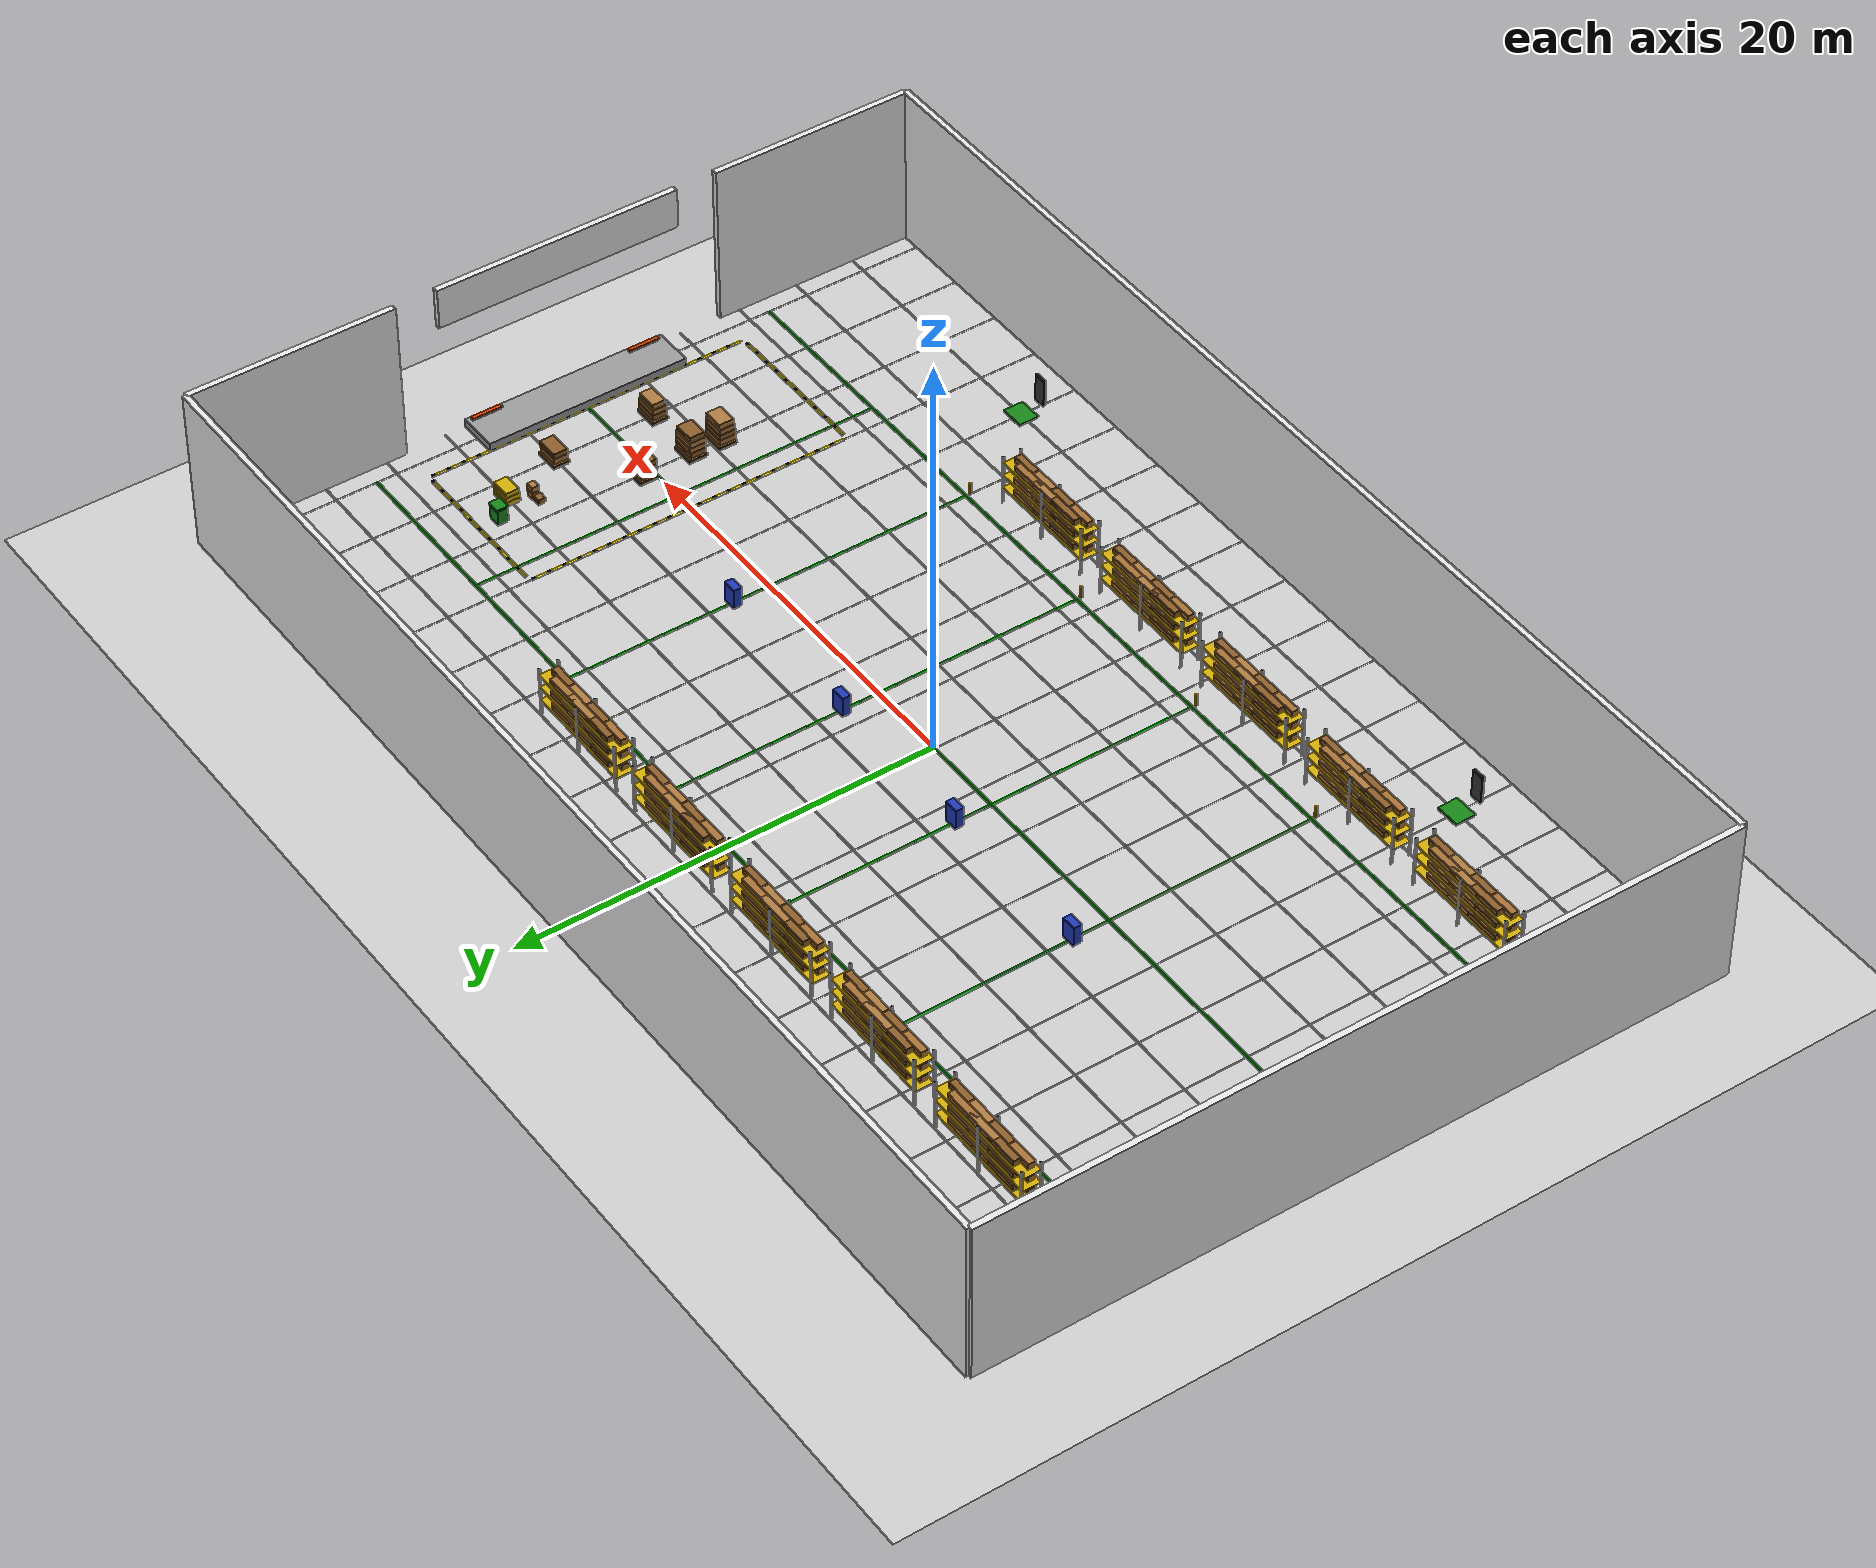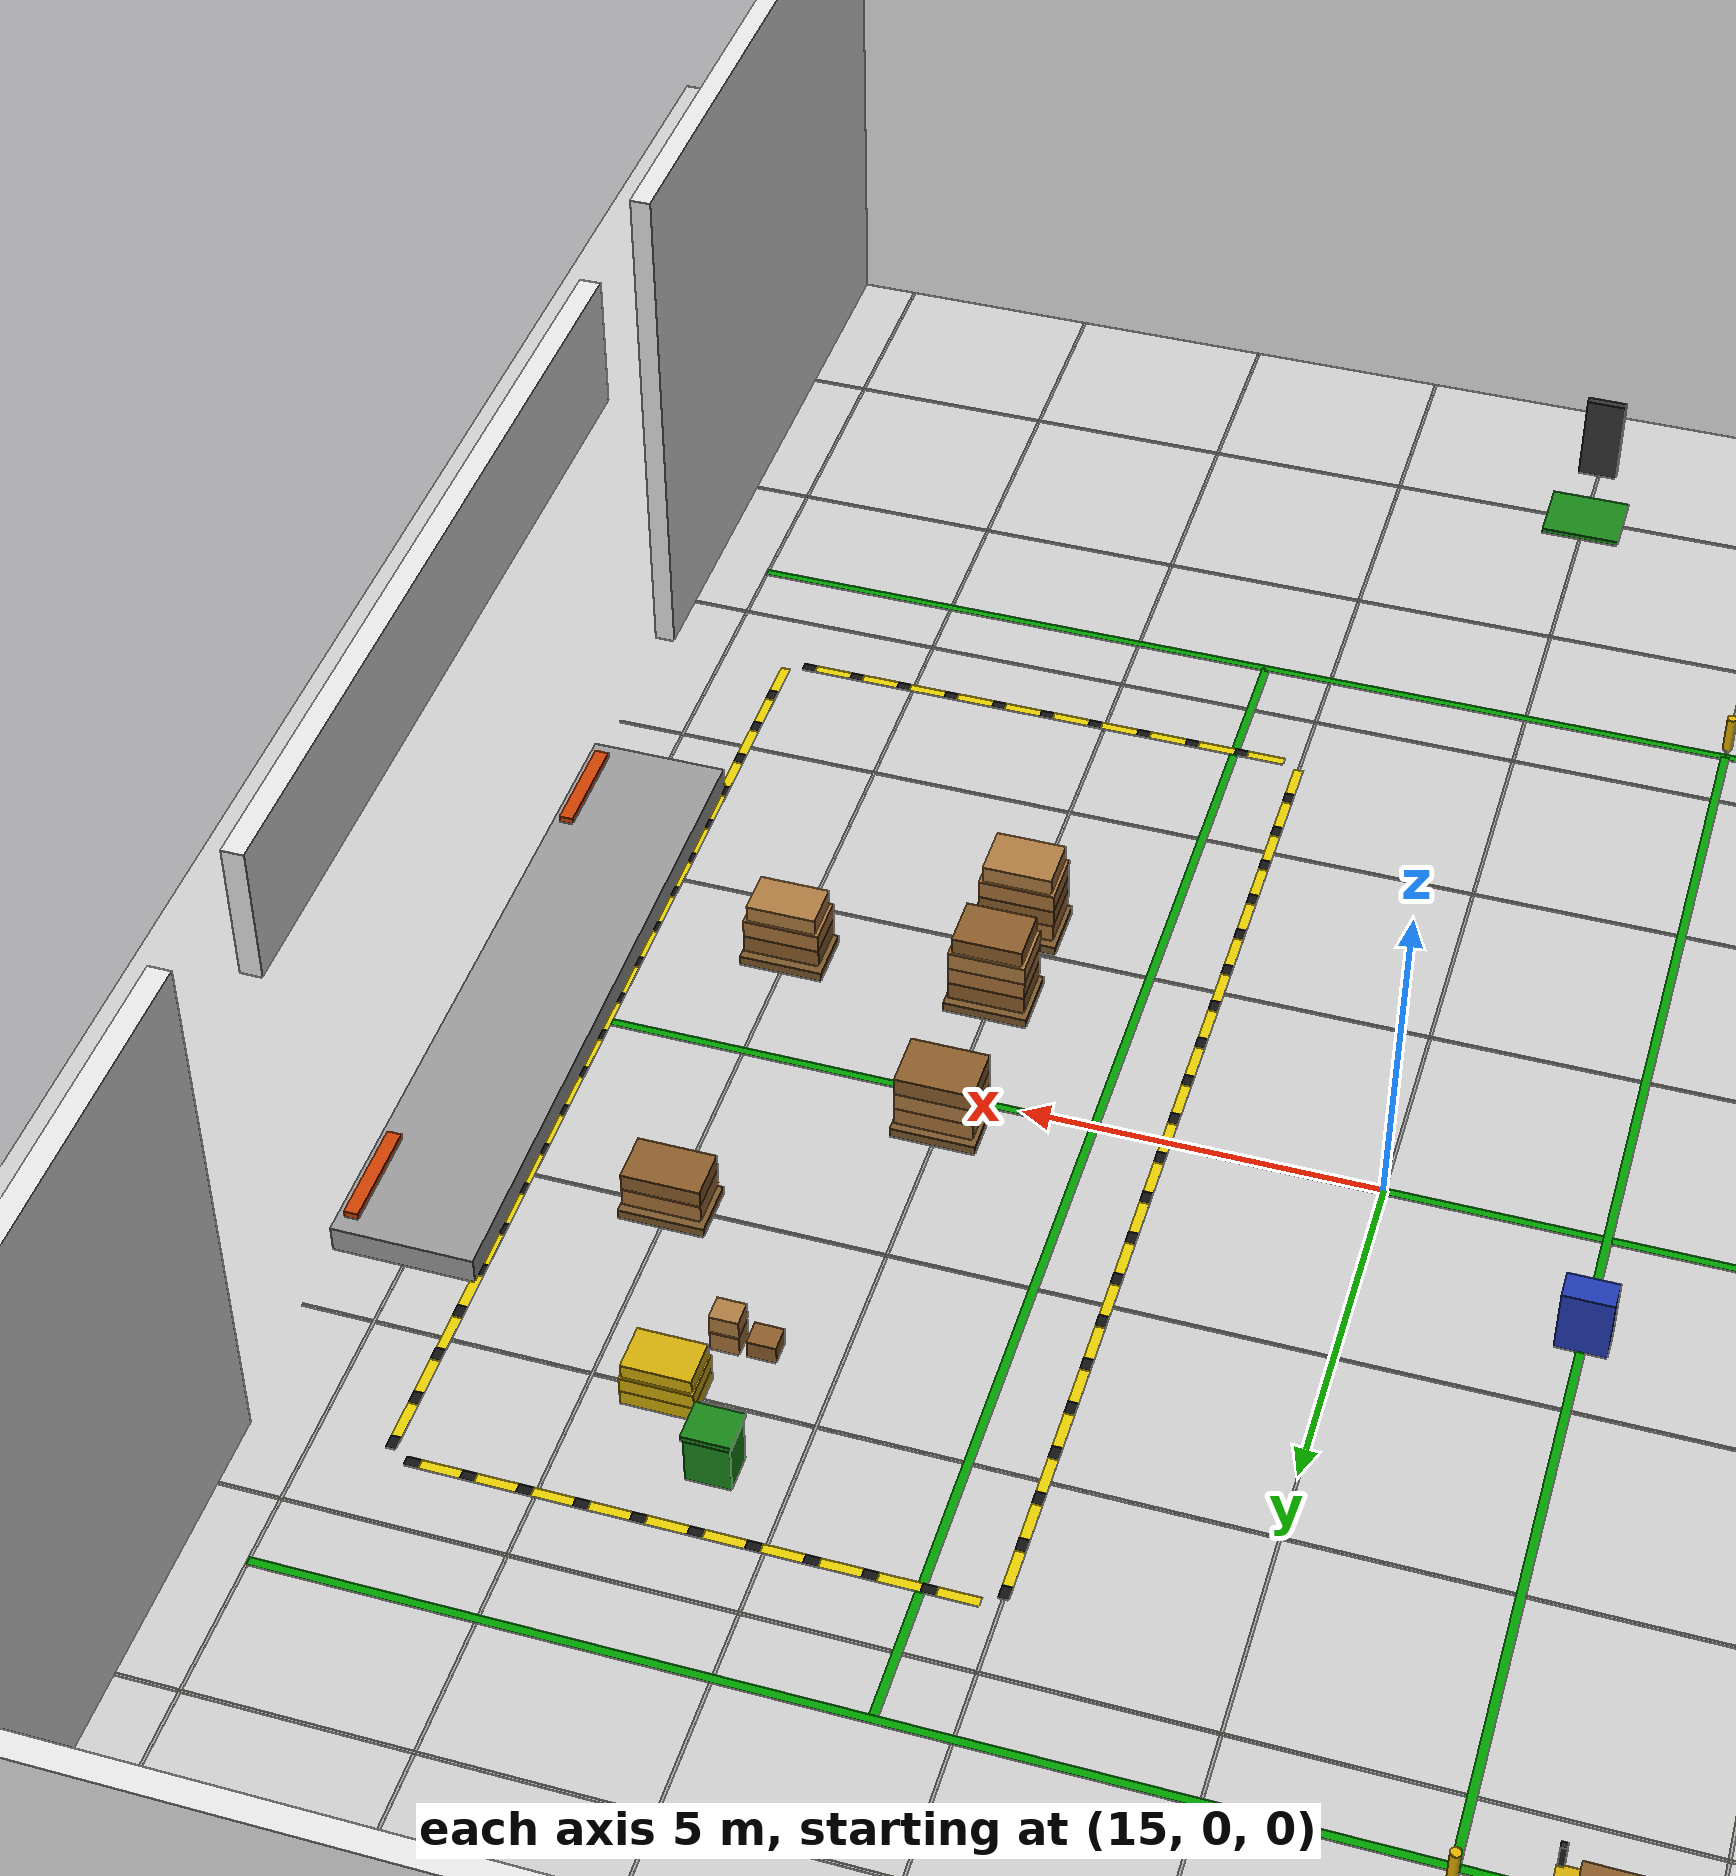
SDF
<?xml version="1.0" ?>
<sdf version="1.6">
  <world name="aws_industrial_warehouse">

    <physics name="default_physics" default="0" type="ode">
      <max_step_size>0.001</max_step_size>
      <real_time_factor>1</real_time_factor>
      <real_time_update_rate>1000</real_time_update_rate>
      <ode>
        <solver><type>quick</type><iters>50</iters><sor>1.3</sor></solver>
        <constraints>
          <cfm>0.0</cfm><erp>0.2</erp>
          <contact_max_correcting_vel>2.0</contact_max_correcting_vel>
          <contact_surface_layer>0.001</contact_surface_layer>
        </constraints>
      </ode>
    </physics>

    <scene>
      <ambient>0.55 0.55 0.55 1</ambient>
      <background>0.75 0.75 0.75 1</background>
      <shadows>1</shadows>
      <grid>false</grid>
    </scene>

    <!-- Side-angle camera matching the reference image -->
    <gui fullscreen="0">
      <camera name="user_camera">
        <pose>-8 -25 12 0 0.55 1.57</pose>
        <view_controller>orbit</view_controller>
        <projection_type>perspective</projection_type>
      </camera>
    </gui>

    <!-- Directional sun with shadows -->
    <light name="sun" type="directional">
      <cast_shadows>1</cast_shadows>
      <pose>0 0 20 0 0 0</pose>
      <diffuse>0.50 0.50 0.50 1</diffuse>
      <specular>0.15 0.15 0.15 1</specular>
      <direction>0.2 0.1 -1</direction>
    </light>
    <light name="lA1" type="point"><pose>-16 -8 7 0 0 0</pose><diffuse>0.90 0.90 0.88 1</diffuse><specular>0.20 0.20 0.20 1</specular><attenuation><range>22</range><linear>0.04</linear><constant>0.1</constant><quadratic>0.003</quadratic></attenuation><cast_shadows>0</cast_shadows></light>
    <light name="lA2" type="point"><pose>-16 0 7 0 0 0</pose><diffuse>0.90 0.90 0.88 1</diffuse><specular>0.20 0.20 0.20 1</specular><attenuation><range>22</range><linear>0.04</linear><constant>0.1</constant><quadratic>0.003</quadratic></attenuation><cast_shadows>0</cast_shadows></light>
    <light name="lA3" type="point"><pose>-16 8 7 0 0 0</pose><diffuse>0.90 0.90 0.88 1</diffuse><specular>0.20 0.20 0.20 1</specular><attenuation><range>22</range><linear>0.04</linear><constant>0.1</constant><quadratic>0.003</quadratic></attenuation><cast_shadows>0</cast_shadows></light>
    <light name="lB1" type="point"><pose>-4 -8 7 0 0 0</pose><diffuse>0.90 0.90 0.88 1</diffuse><specular>0.20 0.20 0.20 1</specular><attenuation><range>22</range><linear>0.04</linear><constant>0.1</constant><quadratic>0.003</quadratic></attenuation><cast_shadows>0</cast_shadows></light>
    <light name="lB2" type="point"><pose>-4 0 7 0 0 0</pose><diffuse>0.90 0.90 0.88 1</diffuse><specular>0.20 0.20 0.20 1</specular><attenuation><range>22</range><linear>0.04</linear><constant>0.1</constant><quadratic>0.003</quadratic></attenuation><cast_shadows>0</cast_shadows></light>
    <light name="lB3" type="point"><pose>-4 8 7 0 0 0</pose><diffuse>0.90 0.90 0.88 1</diffuse><specular>0.20 0.20 0.20 1</specular><attenuation><range>22</range><linear>0.04</linear><constant>0.1</constant><quadratic>0.003</quadratic></attenuation><cast_shadows>0</cast_shadows></light>
    <light name="lC1" type="point"><pose>8 -8 7 0 0 0</pose><diffuse>0.90 0.90 0.88 1</diffuse><specular>0.20 0.20 0.20 1</specular><attenuation><range>22</range><linear>0.04</linear><constant>0.1</constant><quadratic>0.003</quadratic></attenuation><cast_shadows>0</cast_shadows></light>
    <light name="lC2" type="point"><pose>8 0 7 0 0 0</pose><diffuse>0.90 0.90 0.88 1</diffuse><specular>0.20 0.20 0.20 1</specular><attenuation><range>22</range><linear>0.04</linear><constant>0.1</constant><quadratic>0.003</quadratic></attenuation><cast_shadows>0</cast_shadows></light>
    <light name="lC3" type="point"><pose>8 8 7 0 0 0</pose><diffuse>0.90 0.90 0.88 1</diffuse><specular>0.20 0.20 0.20 1</specular><attenuation><range>22</range><linear>0.04</linear><constant>0.1</constant><quadratic>0.003</quadratic></attenuation><cast_shadows>0</cast_shadows></light>
    <light name="lD1" type="point"><pose>20 -8 7 0 0 0</pose><diffuse>0.90 0.90 0.88 1</diffuse><specular>0.20 0.20 0.20 1</specular><attenuation><range>22</range><linear>0.04</linear><constant>0.1</constant><quadratic>0.003</quadratic></attenuation><cast_shadows>0</cast_shadows></light>
    <light name="lD2" type="point"><pose>20 0 7 0 0 0</pose><diffuse>0.90 0.90 0.88 1</diffuse><specular>0.20 0.20 0.20 1</specular><attenuation><range>22</range><linear>0.04</linear><constant>0.1</constant><quadratic>0.003</quadratic></attenuation><cast_shadows>0</cast_shadows></light>
    <light name="lD3" type="point"><pose>20 8 7 0 0 0</pose><diffuse>0.90 0.90 0.88 1</diffuse><specular>0.20 0.20 0.20 1</specular><attenuation><range>22</range><linear>0.04</linear><constant>0.1</constant><quadratic>0.003</quadratic></attenuation><cast_shadows>0</cast_shadows></light>

    <!-- Textured concrete floor (OGRE material via GAZEBO_MODEL_PATH) -->
    <include>
      <uri>model://concrete_floor</uri>
    </include>

    <!-- Exterior walls -->
    <model name="wall_north"><static>true</static><pose>0 18 4 0 0 0</pose><link name="l"><pose>0 0 0 0 0 0</pose><collision name="c"><geometry><box><size>56 0.3 8</size></box></geometry><surface><friction><ode><mu>1.0</mu><mu2>1.0</mu2></ode></friction></surface></collision><visual name="v"><geometry><box><size>56 0.3 8</size></box></geometry><material><ambient>0.85 0.85 0.85 1</ambient><diffuse>0.90 0.90 0.90 1</diffuse></material></visual></link></model>
    <model name="wall_south"><static>true</static><pose>0 -18 4 0 0 0</pose><link name="l"><pose>0 0 0 0 0 0</pose><collision name="c"><geometry><box><size>56 0.3 8</size></box></geometry><surface><friction><ode><mu>1.0</mu><mu2>1.0</mu2></ode></friction></surface></collision><visual name="v"><geometry><box><size>56 0.3 8</size></box></geometry><material><ambient>0.85 0.85 0.85 1</ambient><diffuse>0.90 0.90 0.90 1</diffuse></material></visual></link></model>
    <model name="wall_west"><static>true</static><pose>-28 0 4 0 0 0</pose><link name="l"><pose>0 0 0 0 0 0</pose><collision name="c"><geometry><box><size>0.3 36 8</size></box></geometry><surface><friction><ode><mu>1.0</mu><mu2>1.0</mu2></ode></friction></surface></collision><visual name="v"><geometry><box><size>0.3 36 8</size></box></geometry><material><ambient>0.85 0.85 0.85 1</ambient><diffuse>0.90 0.90 0.90 1</diffuse></material></visual></link></model>
    <model name="wall_east_N"><static>true</static><pose>28 13 4 0 0 0</pose><link name="l"><pose>0 0 0 0 0 0</pose><collision name="c"><geometry><box><size>0.3 10 8</size></box></geometry><surface><friction><ode><mu>1.0</mu><mu2>1.0</mu2></ode></friction></surface></collision><visual name="v"><geometry><box><size>0.3 10 8</size></box></geometry><material><ambient>0.85 0.85 0.85 1</ambient><diffuse>0.90 0.90 0.90 1</diffuse></material></visual></link></model>
    <model name="wall_east_S"><static>true</static><pose>28 -13 4 0 0 0</pose><link name="l"><pose>0 0 0 0 0 0</pose><collision name="c"><geometry><box><size>0.3 10 8</size></box></geometry><surface><friction><ode><mu>1.0</mu><mu2>1.0</mu2></ode></friction></surface></collision><visual name="v"><geometry><box><size>0.3 10 8</size></box></geometry><material><ambient>0.85 0.85 0.85 1</ambient><diffuse>0.90 0.90 0.90 1</diffuse></material></visual></link></model>
    <model name="wall_east_hdr"><static>true</static><pose>28 0 7 0 0 0</pose><link name="l"><pose>0 0 0 0 0 0</pose><collision name="c"><geometry><box><size>0.3 12 2</size></box></geometry><surface><friction><ode><mu>1.0</mu><mu2>1.0</mu2></ode></friction></surface></collision><visual name="v"><geometry><box><size>0.3 12 2</size></box></geometry><material><ambient>0.85 0.85 0.85 1</ambient><diffuse>0.90 0.90 0.90 1</diffuse></material></visual></link></model>

    <!--  PALLET RACKING — North bank  y=+11.5              -->
    <!-- Shelf N1 -->
    <model name="shelf_N1"><static>true</static><pose>-20 11.5 0 0 0 0</pose>
      <link name="pFL"><pose>-2.8 -0.45 1.25 0 0 0</pose><collision name="c"><geometry><box><size>0.08 0.08 2.5</size></box></geometry><surface><friction><ode><mu>1.0</mu><mu2>1.0</mu2></ode></friction></surface></collision><visual name="v"><geometry><box><size>0.08 0.08 2.5</size></box></geometry><material><ambient>0.10 0.10 0.10 1</ambient><diffuse>0.13 0.13 0.13 1</diffuse></material></visual></link>
      <link name="pBL"><pose>-2.8 0.45 1.25 0 0 0</pose><collision name="c"><geometry><box><size>0.08 0.08 2.5</size></box></geometry><surface><friction><ode><mu>1.0</mu><mu2>1.0</mu2></ode></friction></surface></collision><visual name="v"><geometry><box><size>0.08 0.08 2.5</size></box></geometry><material><ambient>0.10 0.10 0.10 1</ambient><diffuse>0.13 0.13 0.13 1</diffuse></material></visual></link>
      <link name="pFC"><pose>0.0 -0.45 1.25 0 0 0</pose><collision name="c"><geometry><box><size>0.08 0.08 2.5</size></box></geometry><surface><friction><ode><mu>1.0</mu><mu2>1.0</mu2></ode></friction></surface></collision><visual name="v"><geometry><box><size>0.08 0.08 2.5</size></box></geometry><material><ambient>0.10 0.10 0.10 1</ambient><diffuse>0.13 0.13 0.13 1</diffuse></material></visual></link>
      <link name="pBC"><pose>0.0 0.45 1.25 0 0 0</pose><collision name="c"><geometry><box><size>0.08 0.08 2.5</size></box></geometry><surface><friction><ode><mu>1.0</mu><mu2>1.0</mu2></ode></friction></surface></collision><visual name="v"><geometry><box><size>0.08 0.08 2.5</size></box></geometry><material><ambient>0.10 0.10 0.10 1</ambient><diffuse>0.13 0.13 0.13 1</diffuse></material></visual></link>
      <link name="pFR"><pose>2.8 -0.45 1.25 0 0 0</pose><collision name="c"><geometry><box><size>0.08 0.08 2.5</size></box></geometry><surface><friction><ode><mu>1.0</mu><mu2>1.0</mu2></ode></friction></surface></collision><visual name="v"><geometry><box><size>0.08 0.08 2.5</size></box></geometry><material><ambient>0.10 0.10 0.10 1</ambient><diffuse>0.13 0.13 0.13 1</diffuse></material></visual></link>
      <link name="pBR"><pose>2.8 0.45 1.25 0 0 0</pose><collision name="c"><geometry><box><size>0.08 0.08 2.5</size></box></geometry><surface><friction><ode><mu>1.0</mu><mu2>1.0</mu2></ode></friction></surface></collision><visual name="v"><geometry><box><size>0.08 0.08 2.5</size></box></geometry><material><ambient>0.10 0.10 0.10 1</ambient><diffuse>0.13 0.13 0.13 1</diffuse></material></visual></link>
      <link name="deck1"><pose>0 0 0.77 0 0 0</pose><collision name="c"><geometry><box><size>5.7 0.88 0.05</size></box></geometry><surface><friction><ode><mu>1.0</mu><mu2>1.0</mu2></ode></friction></surface></collision><visual name="v"><geometry><box><size>5.7 0.88 0.05</size></box></geometry><material><ambient>0.70 0.55 0.02 1</ambient><diffuse>0.82 0.67 0.03 1</diffuse></material></visual></link>
      <link name="deck2"><pose>0 0 1.45 0 0 0</pose><collision name="c"><geometry><box><size>5.7 0.88 0.05</size></box></geometry><surface><friction><ode><mu>1.0</mu><mu2>1.0</mu2></ode></friction></surface></collision><visual name="v"><geometry><box><size>5.7 0.88 0.05</size></box></geometry><material><ambient>0.70 0.55 0.02 1</ambient><diffuse>0.82 0.67 0.03 1</diffuse></material></visual></link>
      <link name="deck3"><pose>0 0 2.12 0 0 0</pose><collision name="c"><geometry><box><size>5.7 0.88 0.05</size></box></geometry><surface><friction><ode><mu>1.0</mu><mu2>1.0</mu2></ode></friction></surface></collision><visual name="v"><geometry><box><size>5.7 0.88 0.05</size></box></geometry><material><ambient>0.70 0.55 0.02 1</ambient><diffuse>0.82 0.67 0.03 1</diffuse></material></visual></link>
      <link name="bF1_1"><pose>-1.95 -0.18 0.94 0 0 0</pose><visual name="v"><geometry><box><size>1.26 0.36 0.28</size></box></geometry><material><ambient>0.58 0.38 0.18 1</ambient><diffuse>0.65 0.44 0.21 1</diffuse></material></visual></link>
      <link name="lF1_1"><pose>-1.95 -0.363 0.97 0 0 0</pose><visual name="v"><geometry><box><size>0.62 0.005 0.13</size></box></geometry><material><ambient>0.76 0.76 0.74 1</ambient><diffuse>0.83 0.83 0.81 1</diffuse></material></visual></link>
      <link name="bF1_2"><pose>-0.65 -0.18 0.94 0 0 0</pose><visual name="v"><geometry><box><size>1.26 0.36 0.28</size></box></geometry><material><ambient>0.48 0.30 0.12 1</ambient><diffuse>0.54 0.36 0.16 1</diffuse></material></visual></link>
      <link name="lF1_2"><pose>-0.65 -0.363 0.97 0 0 0</pose><visual name="v"><geometry><box><size>0.62 0.005 0.13</size></box></geometry><material><ambient>0.76 0.76 0.74 1</ambient><diffuse>0.83 0.83 0.81 1</diffuse></material></visual></link>
      <link name="bF1_3"><pose>0.65 -0.18 0.94 0 0 0</pose><visual name="v"><geometry><box><size>1.26 0.36 0.28</size></box></geometry><material><ambient>0.62 0.43 0.22 1</ambient><diffuse>0.68 0.48 0.25 1</diffuse></material></visual></link>
      <link name="lF1_3"><pose>0.65 -0.363 0.97 0 0 0</pose><visual name="v"><geometry><box><size>0.62 0.005 0.13</size></box></geometry><material><ambient>0.76 0.76 0.74 1</ambient><diffuse>0.83 0.83 0.81 1</diffuse></material></visual></link>
      <link name="bF1_4"><pose>1.95 -0.18 0.94 0 0 0</pose><visual name="v"><geometry><box><size>1.26 0.36 0.28</size></box></geometry><material><ambient>0.48 0.30 0.12 1</ambient><diffuse>0.54 0.36 0.16 1</diffuse></material></visual></link>
      <link name="lF1_4"><pose>1.95 -0.363 0.97 0 0 0</pose><visual name="v"><geometry><box><size>0.62 0.005 0.13</size></box></geometry><material><ambient>0.76 0.76 0.74 1</ambient><diffuse>0.83 0.83 0.81 1</diffuse></material></visual></link>
      <link name="bB1_1"><pose>-1.3 0.18 0.94 0 0 0</pose><visual name="v"><geometry><box><size>1.65 0.36 0.3</size></box></geometry><material><ambient>0.48 0.30 0.12 1</ambient><diffuse>0.54 0.36 0.16 1</diffuse></material></visual></link>
      <link name="bB1_2"><pose>0.0 0.18 0.94 0 0 0</pose><visual name="v"><geometry><box><size>1.65 0.36 0.3</size></box></geometry><material><ambient>0.62 0.43 0.22 1</ambient><diffuse>0.68 0.48 0.25 1</diffuse></material></visual></link>
      <link name="bB1_3"><pose>1.3 0.18 0.94 0 0 0</pose><visual name="v"><geometry><box><size>1.65 0.36 0.3</size></box></geometry><material><ambient>0.58 0.38 0.18 1</ambient><diffuse>0.65 0.44 0.21 1</diffuse></material></visual></link>
      <link name="bF2_1"><pose>-1.95 -0.18 1.62 0 0 0</pose><visual name="v"><geometry><box><size>1.26 0.36 0.32</size></box></geometry><material><ambient>0.58 0.38 0.18 1</ambient><diffuse>0.65 0.44 0.21 1</diffuse></material></visual></link>
      <link name="lF2_1"><pose>-1.95 -0.363 1.6500000000000001 0 0 0</pose><visual name="v"><geometry><box><size>0.62 0.005 0.13</size></box></geometry><material><ambient>0.76 0.76 0.74 1</ambient><diffuse>0.83 0.83 0.81 1</diffuse></material></visual></link>
      <link name="bF2_2"><pose>-0.65 -0.18 1.62 0 0 0</pose><visual name="v"><geometry><box><size>1.26 0.36 0.32</size></box></geometry><material><ambient>0.48 0.30 0.12 1</ambient><diffuse>0.54 0.36 0.16 1</diffuse></material></visual></link>
      <link name="lF2_2"><pose>-0.65 -0.363 1.6500000000000001 0 0 0</pose><visual name="v"><geometry><box><size>0.62 0.005 0.13</size></box></geometry><material><ambient>0.76 0.76 0.74 1</ambient><diffuse>0.83 0.83 0.81 1</diffuse></material></visual></link>
      <link name="bF2_3"><pose>0.65 -0.18 1.62 0 0 0</pose><visual name="v"><geometry><box><size>1.26 0.36 0.32</size></box></geometry><material><ambient>0.62 0.43 0.22 1</ambient><diffuse>0.68 0.48 0.25 1</diffuse></material></visual></link>
      <link name="lF2_3"><pose>0.65 -0.363 1.6500000000000001 0 0 0</pose><visual name="v"><geometry><box><size>0.62 0.005 0.13</size></box></geometry><material><ambient>0.76 0.76 0.74 1</ambient><diffuse>0.83 0.83 0.81 1</diffuse></material></visual></link>
      <link name="bF2_4"><pose>1.95 -0.18 1.62 0 0 0</pose><visual name="v"><geometry><box><size>1.26 0.36 0.32</size></box></geometry><material><ambient>0.48 0.30 0.12 1</ambient><diffuse>0.54 0.36 0.16 1</diffuse></material></visual></link>
      <link name="lF2_4"><pose>1.95 -0.363 1.6500000000000001 0 0 0</pose><visual name="v"><geometry><box><size>0.62 0.005 0.13</size></box></geometry><material><ambient>0.76 0.76 0.74 1</ambient><diffuse>0.83 0.83 0.81 1</diffuse></material></visual></link>
      <link name="bB2_1"><pose>-1.3 0.18 1.62 0 0 0</pose><visual name="v"><geometry><box><size>1.65 0.36 0.28</size></box></geometry><material><ambient>0.48 0.30 0.12 1</ambient><diffuse>0.54 0.36 0.16 1</diffuse></material></visual></link>
      <link name="bB2_2"><pose>0.0 0.18 1.62 0 0 0</pose><visual name="v"><geometry><box><size>1.65 0.36 0.28</size></box></geometry><material><ambient>0.62 0.43 0.22 1</ambient><diffuse>0.68 0.48 0.25 1</diffuse></material></visual></link>
      <link name="bB2_3"><pose>1.3 0.18 1.62 0 0 0</pose><visual name="v"><geometry><box><size>1.65 0.36 0.28</size></box></geometry><material><ambient>0.58 0.38 0.18 1</ambient><diffuse>0.65 0.44 0.21 1</diffuse></material></visual></link>
      <link name="bF3_1"><pose>-1.95 -0.18 2.29 0 0 0</pose><visual name="v"><geometry><box><size>1.26 0.36 0.28</size></box></geometry><material><ambient>0.58 0.38 0.18 1</ambient><diffuse>0.65 0.44 0.21 1</diffuse></material></visual></link>
      <link name="lF3_1"><pose>-1.95 -0.363 2.32 0 0 0</pose><visual name="v"><geometry><box><size>0.62 0.005 0.13</size></box></geometry><material><ambient>0.76 0.76 0.74 1</ambient><diffuse>0.83 0.83 0.81 1</diffuse></material></visual></link>
      <link name="bF3_2"><pose>-0.65 -0.18 2.29 0 0 0</pose><visual name="v"><geometry><box><size>1.26 0.36 0.28</size></box></geometry><material><ambient>0.48 0.30 0.12 1</ambient><diffuse>0.54 0.36 0.16 1</diffuse></material></visual></link>
      <link name="lF3_2"><pose>-0.65 -0.363 2.32 0 0 0</pose><visual name="v"><geometry><box><size>0.62 0.005 0.13</size></box></geometry><material><ambient>0.76 0.76 0.74 1</ambient><diffuse>0.83 0.83 0.81 1</diffuse></material></visual></link>
      <link name="bF3_3"><pose>0.65 -0.18 2.29 0 0 0</pose><visual name="v"><geometry><box><size>1.26 0.36 0.28</size></box></geometry><material><ambient>0.62 0.43 0.22 1</ambient><diffuse>0.68 0.48 0.25 1</diffuse></material></visual></link>
      <link name="lF3_3"><pose>0.65 -0.363 2.32 0 0 0</pose><visual name="v"><geometry><box><size>0.62 0.005 0.13</size></box></geometry><material><ambient>0.76 0.76 0.74 1</ambient><diffuse>0.83 0.83 0.81 1</diffuse></material></visual></link>
      <link name="bF3_4"><pose>1.95 -0.18 2.29 0 0 0</pose><visual name="v"><geometry><box><size>1.26 0.36 0.28</size></box></geometry><material><ambient>0.48 0.30 0.12 1</ambient><diffuse>0.54 0.36 0.16 1</diffuse></material></visual></link>
      <link name="lF3_4"><pose>1.95 -0.363 2.32 0 0 0</pose><visual name="v"><geometry><box><size>0.62 0.005 0.13</size></box></geometry><material><ambient>0.76 0.76 0.74 1</ambient><diffuse>0.83 0.83 0.81 1</diffuse></material></visual></link>
      <link name="bB3_1"><pose>-1.3 0.18 2.29 0 0 0</pose><visual name="v"><geometry><box><size>1.65 0.36 0.28</size></box></geometry><material><ambient>0.48 0.30 0.12 1</ambient><diffuse>0.54 0.36 0.16 1</diffuse></material></visual></link>
      <link name="bB3_2"><pose>0.0 0.18 2.29 0 0 0</pose><visual name="v"><geometry><box><size>1.65 0.36 0.28</size></box></geometry><material><ambient>0.62 0.43 0.22 1</ambient><diffuse>0.68 0.48 0.25 1</diffuse></material></visual></link>
      <link name="bB3_3"><pose>1.3 0.18 2.29 0 0 0</pose><visual name="v"><geometry><box><size>1.65 0.36 0.28</size></box></geometry><material><ambient>0.58 0.38 0.18 1</ambient><diffuse>0.65 0.44 0.21 1</diffuse></material></visual></link>
      </model>
    <!-- Shelf N2 -->
    <model name="shelf_N2"><static>true</static><pose>-13 11.5 0 0 0 0</pose>
      <link name="pFL"><pose>-2.8 -0.45 1.25 0 0 0</pose><collision name="c"><geometry><box><size>0.08 0.08 2.5</size></box></geometry><surface><friction><ode><mu>1.0</mu><mu2>1.0</mu2></ode></friction></surface></collision><visual name="v"><geometry><box><size>0.08 0.08 2.5</size></box></geometry><material><ambient>0.10 0.10 0.10 1</ambient><diffuse>0.13 0.13 0.13 1</diffuse></material></visual></link>
      <link name="pBL"><pose>-2.8 0.45 1.25 0 0 0</pose><collision name="c"><geometry><box><size>0.08 0.08 2.5</size></box></geometry><surface><friction><ode><mu>1.0</mu><mu2>1.0</mu2></ode></friction></surface></collision><visual name="v"><geometry><box><size>0.08 0.08 2.5</size></box></geometry><material><ambient>0.10 0.10 0.10 1</ambient><diffuse>0.13 0.13 0.13 1</diffuse></material></visual></link>
      <link name="pFC"><pose>0.0 -0.45 1.25 0 0 0</pose><collision name="c"><geometry><box><size>0.08 0.08 2.5</size></box></geometry><surface><friction><ode><mu>1.0</mu><mu2>1.0</mu2></ode></friction></surface></collision><visual name="v"><geometry><box><size>0.08 0.08 2.5</size></box></geometry><material><ambient>0.10 0.10 0.10 1</ambient><diffuse>0.13 0.13 0.13 1</diffuse></material></visual></link>
      <link name="pBC"><pose>0.0 0.45 1.25 0 0 0</pose><collision name="c"><geometry><box><size>0.08 0.08 2.5</size></box></geometry><surface><friction><ode><mu>1.0</mu><mu2>1.0</mu2></ode></friction></surface></collision><visual name="v"><geometry><box><size>0.08 0.08 2.5</size></box></geometry><material><ambient>0.10 0.10 0.10 1</ambient><diffuse>0.13 0.13 0.13 1</diffuse></material></visual></link>
      <link name="pFR"><pose>2.8 -0.45 1.25 0 0 0</pose><collision name="c"><geometry><box><size>0.08 0.08 2.5</size></box></geometry><surface><friction><ode><mu>1.0</mu><mu2>1.0</mu2></ode></friction></surface></collision><visual name="v"><geometry><box><size>0.08 0.08 2.5</size></box></geometry><material><ambient>0.10 0.10 0.10 1</ambient><diffuse>0.13 0.13 0.13 1</diffuse></material></visual></link>
      <link name="pBR"><pose>2.8 0.45 1.25 0 0 0</pose><collision name="c"><geometry><box><size>0.08 0.08 2.5</size></box></geometry><surface><friction><ode><mu>1.0</mu><mu2>1.0</mu2></ode></friction></surface></collision><visual name="v"><geometry><box><size>0.08 0.08 2.5</size></box></geometry><material><ambient>0.10 0.10 0.10 1</ambient><diffuse>0.13 0.13 0.13 1</diffuse></material></visual></link>
      <link name="deck1"><pose>0 0 0.77 0 0 0</pose><collision name="c"><geometry><box><size>5.7 0.88 0.05</size></box></geometry><surface><friction><ode><mu>1.0</mu><mu2>1.0</mu2></ode></friction></surface></collision><visual name="v"><geometry><box><size>5.7 0.88 0.05</size></box></geometry><material><ambient>0.70 0.55 0.02 1</ambient><diffuse>0.82 0.67 0.03 1</diffuse></material></visual></link>
      <link name="deck2"><pose>0 0 1.45 0 0 0</pose><collision name="c"><geometry><box><size>5.7 0.88 0.05</size></box></geometry><surface><friction><ode><mu>1.0</mu><mu2>1.0</mu2></ode></friction></surface></collision><visual name="v"><geometry><box><size>5.7 0.88 0.05</size></box></geometry><material><ambient>0.70 0.55 0.02 1</ambient><diffuse>0.82 0.67 0.03 1</diffuse></material></visual></link>
      <link name="deck3"><pose>0 0 2.12 0 0 0</pose><collision name="c"><geometry><box><size>5.7 0.88 0.05</size></box></geometry><surface><friction><ode><mu>1.0</mu><mu2>1.0</mu2></ode></friction></surface></collision><visual name="v"><geometry><box><size>5.7 0.88 0.05</size></box></geometry><material><ambient>0.70 0.55 0.02 1</ambient><diffuse>0.82 0.67 0.03 1</diffuse></material></visual></link>
      <link name="bF1_1"><pose>-1.95 -0.18 0.94 0 0 0</pose><visual name="v"><geometry><box><size>1.26 0.36 0.28</size></box></geometry><material><ambient>0.58 0.38 0.18 1</ambient><diffuse>0.65 0.44 0.21 1</diffuse></material></visual></link>
      <link name="lF1_1"><pose>-1.95 -0.363 0.97 0 0 0</pose><visual name="v"><geometry><box><size>0.62 0.005 0.13</size></box></geometry><material><ambient>0.76 0.76 0.74 1</ambient><diffuse>0.83 0.83 0.81 1</diffuse></material></visual></link>
      <link name="bF1_2"><pose>-0.65 -0.18 0.94 0 0 0</pose><visual name="v"><geometry><box><size>1.26 0.36 0.28</size></box></geometry><material><ambient>0.48 0.30 0.12 1</ambient><diffuse>0.54 0.36 0.16 1</diffuse></material></visual></link>
      <link name="lF1_2"><pose>-0.65 -0.363 0.97 0 0 0</pose><visual name="v"><geometry><box><size>0.62 0.005 0.13</size></box></geometry><material><ambient>0.76 0.76 0.74 1</ambient><diffuse>0.83 0.83 0.81 1</diffuse></material></visual></link>
      <link name="bF1_3"><pose>0.65 -0.18 0.94 0 0 0</pose><visual name="v"><geometry><box><size>1.26 0.36 0.28</size></box></geometry><material><ambient>0.62 0.43 0.22 1</ambient><diffuse>0.68 0.48 0.25 1</diffuse></material></visual></link>
      <link name="lF1_3"><pose>0.65 -0.363 0.97 0 0 0</pose><visual name="v"><geometry><box><size>0.62 0.005 0.13</size></box></geometry><material><ambient>0.76 0.76 0.74 1</ambient><diffuse>0.83 0.83 0.81 1</diffuse></material></visual></link>
      <link name="bF1_4"><pose>1.95 -0.18 0.94 0 0 0</pose><visual name="v"><geometry><box><size>1.26 0.36 0.28</size></box></geometry><material><ambient>0.48 0.30 0.12 1</ambient><diffuse>0.54 0.36 0.16 1</diffuse></material></visual></link>
      <link name="lF1_4"><pose>1.95 -0.363 0.97 0 0 0</pose><visual name="v"><geometry><box><size>0.62 0.005 0.13</size></box></geometry><material><ambient>0.76 0.76 0.74 1</ambient><diffuse>0.83 0.83 0.81 1</diffuse></material></visual></link>
      <link name="bB1_1"><pose>-1.3 0.18 0.94 0 0 0</pose><visual name="v"><geometry><box><size>1.65 0.36 0.3</size></box></geometry><material><ambient>0.48 0.30 0.12 1</ambient><diffuse>0.54 0.36 0.16 1</diffuse></material></visual></link>
      <link name="bB1_2"><pose>0.0 0.18 0.94 0 0 0</pose><visual name="v"><geometry><box><size>1.65 0.36 0.3</size></box></geometry><material><ambient>0.62 0.43 0.22 1</ambient><diffuse>0.68 0.48 0.25 1</diffuse></material></visual></link>
      <link name="bB1_3"><pose>1.3 0.18 0.94 0 0 0</pose><visual name="v"><geometry><box><size>1.65 0.36 0.3</size></box></geometry><material><ambient>0.58 0.38 0.18 1</ambient><diffuse>0.65 0.44 0.21 1</diffuse></material></visual></link>
      <link name="bF2_1"><pose>-1.95 -0.18 1.62 0 0 0</pose><visual name="v"><geometry><box><size>1.26 0.36 0.32</size></box></geometry><material><ambient>0.58 0.38 0.18 1</ambient><diffuse>0.65 0.44 0.21 1</diffuse></material></visual></link>
      <link name="lF2_1"><pose>-1.95 -0.363 1.6500000000000001 0 0 0</pose><visual name="v"><geometry><box><size>0.62 0.005 0.13</size></box></geometry><material><ambient>0.76 0.76 0.74 1</ambient><diffuse>0.83 0.83 0.81 1</diffuse></material></visual></link>
      <link name="bF2_2"><pose>-0.65 -0.18 1.62 0 0 0</pose><visual name="v"><geometry><box><size>1.26 0.36 0.32</size></box></geometry><material><ambient>0.48 0.30 0.12 1</ambient><diffuse>0.54 0.36 0.16 1</diffuse></material></visual></link>
      <link name="lF2_2"><pose>-0.65 -0.363 1.6500000000000001 0 0 0</pose><visual name="v"><geometry><box><size>0.62 0.005 0.13</size></box></geometry><material><ambient>0.76 0.76 0.74 1</ambient><diffuse>0.83 0.83 0.81 1</diffuse></material></visual></link>
      <link name="bF2_3"><pose>0.65 -0.18 1.62 0 0 0</pose><visual name="v"><geometry><box><size>1.26 0.36 0.32</size></box></geometry><material><ambient>0.62 0.43 0.22 1</ambient><diffuse>0.68 0.48 0.25 1</diffuse></material></visual></link>
      <link name="lF2_3"><pose>0.65 -0.363 1.6500000000000001 0 0 0</pose><visual name="v"><geometry><box><size>0.62 0.005 0.13</size></box></geometry><material><ambient>0.76 0.76 0.74 1</ambient><diffuse>0.83 0.83 0.81 1</diffuse></material></visual></link>
      <link name="bF2_4"><pose>1.95 -0.18 1.62 0 0 0</pose><visual name="v"><geometry><box><size>1.26 0.36 0.32</size></box></geometry><material><ambient>0.48 0.30 0.12 1</ambient><diffuse>0.54 0.36 0.16 1</diffuse></material></visual></link>
      <link name="lF2_4"><pose>1.95 -0.363 1.6500000000000001 0 0 0</pose><visual name="v"><geometry><box><size>0.62 0.005 0.13</size></box></geometry><material><ambient>0.76 0.76 0.74 1</ambient><diffuse>0.83 0.83 0.81 1</diffuse></material></visual></link>
      <link name="bB2_1"><pose>-1.3 0.18 1.62 0 0 0</pose><visual name="v"><geometry><box><size>1.65 0.36 0.28</size></box></geometry><material><ambient>0.48 0.30 0.12 1</ambient><diffuse>0.54 0.36 0.16 1</diffuse></material></visual></link>
      <link name="bB2_2"><pose>0.0 0.18 1.62 0 0 0</pose><visual name="v"><geometry><box><size>1.65 0.36 0.28</size></box></geometry><material><ambient>0.62 0.43 0.22 1</ambient><diffuse>0.68 0.48 0.25 1</diffuse></material></visual></link>
      <link name="bB2_3"><pose>1.3 0.18 1.62 0 0 0</pose><visual name="v"><geometry><box><size>1.65 0.36 0.28</size></box></geometry><material><ambient>0.58 0.38 0.18 1</ambient><diffuse>0.65 0.44 0.21 1</diffuse></material></visual></link>
      <link name="bF3_1"><pose>-1.95 -0.18 2.29 0 0 0</pose><visual name="v"><geometry><box><size>1.26 0.36 0.28</size></box></geometry><material><ambient>0.58 0.38 0.18 1</ambient><diffuse>0.65 0.44 0.21 1</diffuse></material></visual></link>
      <link name="lF3_1"><pose>-1.95 -0.363 2.32 0 0 0</pose><visual name="v"><geometry><box><size>0.62 0.005 0.13</size></box></geometry><material><ambient>0.76 0.76 0.74 1</ambient><diffuse>0.83 0.83 0.81 1</diffuse></material></visual></link>
      <link name="bF3_2"><pose>-0.65 -0.18 2.29 0 0 0</pose><visual name="v"><geometry><box><size>1.26 0.36 0.28</size></box></geometry><material><ambient>0.48 0.30 0.12 1</ambient><diffuse>0.54 0.36 0.16 1</diffuse></material></visual></link>
      <link name="lF3_2"><pose>-0.65 -0.363 2.32 0 0 0</pose><visual name="v"><geometry><box><size>0.62 0.005 0.13</size></box></geometry><material><ambient>0.76 0.76 0.74 1</ambient><diffuse>0.83 0.83 0.81 1</diffuse></material></visual></link>
      <link name="bF3_3"><pose>0.65 -0.18 2.29 0 0 0</pose><visual name="v"><geometry><box><size>1.26 0.36 0.28</size></box></geometry><material><ambient>0.62 0.43 0.22 1</ambient><diffuse>0.68 0.48 0.25 1</diffuse></material></visual></link>
      <link name="lF3_3"><pose>0.65 -0.363 2.32 0 0 0</pose><visual name="v"><geometry><box><size>0.62 0.005 0.13</size></box></geometry><material><ambient>0.76 0.76 0.74 1</ambient><diffuse>0.83 0.83 0.81 1</diffuse></material></visual></link>
      <link name="bF3_4"><pose>1.95 -0.18 2.29 0 0 0</pose><visual name="v"><geometry><box><size>1.26 0.36 0.28</size></box></geometry><material><ambient>0.48 0.30 0.12 1</ambient><diffuse>0.54 0.36 0.16 1</diffuse></material></visual></link>
      <link name="lF3_4"><pose>1.95 -0.363 2.32 0 0 0</pose><visual name="v"><geometry><box><size>0.62 0.005 0.13</size></box></geometry><material><ambient>0.76 0.76 0.74 1</ambient><diffuse>0.83 0.83 0.81 1</diffuse></material></visual></link>
      <link name="bB3_1"><pose>-1.3 0.18 2.29 0 0 0</pose><visual name="v"><geometry><box><size>1.65 0.36 0.28</size></box></geometry><material><ambient>0.48 0.30 0.12 1</ambient><diffuse>0.54 0.36 0.16 1</diffuse></material></visual></link>
      <link name="bB3_2"><pose>0.0 0.18 2.29 0 0 0</pose><visual name="v"><geometry><box><size>1.65 0.36 0.28</size></box></geometry><material><ambient>0.62 0.43 0.22 1</ambient><diffuse>0.68 0.48 0.25 1</diffuse></material></visual></link>
      <link name="bB3_3"><pose>1.3 0.18 2.29 0 0 0</pose><visual name="v"><geometry><box><size>1.65 0.36 0.28</size></box></geometry><material><ambient>0.58 0.38 0.18 1</ambient><diffuse>0.65 0.44 0.21 1</diffuse></material></visual></link>
      </model>
    <!-- Shelf N3 -->
    <model name="shelf_N3"><static>true</static><pose>-6 11.5 0 0 0 0</pose>
      <link name="pFL"><pose>-2.8 -0.45 1.25 0 0 0</pose><collision name="c"><geometry><box><size>0.08 0.08 2.5</size></box></geometry><surface><friction><ode><mu>1.0</mu><mu2>1.0</mu2></ode></friction></surface></collision><visual name="v"><geometry><box><size>0.08 0.08 2.5</size></box></geometry><material><ambient>0.10 0.10 0.10 1</ambient><diffuse>0.13 0.13 0.13 1</diffuse></material></visual></link>
      <link name="pBL"><pose>-2.8 0.45 1.25 0 0 0</pose><collision name="c"><geometry><box><size>0.08 0.08 2.5</size></box></geometry><surface><friction><ode><mu>1.0</mu><mu2>1.0</mu2></ode></friction></surface></collision><visual name="v"><geometry><box><size>0.08 0.08 2.5</size></box></geometry><material><ambient>0.10 0.10 0.10 1</ambient><diffuse>0.13 0.13 0.13 1</diffuse></material></visual></link>
      <link name="pFC"><pose>0.0 -0.45 1.25 0 0 0</pose><collision name="c"><geometry><box><size>0.08 0.08 2.5</size></box></geometry><surface><friction><ode><mu>1.0</mu><mu2>1.0</mu2></ode></friction></surface></collision><visual name="v"><geometry><box><size>0.08 0.08 2.5</size></box></geometry><material><ambient>0.10 0.10 0.10 1</ambient><diffuse>0.13 0.13 0.13 1</diffuse></material></visual></link>
      <link name="pBC"><pose>0.0 0.45 1.25 0 0 0</pose><collision name="c"><geometry><box><size>0.08 0.08 2.5</size></box></geometry><surface><friction><ode><mu>1.0</mu><mu2>1.0</mu2></ode></friction></surface></collision><visual name="v"><geometry><box><size>0.08 0.08 2.5</size></box></geometry><material><ambient>0.10 0.10 0.10 1</ambient><diffuse>0.13 0.13 0.13 1</diffuse></material></visual></link>
      <link name="pFR"><pose>2.8 -0.45 1.25 0 0 0</pose><collision name="c"><geometry><box><size>0.08 0.08 2.5</size></box></geometry><surface><friction><ode><mu>1.0</mu><mu2>1.0</mu2></ode></friction></surface></collision><visual name="v"><geometry><box><size>0.08 0.08 2.5</size></box></geometry><material><ambient>0.10 0.10 0.10 1</ambient><diffuse>0.13 0.13 0.13 1</diffuse></material></visual></link>
      <link name="pBR"><pose>2.8 0.45 1.25 0 0 0</pose><collision name="c"><geometry><box><size>0.08 0.08 2.5</size></box></geometry><surface><friction><ode><mu>1.0</mu><mu2>1.0</mu2></ode></friction></surface></collision><visual name="v"><geometry><box><size>0.08 0.08 2.5</size></box></geometry><material><ambient>0.10 0.10 0.10 1</ambient><diffuse>0.13 0.13 0.13 1</diffuse></material></visual></link>
      <link name="deck1"><pose>0 0 0.77 0 0 0</pose><collision name="c"><geometry><box><size>5.7 0.88 0.05</size></box></geometry><surface><friction><ode><mu>1.0</mu><mu2>1.0</mu2></ode></friction></surface></collision><visual name="v"><geometry><box><size>5.7 0.88 0.05</size></box></geometry><material><ambient>0.70 0.55 0.02 1</ambient><diffuse>0.82 0.67 0.03 1</diffuse></material></visual></link>
      <link name="deck2"><pose>0 0 1.45 0 0 0</pose><collision name="c"><geometry><box><size>5.7 0.88 0.05</size></box></geometry><surface><friction><ode><mu>1.0</mu><mu2>1.0</mu2></ode></friction></surface></collision><visual name="v"><geometry><box><size>5.7 0.88 0.05</size></box></geometry><material><ambient>0.70 0.55 0.02 1</ambient><diffuse>0.82 0.67 0.03 1</diffuse></material></visual></link>
      <link name="deck3"><pose>0 0 2.12 0 0 0</pose><collision name="c"><geometry><box><size>5.7 0.88 0.05</size></box></geometry><surface><friction><ode><mu>1.0</mu><mu2>1.0</mu2></ode></friction></surface></collision><visual name="v"><geometry><box><size>5.7 0.88 0.05</size></box></geometry><material><ambient>0.70 0.55 0.02 1</ambient><diffuse>0.82 0.67 0.03 1</diffuse></material></visual></link>
      <link name="bF1_1"><pose>-1.95 -0.18 0.94 0 0 0</pose><visual name="v"><geometry><box><size>1.26 0.36 0.28</size></box></geometry><material><ambient>0.58 0.38 0.18 1</ambient><diffuse>0.65 0.44 0.21 1</diffuse></material></visual></link>
      <link name="lF1_1"><pose>-1.95 -0.363 0.97 0 0 0</pose><visual name="v"><geometry><box><size>0.62 0.005 0.13</size></box></geometry><material><ambient>0.76 0.76 0.74 1</ambient><diffuse>0.83 0.83 0.81 1</diffuse></material></visual></link>
      <link name="bF1_2"><pose>-0.65 -0.18 0.94 0 0 0</pose><visual name="v"><geometry><box><size>1.26 0.36 0.28</size></box></geometry><material><ambient>0.48 0.30 0.12 1</ambient><diffuse>0.54 0.36 0.16 1</diffuse></material></visual></link>
      <link name="lF1_2"><pose>-0.65 -0.363 0.97 0 0 0</pose><visual name="v"><geometry><box><size>0.62 0.005 0.13</size></box></geometry><material><ambient>0.76 0.76 0.74 1</ambient><diffuse>0.83 0.83 0.81 1</diffuse></material></visual></link>
      <link name="bF1_3"><pose>0.65 -0.18 0.94 0 0 0</pose><visual name="v"><geometry><box><size>1.26 0.36 0.28</size></box></geometry><material><ambient>0.62 0.43 0.22 1</ambient><diffuse>0.68 0.48 0.25 1</diffuse></material></visual></link>
      <link name="lF1_3"><pose>0.65 -0.363 0.97 0 0 0</pose><visual name="v"><geometry><box><size>0.62 0.005 0.13</size></box></geometry><material><ambient>0.76 0.76 0.74 1</ambient><diffuse>0.83 0.83 0.81 1</diffuse></material></visual></link>
      <link name="bF1_4"><pose>1.95 -0.18 0.94 0 0 0</pose><visual name="v"><geometry><box><size>1.26 0.36 0.28</size></box></geometry><material><ambient>0.48 0.30 0.12 1</ambient><diffuse>0.54 0.36 0.16 1</diffuse></material></visual></link>
      <link name="lF1_4"><pose>1.95 -0.363 0.97 0 0 0</pose><visual name="v"><geometry><box><size>0.62 0.005 0.13</size></box></geometry><material><ambient>0.76 0.76 0.74 1</ambient><diffuse>0.83 0.83 0.81 1</diffuse></material></visual></link>
      <link name="bB1_1"><pose>-1.3 0.18 0.94 0 0 0</pose><visual name="v"><geometry><box><size>1.65 0.36 0.3</size></box></geometry><material><ambient>0.48 0.30 0.12 1</ambient><diffuse>0.54 0.36 0.16 1</diffuse></material></visual></link>
      <link name="bB1_2"><pose>0.0 0.18 0.94 0 0 0</pose><visual name="v"><geometry><box><size>1.65 0.36 0.3</size></box></geometry><material><ambient>0.62 0.43 0.22 1</ambient><diffuse>0.68 0.48 0.25 1</diffuse></material></visual></link>
      <link name="bB1_3"><pose>1.3 0.18 0.94 0 0 0</pose><visual name="v"><geometry><box><size>1.65 0.36 0.3</size></box></geometry><material><ambient>0.58 0.38 0.18 1</ambient><diffuse>0.65 0.44 0.21 1</diffuse></material></visual></link>
      <link name="bF2_1"><pose>-1.95 -0.18 1.62 0 0 0</pose><visual name="v"><geometry><box><size>1.26 0.36 0.32</size></box></geometry><material><ambient>0.58 0.38 0.18 1</ambient><diffuse>0.65 0.44 0.21 1</diffuse></material></visual></link>
      <link name="lF2_1"><pose>-1.95 -0.363 1.6500000000000001 0 0 0</pose><visual name="v"><geometry><box><size>0.62 0.005 0.13</size></box></geometry><material><ambient>0.76 0.76 0.74 1</ambient><diffuse>0.83 0.83 0.81 1</diffuse></material></visual></link>
      <link name="bF2_2"><pose>-0.65 -0.18 1.62 0 0 0</pose><visual name="v"><geometry><box><size>1.26 0.36 0.32</size></box></geometry><material><ambient>0.48 0.30 0.12 1</ambient><diffuse>0.54 0.36 0.16 1</diffuse></material></visual></link>
      <link name="lF2_2"><pose>-0.65 -0.363 1.6500000000000001 0 0 0</pose><visual name="v"><geometry><box><size>0.62 0.005 0.13</size></box></geometry><material><ambient>0.76 0.76 0.74 1</ambient><diffuse>0.83 0.83 0.81 1</diffuse></material></visual></link>
      <link name="bF2_3"><pose>0.65 -0.18 1.62 0 0 0</pose><visual name="v"><geometry><box><size>1.26 0.36 0.32</size></box></geometry><material><ambient>0.62 0.43 0.22 1</ambient><diffuse>0.68 0.48 0.25 1</diffuse></material></visual></link>
      <link name="lF2_3"><pose>0.65 -0.363 1.6500000000000001 0 0 0</pose><visual name="v"><geometry><box><size>0.62 0.005 0.13</size></box></geometry><material><ambient>0.76 0.76 0.74 1</ambient><diffuse>0.83 0.83 0.81 1</diffuse></material></visual></link>
      <link name="bF2_4"><pose>1.95 -0.18 1.62 0 0 0</pose><visual name="v"><geometry><box><size>1.26 0.36 0.32</size></box></geometry><material><ambient>0.48 0.30 0.12 1</ambient><diffuse>0.54 0.36 0.16 1</diffuse></material></visual></link>
      <link name="lF2_4"><pose>1.95 -0.363 1.6500000000000001 0 0 0</pose><visual name="v"><geometry><box><size>0.62 0.005 0.13</size></box></geometry><material><ambient>0.76 0.76 0.74 1</ambient><diffuse>0.83 0.83 0.81 1</diffuse></material></visual></link>
      <link name="bB2_1"><pose>-1.3 0.18 1.62 0 0 0</pose><visual name="v"><geometry><box><size>1.65 0.36 0.28</size></box></geometry><material><ambient>0.48 0.30 0.12 1</ambient><diffuse>0.54 0.36 0.16 1</diffuse></material></visual></link>
      <link name="bB2_2"><pose>0.0 0.18 1.62 0 0 0</pose><visual name="v"><geometry><box><size>1.65 0.36 0.28</size></box></geometry><material><ambient>0.62 0.43 0.22 1</ambient><diffuse>0.68 0.48 0.25 1</diffuse></material></visual></link>
      <link name="bB2_3"><pose>1.3 0.18 1.62 0 0 0</pose><visual name="v"><geometry><box><size>1.65 0.36 0.28</size></box></geometry><material><ambient>0.58 0.38 0.18 1</ambient><diffuse>0.65 0.44 0.21 1</diffuse></material></visual></link>
      <link name="bF3_1"><pose>-1.95 -0.18 2.29 0 0 0</pose><visual name="v"><geometry><box><size>1.26 0.36 0.28</size></box></geometry><material><ambient>0.58 0.38 0.18 1</ambient><diffuse>0.65 0.44 0.21 1</diffuse></material></visual></link>
      <link name="lF3_1"><pose>-1.95 -0.363 2.32 0 0 0</pose><visual name="v"><geometry><box><size>0.62 0.005 0.13</size></box></geometry><material><ambient>0.76 0.76 0.74 1</ambient><diffuse>0.83 0.83 0.81 1</diffuse></material></visual></link>
      <link name="bF3_2"><pose>-0.65 -0.18 2.29 0 0 0</pose><visual name="v"><geometry><box><size>1.26 0.36 0.28</size></box></geometry><material><ambient>0.48 0.30 0.12 1</ambient><diffuse>0.54 0.36 0.16 1</diffuse></material></visual></link>
      <link name="lF3_2"><pose>-0.65 -0.363 2.32 0 0 0</pose><visual name="v"><geometry><box><size>0.62 0.005 0.13</size></box></geometry><material><ambient>0.76 0.76 0.74 1</ambient><diffuse>0.83 0.83 0.81 1</diffuse></material></visual></link>
      <link name="bF3_3"><pose>0.65 -0.18 2.29 0 0 0</pose><visual name="v"><geometry><box><size>1.26 0.36 0.28</size></box></geometry><material><ambient>0.62 0.43 0.22 1</ambient><diffuse>0.68 0.48 0.25 1</diffuse></material></visual></link>
      <link name="lF3_3"><pose>0.65 -0.363 2.32 0 0 0</pose><visual name="v"><geometry><box><size>0.62 0.005 0.13</size></box></geometry><material><ambient>0.76 0.76 0.74 1</ambient><diffuse>0.83 0.83 0.81 1</diffuse></material></visual></link>
      <link name="bF3_4"><pose>1.95 -0.18 2.29 0 0 0</pose><visual name="v"><geometry><box><size>1.26 0.36 0.28</size></box></geometry><material><ambient>0.48 0.30 0.12 1</ambient><diffuse>0.54 0.36 0.16 1</diffuse></material></visual></link>
      <link name="lF3_4"><pose>1.95 -0.363 2.32 0 0 0</pose><visual name="v"><geometry><box><size>0.62 0.005 0.13</size></box></geometry><material><ambient>0.76 0.76 0.74 1</ambient><diffuse>0.83 0.83 0.81 1</diffuse></material></visual></link>
      <link name="bB3_1"><pose>-1.3 0.18 2.29 0 0 0</pose><visual name="v"><geometry><box><size>1.65 0.36 0.28</size></box></geometry><material><ambient>0.48 0.30 0.12 1</ambient><diffuse>0.54 0.36 0.16 1</diffuse></material></visual></link>
      <link name="bB3_2"><pose>0.0 0.18 2.29 0 0 0</pose><visual name="v"><geometry><box><size>1.65 0.36 0.28</size></box></geometry><material><ambient>0.62 0.43 0.22 1</ambient><diffuse>0.68 0.48 0.25 1</diffuse></material></visual></link>
      <link name="bB3_3"><pose>1.3 0.18 2.29 0 0 0</pose><visual name="v"><geometry><box><size>1.65 0.36 0.28</size></box></geometry><material><ambient>0.58 0.38 0.18 1</ambient><diffuse>0.65 0.44 0.21 1</diffuse></material></visual></link>
      </model>
    <!-- Shelf N4 -->
    <model name="shelf_N4"><static>true</static><pose>1 11.5 0 0 0 0</pose>
      <link name="pFL"><pose>-2.8 -0.45 1.25 0 0 0</pose><collision name="c"><geometry><box><size>0.08 0.08 2.5</size></box></geometry><surface><friction><ode><mu>1.0</mu><mu2>1.0</mu2></ode></friction></surface></collision><visual name="v"><geometry><box><size>0.08 0.08 2.5</size></box></geometry><material><ambient>0.10 0.10 0.10 1</ambient><diffuse>0.13 0.13 0.13 1</diffuse></material></visual></link>
      <link name="pBL"><pose>-2.8 0.45 1.25 0 0 0</pose><collision name="c"><geometry><box><size>0.08 0.08 2.5</size></box></geometry><surface><friction><ode><mu>1.0</mu><mu2>1.0</mu2></ode></friction></surface></collision><visual name="v"><geometry><box><size>0.08 0.08 2.5</size></box></geometry><material><ambient>0.10 0.10 0.10 1</ambient><diffuse>0.13 0.13 0.13 1</diffuse></material></visual></link>
      <link name="pFC"><pose>0.0 -0.45 1.25 0 0 0</pose><collision name="c"><geometry><box><size>0.08 0.08 2.5</size></box></geometry><surface><friction><ode><mu>1.0</mu><mu2>1.0</mu2></ode></friction></surface></collision><visual name="v"><geometry><box><size>0.08 0.08 2.5</size></box></geometry><material><ambient>0.10 0.10 0.10 1</ambient><diffuse>0.13 0.13 0.13 1</diffuse></material></visual></link>
      <link name="pBC"><pose>0.0 0.45 1.25 0 0 0</pose><collision name="c"><geometry><box><size>0.08 0.08 2.5</size></box></geometry><surface><friction><ode><mu>1.0</mu><mu2>1.0</mu2></ode></friction></surface></collision><visual name="v"><geometry><box><size>0.08 0.08 2.5</size></box></geometry><material><ambient>0.10 0.10 0.10 1</ambient><diffuse>0.13 0.13 0.13 1</diffuse></material></visual></link>
      <link name="pFR"><pose>2.8 -0.45 1.25 0 0 0</pose><collision name="c"><geometry><box><size>0.08 0.08 2.5</size></box></geometry><surface><friction><ode><mu>1.0</mu><mu2>1.0</mu2></ode></friction></surface></collision><visual name="v"><geometry><box><size>0.08 0.08 2.5</size></box></geometry><material><ambient>0.10 0.10 0.10 1</ambient><diffuse>0.13 0.13 0.13 1</diffuse></material></visual></link>
      <link name="pBR"><pose>2.8 0.45 1.25 0 0 0</pose><collision name="c"><geometry><box><size>0.08 0.08 2.5</size></box></geometry><surface><friction><ode><mu>1.0</mu><mu2>1.0</mu2></ode></friction></surface></collision><visual name="v"><geometry><box><size>0.08 0.08 2.5</size></box></geometry><material><ambient>0.10 0.10 0.10 1</ambient><diffuse>0.13 0.13 0.13 1</diffuse></material></visual></link>
      <link name="deck1"><pose>0 0 0.77 0 0 0</pose><collision name="c"><geometry><box><size>5.7 0.88 0.05</size></box></geometry><surface><friction><ode><mu>1.0</mu><mu2>1.0</mu2></ode></friction></surface></collision><visual name="v"><geometry><box><size>5.7 0.88 0.05</size></box></geometry><material><ambient>0.70 0.55 0.02 1</ambient><diffuse>0.82 0.67 0.03 1</diffuse></material></visual></link>
      <link name="deck2"><pose>0 0 1.45 0 0 0</pose><collision name="c"><geometry><box><size>5.7 0.88 0.05</size></box></geometry><surface><friction><ode><mu>1.0</mu><mu2>1.0</mu2></ode></friction></surface></collision><visual name="v"><geometry><box><size>5.7 0.88 0.05</size></box></geometry><material><ambient>0.70 0.55 0.02 1</ambient><diffuse>0.82 0.67 0.03 1</diffuse></material></visual></link>
      <link name="deck3"><pose>0 0 2.12 0 0 0</pose><collision name="c"><geometry><box><size>5.7 0.88 0.05</size></box></geometry><surface><friction><ode><mu>1.0</mu><mu2>1.0</mu2></ode></friction></surface></collision><visual name="v"><geometry><box><size>5.7 0.88 0.05</size></box></geometry><material><ambient>0.70 0.55 0.02 1</ambient><diffuse>0.82 0.67 0.03 1</diffuse></material></visual></link>
      <link name="bF1_1"><pose>-1.95 -0.18 0.94 0 0 0</pose><visual name="v"><geometry><box><size>1.26 0.36 0.28</size></box></geometry><material><ambient>0.58 0.38 0.18 1</ambient><diffuse>0.65 0.44 0.21 1</diffuse></material></visual></link>
      <link name="lF1_1"><pose>-1.95 -0.363 0.97 0 0 0</pose><visual name="v"><geometry><box><size>0.62 0.005 0.13</size></box></geometry><material><ambient>0.76 0.76 0.74 1</ambient><diffuse>0.83 0.83 0.81 1</diffuse></material></visual></link>
      <link name="bF1_2"><pose>-0.65 -0.18 0.94 0 0 0</pose><visual name="v"><geometry><box><size>1.26 0.36 0.28</size></box></geometry><material><ambient>0.48 0.30 0.12 1</ambient><diffuse>0.54 0.36 0.16 1</diffuse></material></visual></link>
      <link name="lF1_2"><pose>-0.65 -0.363 0.97 0 0 0</pose><visual name="v"><geometry><box><size>0.62 0.005 0.13</size></box></geometry><material><ambient>0.76 0.76 0.74 1</ambient><diffuse>0.83 0.83 0.81 1</diffuse></material></visual></link>
      <link name="bF1_3"><pose>0.65 -0.18 0.94 0 0 0</pose><visual name="v"><geometry><box><size>1.26 0.36 0.28</size></box></geometry><material><ambient>0.62 0.43 0.22 1</ambient><diffuse>0.68 0.48 0.25 1</diffuse></material></visual></link>
      <link name="lF1_3"><pose>0.65 -0.363 0.97 0 0 0</pose><visual name="v"><geometry><box><size>0.62 0.005 0.13</size></box></geometry><material><ambient>0.76 0.76 0.74 1</ambient><diffuse>0.83 0.83 0.81 1</diffuse></material></visual></link>
      <link name="bF1_4"><pose>1.95 -0.18 0.94 0 0 0</pose><visual name="v"><geometry><box><size>1.26 0.36 0.28</size></box></geometry><material><ambient>0.48 0.30 0.12 1</ambient><diffuse>0.54 0.36 0.16 1</diffuse></material></visual></link>
      <link name="lF1_4"><pose>1.95 -0.363 0.97 0 0 0</pose><visual name="v"><geometry><box><size>0.62 0.005 0.13</size></box></geometry><material><ambient>0.76 0.76 0.74 1</ambient><diffuse>0.83 0.83 0.81 1</diffuse></material></visual></link>
      <link name="bB1_1"><pose>-1.3 0.18 0.94 0 0 0</pose><visual name="v"><geometry><box><size>1.65 0.36 0.3</size></box></geometry><material><ambient>0.48 0.30 0.12 1</ambient><diffuse>0.54 0.36 0.16 1</diffuse></material></visual></link>
      <link name="bB1_2"><pose>0.0 0.18 0.94 0 0 0</pose><visual name="v"><geometry><box><size>1.65 0.36 0.3</size></box></geometry><material><ambient>0.62 0.43 0.22 1</ambient><diffuse>0.68 0.48 0.25 1</diffuse></material></visual></link>
      <link name="bB1_3"><pose>1.3 0.18 0.94 0 0 0</pose><visual name="v"><geometry><box><size>1.65 0.36 0.3</size></box></geometry><material><ambient>0.58 0.38 0.18 1</ambient><diffuse>0.65 0.44 0.21 1</diffuse></material></visual></link>
      <link name="bF2_1"><pose>-1.95 -0.18 1.62 0 0 0</pose><visual name="v"><geometry><box><size>1.26 0.36 0.32</size></box></geometry><material><ambient>0.58 0.38 0.18 1</ambient><diffuse>0.65 0.44 0.21 1</diffuse></material></visual></link>
      <link name="lF2_1"><pose>-1.95 -0.363 1.6500000000000001 0 0 0</pose><visual name="v"><geometry><box><size>0.62 0.005 0.13</size></box></geometry><material><ambient>0.76 0.76 0.74 1</ambient><diffuse>0.83 0.83 0.81 1</diffuse></material></visual></link>
      <link name="bF2_2"><pose>-0.65 -0.18 1.62 0 0 0</pose><visual name="v"><geometry><box><size>1.26 0.36 0.32</size></box></geometry><material><ambient>0.48 0.30 0.12 1</ambient><diffuse>0.54 0.36 0.16 1</diffuse></material></visual></link>
      <link name="lF2_2"><pose>-0.65 -0.363 1.6500000000000001 0 0 0</pose><visual name="v"><geometry><box><size>0.62 0.005 0.13</size></box></geometry><material><ambient>0.76 0.76 0.74 1</ambient><diffuse>0.83 0.83 0.81 1</diffuse></material></visual></link>
      <link name="bF2_3"><pose>0.65 -0.18 1.62 0 0 0</pose><visual name="v"><geometry><box><size>1.26 0.36 0.32</size></box></geometry><material><ambient>0.62 0.43 0.22 1</ambient><diffuse>0.68 0.48 0.25 1</diffuse></material></visual></link>
      <link name="lF2_3"><pose>0.65 -0.363 1.6500000000000001 0 0 0</pose><visual name="v"><geometry><box><size>0.62 0.005 0.13</size></box></geometry><material><ambient>0.76 0.76 0.74 1</ambient><diffuse>0.83 0.83 0.81 1</diffuse></material></visual></link>
      <link name="bF2_4"><pose>1.95 -0.18 1.62 0 0 0</pose><visual name="v"><geometry><box><size>1.26 0.36 0.32</size></box></geometry><material><ambient>0.48 0.30 0.12 1</ambient><diffuse>0.54 0.36 0.16 1</diffuse></material></visual></link>
      <link name="lF2_4"><pose>1.95 -0.363 1.6500000000000001 0 0 0</pose><visual name="v"><geometry><box><size>0.62 0.005 0.13</size></box></geometry><material><ambient>0.76 0.76 0.74 1</ambient><diffuse>0.83 0.83 0.81 1</diffuse></material></visual></link>
      <link name="bB2_1"><pose>-1.3 0.18 1.62 0 0 0</pose><visual name="v"><geometry><box><size>1.65 0.36 0.28</size></box></geometry><material><ambient>0.48 0.30 0.12 1</ambient><diffuse>0.54 0.36 0.16 1</diffuse></material></visual></link>
      <link name="bB2_2"><pose>0.0 0.18 1.62 0 0 0</pose><visual name="v"><geometry><box><size>1.65 0.36 0.28</size></box></geometry><material><ambient>0.62 0.43 0.22 1</ambient><diffuse>0.68 0.48 0.25 1</diffuse></material></visual></link>
      <link name="bB2_3"><pose>1.3 0.18 1.62 0 0 0</pose><visual name="v"><geometry><box><size>1.65 0.36 0.28</size></box></geometry><material><ambient>0.58 0.38 0.18 1</ambient><diffuse>0.65 0.44 0.21 1</diffuse></material></visual></link>
      <link name="bF3_1"><pose>-1.95 -0.18 2.29 0 0 0</pose><visual name="v"><geometry><box><size>1.26 0.36 0.28</size></box></geometry><material><ambient>0.58 0.38 0.18 1</ambient><diffuse>0.65 0.44 0.21 1</diffuse></material></visual></link>
      <link name="lF3_1"><pose>-1.95 -0.363 2.32 0 0 0</pose><visual name="v"><geometry><box><size>0.62 0.005 0.13</size></box></geometry><material><ambient>0.76 0.76 0.74 1</ambient><diffuse>0.83 0.83 0.81 1</diffuse></material></visual></link>
      <link name="bF3_2"><pose>-0.65 -0.18 2.29 0 0 0</pose><visual name="v"><geometry><box><size>1.26 0.36 0.28</size></box></geometry><material><ambient>0.48 0.30 0.12 1</ambient><diffuse>0.54 0.36 0.16 1</diffuse></material></visual></link>
      <link name="lF3_2"><pose>-0.65 -0.363 2.32 0 0 0</pose><visual name="v"><geometry><box><size>0.62 0.005 0.13</size></box></geometry><material><ambient>0.76 0.76 0.74 1</ambient><diffuse>0.83 0.83 0.81 1</diffuse></material></visual></link>
      <link name="bF3_3"><pose>0.65 -0.18 2.29 0 0 0</pose><visual name="v"><geometry><box><size>1.26 0.36 0.28</size></box></geometry><material><ambient>0.62 0.43 0.22 1</ambient><diffuse>0.68 0.48 0.25 1</diffuse></material></visual></link>
      <link name="lF3_3"><pose>0.65 -0.363 2.32 0 0 0</pose><visual name="v"><geometry><box><size>0.62 0.005 0.13</size></box></geometry><material><ambient>0.76 0.76 0.74 1</ambient><diffuse>0.83 0.83 0.81 1</diffuse></material></visual></link>
      <link name="bF3_4"><pose>1.95 -0.18 2.29 0 0 0</pose><visual name="v"><geometry><box><size>1.26 0.36 0.28</size></box></geometry><material><ambient>0.48 0.30 0.12 1</ambient><diffuse>0.54 0.36 0.16 1</diffuse></material></visual></link>
      <link name="lF3_4"><pose>1.95 -0.363 2.32 0 0 0</pose><visual name="v"><geometry><box><size>0.62 0.005 0.13</size></box></geometry><material><ambient>0.76 0.76 0.74 1</ambient><diffuse>0.83 0.83 0.81 1</diffuse></material></visual></link>
      <link name="bB3_1"><pose>-1.3 0.18 2.29 0 0 0</pose><visual name="v"><geometry><box><size>1.65 0.36 0.28</size></box></geometry><material><ambient>0.48 0.30 0.12 1</ambient><diffuse>0.54 0.36 0.16 1</diffuse></material></visual></link>
      <link name="bB3_2"><pose>0.0 0.18 2.29 0 0 0</pose><visual name="v"><geometry><box><size>1.65 0.36 0.28</size></box></geometry><material><ambient>0.62 0.43 0.22 1</ambient><diffuse>0.68 0.48 0.25 1</diffuse></material></visual></link>
      <link name="bB3_3"><pose>1.3 0.18 2.29 0 0 0</pose><visual name="v"><geometry><box><size>1.65 0.36 0.28</size></box></geometry><material><ambient>0.58 0.38 0.18 1</ambient><diffuse>0.65 0.44 0.21 1</diffuse></material></visual></link>
      </model>
    <!-- Shelf N5 -->
    <model name="shelf_N5"><static>true</static><pose>8 11.5 0 0 0 0</pose>
      <link name="pFL"><pose>-2.8 -0.45 1.25 0 0 0</pose><collision name="c"><geometry><box><size>0.08 0.08 2.5</size></box></geometry><surface><friction><ode><mu>1.0</mu><mu2>1.0</mu2></ode></friction></surface></collision><visual name="v"><geometry><box><size>0.08 0.08 2.5</size></box></geometry><material><ambient>0.10 0.10 0.10 1</ambient><diffuse>0.13 0.13 0.13 1</diffuse></material></visual></link>
      <link name="pBL"><pose>-2.8 0.45 1.25 0 0 0</pose><collision name="c"><geometry><box><size>0.08 0.08 2.5</size></box></geometry><surface><friction><ode><mu>1.0</mu><mu2>1.0</mu2></ode></friction></surface></collision><visual name="v"><geometry><box><size>0.08 0.08 2.5</size></box></geometry><material><ambient>0.10 0.10 0.10 1</ambient><diffuse>0.13 0.13 0.13 1</diffuse></material></visual></link>
      <link name="pFC"><pose>0.0 -0.45 1.25 0 0 0</pose><collision name="c"><geometry><box><size>0.08 0.08 2.5</size></box></geometry><surface><friction><ode><mu>1.0</mu><mu2>1.0</mu2></ode></friction></surface></collision><visual name="v"><geometry><box><size>0.08 0.08 2.5</size></box></geometry><material><ambient>0.10 0.10 0.10 1</ambient><diffuse>0.13 0.13 0.13 1</diffuse></material></visual></link>
      <link name="pBC"><pose>0.0 0.45 1.25 0 0 0</pose><collision name="c"><geometry><box><size>0.08 0.08 2.5</size></box></geometry><surface><friction><ode><mu>1.0</mu><mu2>1.0</mu2></ode></friction></surface></collision><visual name="v"><geometry><box><size>0.08 0.08 2.5</size></box></geometry><material><ambient>0.10 0.10 0.10 1</ambient><diffuse>0.13 0.13 0.13 1</diffuse></material></visual></link>
      <link name="pFR"><pose>2.8 -0.45 1.25 0 0 0</pose><collision name="c"><geometry><box><size>0.08 0.08 2.5</size></box></geometry><surface><friction><ode><mu>1.0</mu><mu2>1.0</mu2></ode></friction></surface></collision><visual name="v"><geometry><box><size>0.08 0.08 2.5</size></box></geometry><material><ambient>0.10 0.10 0.10 1</ambient><diffuse>0.13 0.13 0.13 1</diffuse></material></visual></link>
      <link name="pBR"><pose>2.8 0.45 1.25 0 0 0</pose><collision name="c"><geometry><box><size>0.08 0.08 2.5</size></box></geometry><surface><friction><ode><mu>1.0</mu><mu2>1.0</mu2></ode></friction></surface></collision><visual name="v"><geometry><box><size>0.08 0.08 2.5</size></box></geometry><material><ambient>0.10 0.10 0.10 1</ambient><diffuse>0.13 0.13 0.13 1</diffuse></material></visual></link>
      <link name="deck1"><pose>0 0 0.77 0 0 0</pose><collision name="c"><geometry><box><size>5.7 0.88 0.05</size></box></geometry><surface><friction><ode><mu>1.0</mu><mu2>1.0</mu2></ode></friction></surface></collision><visual name="v"><geometry><box><size>5.7 0.88 0.05</size></box></geometry><material><ambient>0.70 0.55 0.02 1</ambient><diffuse>0.82 0.67 0.03 1</diffuse></material></visual></link>
      <link name="deck2"><pose>0 0 1.45 0 0 0</pose><collision name="c"><geometry><box><size>5.7 0.88 0.05</size></box></geometry><surface><friction><ode><mu>1.0</mu><mu2>1.0</mu2></ode></friction></surface></collision><visual name="v"><geometry><box><size>5.7 0.88 0.05</size></box></geometry><material><ambient>0.70 0.55 0.02 1</ambient><diffuse>0.82 0.67 0.03 1</diffuse></material></visual></link>
      <link name="deck3"><pose>0 0 2.12 0 0 0</pose><collision name="c"><geometry><box><size>5.7 0.88 0.05</size></box></geometry><surface><friction><ode><mu>1.0</mu><mu2>1.0</mu2></ode></friction></surface></collision><visual name="v"><geometry><box><size>5.7 0.88 0.05</size></box></geometry><material><ambient>0.70 0.55 0.02 1</ambient><diffuse>0.82 0.67 0.03 1</diffuse></material></visual></link>
      <link name="bF1_1"><pose>-1.95 -0.18 0.94 0 0 0</pose><visual name="v"><geometry><box><size>1.26 0.36 0.28</size></box></geometry><material><ambient>0.58 0.38 0.18 1</ambient><diffuse>0.65 0.44 0.21 1</diffuse></material></visual></link>
      <link name="lF1_1"><pose>-1.95 -0.363 0.97 0 0 0</pose><visual name="v"><geometry><box><size>0.62 0.005 0.13</size></box></geometry><material><ambient>0.76 0.76 0.74 1</ambient><diffuse>0.83 0.83 0.81 1</diffuse></material></visual></link>
      <link name="bF1_2"><pose>-0.65 -0.18 0.94 0 0 0</pose><visual name="v"><geometry><box><size>1.26 0.36 0.28</size></box></geometry><material><ambient>0.48 0.30 0.12 1</ambient><diffuse>0.54 0.36 0.16 1</diffuse></material></visual></link>
      <link name="lF1_2"><pose>-0.65 -0.363 0.97 0 0 0</pose><visual name="v"><geometry><box><size>0.62 0.005 0.13</size></box></geometry><material><ambient>0.76 0.76 0.74 1</ambient><diffuse>0.83 0.83 0.81 1</diffuse></material></visual></link>
      <link name="bF1_3"><pose>0.65 -0.18 0.94 0 0 0</pose><visual name="v"><geometry><box><size>1.26 0.36 0.28</size></box></geometry><material><ambient>0.62 0.43 0.22 1</ambient><diffuse>0.68 0.48 0.25 1</diffuse></material></visual></link>
      <link name="lF1_3"><pose>0.65 -0.363 0.97 0 0 0</pose><visual name="v"><geometry><box><size>0.62 0.005 0.13</size></box></geometry><material><ambient>0.76 0.76 0.74 1</ambient><diffuse>0.83 0.83 0.81 1</diffuse></material></visual></link>
      <link name="bF1_4"><pose>1.95 -0.18 0.94 0 0 0</pose><visual name="v"><geometry><box><size>1.26 0.36 0.28</size></box></geometry><material><ambient>0.48 0.30 0.12 1</ambient><diffuse>0.54 0.36 0.16 1</diffuse></material></visual></link>
      <link name="lF1_4"><pose>1.95 -0.363 0.97 0 0 0</pose><visual name="v"><geometry><box><size>0.62 0.005 0.13</size></box></geometry><material><ambient>0.76 0.76 0.74 1</ambient><diffuse>0.83 0.83 0.81 1</diffuse></material></visual></link>
      <link name="bB1_1"><pose>-1.3 0.18 0.94 0 0 0</pose><visual name="v"><geometry><box><size>1.65 0.36 0.3</size></box></geometry><material><ambient>0.48 0.30 0.12 1</ambient><diffuse>0.54 0.36 0.16 1</diffuse></material></visual></link>
      <link name="bB1_2"><pose>0.0 0.18 0.94 0 0 0</pose><visual name="v"><geometry><box><size>1.65 0.36 0.3</size></box></geometry><material><ambient>0.62 0.43 0.22 1</ambient><diffuse>0.68 0.48 0.25 1</diffuse></material></visual></link>
      <link name="bB1_3"><pose>1.3 0.18 0.94 0 0 0</pose><visual name="v"><geometry><box><size>1.65 0.36 0.3</size></box></geometry><material><ambient>0.58 0.38 0.18 1</ambient><diffuse>0.65 0.44 0.21 1</diffuse></material></visual></link>
      <link name="bF2_1"><pose>-1.95 -0.18 1.62 0 0 0</pose><visual name="v"><geometry><box><size>1.26 0.36 0.32</size></box></geometry><material><ambient>0.58 0.38 0.18 1</ambient><diffuse>0.65 0.44 0.21 1</diffuse></material></visual></link>
      <link name="lF2_1"><pose>-1.95 -0.363 1.6500000000000001 0 0 0</pose><visual name="v"><geometry><box><size>0.62 0.005 0.13</size></box></geometry><material><ambient>0.76 0.76 0.74 1</ambient><diffuse>0.83 0.83 0.81 1</diffuse></material></visual></link>
      <link name="bF2_2"><pose>-0.65 -0.18 1.62 0 0 0</pose><visual name="v"><geometry><box><size>1.26 0.36 0.32</size></box></geometry><material><ambient>0.48 0.30 0.12 1</ambient><diffuse>0.54 0.36 0.16 1</diffuse></material></visual></link>
      <link name="lF2_2"><pose>-0.65 -0.363 1.6500000000000001 0 0 0</pose><visual name="v"><geometry><box><size>0.62 0.005 0.13</size></box></geometry><material><ambient>0.76 0.76 0.74 1</ambient><diffuse>0.83 0.83 0.81 1</diffuse></material></visual></link>
      <link name="bF2_3"><pose>0.65 -0.18 1.62 0 0 0</pose><visual name="v"><geometry><box><size>1.26 0.36 0.32</size></box></geometry><material><ambient>0.62 0.43 0.22 1</ambient><diffuse>0.68 0.48 0.25 1</diffuse></material></visual></link>
      <link name="lF2_3"><pose>0.65 -0.363 1.6500000000000001 0 0 0</pose><visual name="v"><geometry><box><size>0.62 0.005 0.13</size></box></geometry><material><ambient>0.76 0.76 0.74 1</ambient><diffuse>0.83 0.83 0.81 1</diffuse></material></visual></link>
      <link name="bF2_4"><pose>1.95 -0.18 1.62 0 0 0</pose><visual name="v"><geometry><box><size>1.26 0.36 0.32</size></box></geometry><material><ambient>0.48 0.30 0.12 1</ambient><diffuse>0.54 0.36 0.16 1</diffuse></material></visual></link>
      <link name="lF2_4"><pose>1.95 -0.363 1.6500000000000001 0 0 0</pose><visual name="v"><geometry><box><size>0.62 0.005 0.13</size></box></geometry><material><ambient>0.76 0.76 0.74 1</ambient><diffuse>0.83 0.83 0.81 1</diffuse></material></visual></link>
      <link name="bB2_1"><pose>-1.3 0.18 1.62 0 0 0</pose><visual name="v"><geometry><box><size>1.65 0.36 0.28</size></box></geometry><material><ambient>0.48 0.30 0.12 1</ambient><diffuse>0.54 0.36 0.16 1</diffuse></material></visual></link>
      <link name="bB2_2"><pose>0.0 0.18 1.62 0 0 0</pose><visual name="v"><geometry><box><size>1.65 0.36 0.28</size></box></geometry><material><ambient>0.62 0.43 0.22 1</ambient><diffuse>0.68 0.48 0.25 1</diffuse></material></visual></link>
      <link name="bB2_3"><pose>1.3 0.18 1.62 0 0 0</pose><visual name="v"><geometry><box><size>1.65 0.36 0.28</size></box></geometry><material><ambient>0.58 0.38 0.18 1</ambient><diffuse>0.65 0.44 0.21 1</diffuse></material></visual></link>
      <link name="bF3_1"><pose>-1.95 -0.18 2.29 0 0 0</pose><visual name="v"><geometry><box><size>1.26 0.36 0.28</size></box></geometry><material><ambient>0.58 0.38 0.18 1</ambient><diffuse>0.65 0.44 0.21 1</diffuse></material></visual></link>
      <link name="lF3_1"><pose>-1.95 -0.363 2.32 0 0 0</pose><visual name="v"><geometry><box><size>0.62 0.005 0.13</size></box></geometry><material><ambient>0.76 0.76 0.74 1</ambient><diffuse>0.83 0.83 0.81 1</diffuse></material></visual></link>
      <link name="bF3_2"><pose>-0.65 -0.18 2.29 0 0 0</pose><visual name="v"><geometry><box><size>1.26 0.36 0.28</size></box></geometry><material><ambient>0.48 0.30 0.12 1</ambient><diffuse>0.54 0.36 0.16 1</diffuse></material></visual></link>
      <link name="lF3_2"><pose>-0.65 -0.363 2.32 0 0 0</pose><visual name="v"><geometry><box><size>0.62 0.005 0.13</size></box></geometry><material><ambient>0.76 0.76 0.74 1</ambient><diffuse>0.83 0.83 0.81 1</diffuse></material></visual></link>
      <link name="bF3_3"><pose>0.65 -0.18 2.29 0 0 0</pose><visual name="v"><geometry><box><size>1.26 0.36 0.28</size></box></geometry><material><ambient>0.62 0.43 0.22 1</ambient><diffuse>0.68 0.48 0.25 1</diffuse></material></visual></link>
      <link name="lF3_3"><pose>0.65 -0.363 2.32 0 0 0</pose><visual name="v"><geometry><box><size>0.62 0.005 0.13</size></box></geometry><material><ambient>0.76 0.76 0.74 1</ambient><diffuse>0.83 0.83 0.81 1</diffuse></material></visual></link>
      <link name="bF3_4"><pose>1.95 -0.18 2.29 0 0 0</pose><visual name="v"><geometry><box><size>1.26 0.36 0.28</size></box></geometry><material><ambient>0.48 0.30 0.12 1</ambient><diffuse>0.54 0.36 0.16 1</diffuse></material></visual></link>
      <link name="lF3_4"><pose>1.95 -0.363 2.32 0 0 0</pose><visual name="v"><geometry><box><size>0.62 0.005 0.13</size></box></geometry><material><ambient>0.76 0.76 0.74 1</ambient><diffuse>0.83 0.83 0.81 1</diffuse></material></visual></link>
      <link name="bB3_1"><pose>-1.3 0.18 2.29 0 0 0</pose><visual name="v"><geometry><box><size>1.65 0.36 0.28</size></box></geometry><material><ambient>0.48 0.30 0.12 1</ambient><diffuse>0.54 0.36 0.16 1</diffuse></material></visual></link>
      <link name="bB3_2"><pose>0.0 0.18 2.29 0 0 0</pose><visual name="v"><geometry><box><size>1.65 0.36 0.28</size></box></geometry><material><ambient>0.62 0.43 0.22 1</ambient><diffuse>0.68 0.48 0.25 1</diffuse></material></visual></link>
      <link name="bB3_3"><pose>1.3 0.18 2.29 0 0 0</pose><visual name="v"><geometry><box><size>1.65 0.36 0.28</size></box></geometry><material><ambient>0.58 0.38 0.18 1</ambient><diffuse>0.65 0.44 0.21 1</diffuse></material></visual></link>
      </model>

    <!--  PALLET RACKING — South bank  y=-11.5             -->
    <!-- Shelf S1 -->
    <model name="shelf_S1"><static>true</static><pose>-20 -11.5 0 0 0 0</pose>
      <link name="pFL"><pose>-2.8 -0.45 1.25 0 0 0</pose><collision name="c"><geometry><box><size>0.08 0.08 2.5</size></box></geometry><surface><friction><ode><mu>1.0</mu><mu2>1.0</mu2></ode></friction></surface></collision><visual name="v"><geometry><box><size>0.08 0.08 2.5</size></box></geometry><material><ambient>0.10 0.10 0.10 1</ambient><diffuse>0.13 0.13 0.13 1</diffuse></material></visual></link>
      <link name="pBL"><pose>-2.8 0.45 1.25 0 0 0</pose><collision name="c"><geometry><box><size>0.08 0.08 2.5</size></box></geometry><surface><friction><ode><mu>1.0</mu><mu2>1.0</mu2></ode></friction></surface></collision><visual name="v"><geometry><box><size>0.08 0.08 2.5</size></box></geometry><material><ambient>0.10 0.10 0.10 1</ambient><diffuse>0.13 0.13 0.13 1</diffuse></material></visual></link>
      <link name="pFC"><pose>0.0 -0.45 1.25 0 0 0</pose><collision name="c"><geometry><box><size>0.08 0.08 2.5</size></box></geometry><surface><friction><ode><mu>1.0</mu><mu2>1.0</mu2></ode></friction></surface></collision><visual name="v"><geometry><box><size>0.08 0.08 2.5</size></box></geometry><material><ambient>0.10 0.10 0.10 1</ambient><diffuse>0.13 0.13 0.13 1</diffuse></material></visual></link>
      <link name="pBC"><pose>0.0 0.45 1.25 0 0 0</pose><collision name="c"><geometry><box><size>0.08 0.08 2.5</size></box></geometry><surface><friction><ode><mu>1.0</mu><mu2>1.0</mu2></ode></friction></surface></collision><visual name="v"><geometry><box><size>0.08 0.08 2.5</size></box></geometry><material><ambient>0.10 0.10 0.10 1</ambient><diffuse>0.13 0.13 0.13 1</diffuse></material></visual></link>
      <link name="pFR"><pose>2.8 -0.45 1.25 0 0 0</pose><collision name="c"><geometry><box><size>0.08 0.08 2.5</size></box></geometry><surface><friction><ode><mu>1.0</mu><mu2>1.0</mu2></ode></friction></surface></collision><visual name="v"><geometry><box><size>0.08 0.08 2.5</size></box></geometry><material><ambient>0.10 0.10 0.10 1</ambient><diffuse>0.13 0.13 0.13 1</diffuse></material></visual></link>
      <link name="pBR"><pose>2.8 0.45 1.25 0 0 0</pose><collision name="c"><geometry><box><size>0.08 0.08 2.5</size></box></geometry><surface><friction><ode><mu>1.0</mu><mu2>1.0</mu2></ode></friction></surface></collision><visual name="v"><geometry><box><size>0.08 0.08 2.5</size></box></geometry><material><ambient>0.10 0.10 0.10 1</ambient><diffuse>0.13 0.13 0.13 1</diffuse></material></visual></link>
      <link name="deck1"><pose>0 0 0.77 0 0 0</pose><collision name="c"><geometry><box><size>5.7 0.88 0.05</size></box></geometry><surface><friction><ode><mu>1.0</mu><mu2>1.0</mu2></ode></friction></surface></collision><visual name="v"><geometry><box><size>5.7 0.88 0.05</size></box></geometry><material><ambient>0.70 0.55 0.02 1</ambient><diffuse>0.82 0.67 0.03 1</diffuse></material></visual></link>
      <link name="deck2"><pose>0 0 1.45 0 0 0</pose><collision name="c"><geometry><box><size>5.7 0.88 0.05</size></box></geometry><surface><friction><ode><mu>1.0</mu><mu2>1.0</mu2></ode></friction></surface></collision><visual name="v"><geometry><box><size>5.7 0.88 0.05</size></box></geometry><material><ambient>0.70 0.55 0.02 1</ambient><diffuse>0.82 0.67 0.03 1</diffuse></material></visual></link>
      <link name="deck3"><pose>0 0 2.12 0 0 0</pose><collision name="c"><geometry><box><size>5.7 0.88 0.05</size></box></geometry><surface><friction><ode><mu>1.0</mu><mu2>1.0</mu2></ode></friction></surface></collision><visual name="v"><geometry><box><size>5.7 0.88 0.05</size></box></geometry><material><ambient>0.70 0.55 0.02 1</ambient><diffuse>0.82 0.67 0.03 1</diffuse></material></visual></link>
      <link name="bF1_1"><pose>-1.95 -0.18 0.94 0 0 0</pose><visual name="v"><geometry><box><size>1.26 0.36 0.28</size></box></geometry><material><ambient>0.58 0.38 0.18 1</ambient><diffuse>0.65 0.44 0.21 1</diffuse></material></visual></link>
      <link name="lF1_1"><pose>-1.95 -0.363 0.97 0 0 0</pose><visual name="v"><geometry><box><size>0.62 0.005 0.13</size></box></geometry><material><ambient>0.76 0.76 0.74 1</ambient><diffuse>0.83 0.83 0.81 1</diffuse></material></visual></link>
      <link name="bF1_2"><pose>-0.65 -0.18 0.94 0 0 0</pose><visual name="v"><geometry><box><size>1.26 0.36 0.28</size></box></geometry><material><ambient>0.48 0.30 0.12 1</ambient><diffuse>0.54 0.36 0.16 1</diffuse></material></visual></link>
      <link name="lF1_2"><pose>-0.65 -0.363 0.97 0 0 0</pose><visual name="v"><geometry><box><size>0.62 0.005 0.13</size></box></geometry><material><ambient>0.76 0.76 0.74 1</ambient><diffuse>0.83 0.83 0.81 1</diffuse></material></visual></link>
      <link name="bF1_3"><pose>0.65 -0.18 0.94 0 0 0</pose><visual name="v"><geometry><box><size>1.26 0.36 0.28</size></box></geometry><material><ambient>0.62 0.43 0.22 1</ambient><diffuse>0.68 0.48 0.25 1</diffuse></material></visual></link>
      <link name="lF1_3"><pose>0.65 -0.363 0.97 0 0 0</pose><visual name="v"><geometry><box><size>0.62 0.005 0.13</size></box></geometry><material><ambient>0.76 0.76 0.74 1</ambient><diffuse>0.83 0.83 0.81 1</diffuse></material></visual></link>
      <link name="bF1_4"><pose>1.95 -0.18 0.94 0 0 0</pose><visual name="v"><geometry><box><size>1.26 0.36 0.28</size></box></geometry><material><ambient>0.48 0.30 0.12 1</ambient><diffuse>0.54 0.36 0.16 1</diffuse></material></visual></link>
      <link name="lF1_4"><pose>1.95 -0.363 0.97 0 0 0</pose><visual name="v"><geometry><box><size>0.62 0.005 0.13</size></box></geometry><material><ambient>0.76 0.76 0.74 1</ambient><diffuse>0.83 0.83 0.81 1</diffuse></material></visual></link>
      <link name="bB1_1"><pose>-1.3 0.18 0.94 0 0 0</pose><visual name="v"><geometry><box><size>1.65 0.36 0.3</size></box></geometry><material><ambient>0.48 0.30 0.12 1</ambient><diffuse>0.54 0.36 0.16 1</diffuse></material></visual></link>
      <link name="bB1_2"><pose>0.0 0.18 0.94 0 0 0</pose><visual name="v"><geometry><box><size>1.65 0.36 0.3</size></box></geometry><material><ambient>0.62 0.43 0.22 1</ambient><diffuse>0.68 0.48 0.25 1</diffuse></material></visual></link>
      <link name="bB1_3"><pose>1.3 0.18 0.94 0 0 0</pose><visual name="v"><geometry><box><size>1.65 0.36 0.3</size></box></geometry><material><ambient>0.58 0.38 0.18 1</ambient><diffuse>0.65 0.44 0.21 1</diffuse></material></visual></link>
      <link name="bF2_1"><pose>-1.95 -0.18 1.62 0 0 0</pose><visual name="v"><geometry><box><size>1.26 0.36 0.32</size></box></geometry><material><ambient>0.58 0.38 0.18 1</ambient><diffuse>0.65 0.44 0.21 1</diffuse></material></visual></link>
      <link name="lF2_1"><pose>-1.95 -0.363 1.6500000000000001 0 0 0</pose><visual name="v"><geometry><box><size>0.62 0.005 0.13</size></box></geometry><material><ambient>0.76 0.76 0.74 1</ambient><diffuse>0.83 0.83 0.81 1</diffuse></material></visual></link>
      <link name="bF2_2"><pose>-0.65 -0.18 1.62 0 0 0</pose><visual name="v"><geometry><box><size>1.26 0.36 0.32</size></box></geometry><material><ambient>0.48 0.30 0.12 1</ambient><diffuse>0.54 0.36 0.16 1</diffuse></material></visual></link>
      <link name="lF2_2"><pose>-0.65 -0.363 1.6500000000000001 0 0 0</pose><visual name="v"><geometry><box><size>0.62 0.005 0.13</size></box></geometry><material><ambient>0.76 0.76 0.74 1</ambient><diffuse>0.83 0.83 0.81 1</diffuse></material></visual></link>
      <link name="bF2_3"><pose>0.65 -0.18 1.62 0 0 0</pose><visual name="v"><geometry><box><size>1.26 0.36 0.32</size></box></geometry><material><ambient>0.62 0.43 0.22 1</ambient><diffuse>0.68 0.48 0.25 1</diffuse></material></visual></link>
      <link name="lF2_3"><pose>0.65 -0.363 1.6500000000000001 0 0 0</pose><visual name="v"><geometry><box><size>0.62 0.005 0.13</size></box></geometry><material><ambient>0.76 0.76 0.74 1</ambient><diffuse>0.83 0.83 0.81 1</diffuse></material></visual></link>
      <link name="bF2_4"><pose>1.95 -0.18 1.62 0 0 0</pose><visual name="v"><geometry><box><size>1.26 0.36 0.32</size></box></geometry><material><ambient>0.48 0.30 0.12 1</ambient><diffuse>0.54 0.36 0.16 1</diffuse></material></visual></link>
      <link name="lF2_4"><pose>1.95 -0.363 1.6500000000000001 0 0 0</pose><visual name="v"><geometry><box><size>0.62 0.005 0.13</size></box></geometry><material><ambient>0.76 0.76 0.74 1</ambient><diffuse>0.83 0.83 0.81 1</diffuse></material></visual></link>
      <link name="bB2_1"><pose>-1.3 0.18 1.62 0 0 0</pose><visual name="v"><geometry><box><size>1.65 0.36 0.28</size></box></geometry><material><ambient>0.48 0.30 0.12 1</ambient><diffuse>0.54 0.36 0.16 1</diffuse></material></visual></link>
      <link name="bB2_2"><pose>0.0 0.18 1.62 0 0 0</pose><visual name="v"><geometry><box><size>1.65 0.36 0.28</size></box></geometry><material><ambient>0.62 0.43 0.22 1</ambient><diffuse>0.68 0.48 0.25 1</diffuse></material></visual></link>
      <link name="bB2_3"><pose>1.3 0.18 1.62 0 0 0</pose><visual name="v"><geometry><box><size>1.65 0.36 0.28</size></box></geometry><material><ambient>0.58 0.38 0.18 1</ambient><diffuse>0.65 0.44 0.21 1</diffuse></material></visual></link>
      <link name="bF3_1"><pose>-1.95 -0.18 2.29 0 0 0</pose><visual name="v"><geometry><box><size>1.26 0.36 0.28</size></box></geometry><material><ambient>0.58 0.38 0.18 1</ambient><diffuse>0.65 0.44 0.21 1</diffuse></material></visual></link>
      <link name="lF3_1"><pose>-1.95 -0.363 2.32 0 0 0</pose><visual name="v"><geometry><box><size>0.62 0.005 0.13</size></box></geometry><material><ambient>0.76 0.76 0.74 1</ambient><diffuse>0.83 0.83 0.81 1</diffuse></material></visual></link>
      <link name="bF3_2"><pose>-0.65 -0.18 2.29 0 0 0</pose><visual name="v"><geometry><box><size>1.26 0.36 0.28</size></box></geometry><material><ambient>0.48 0.30 0.12 1</ambient><diffuse>0.54 0.36 0.16 1</diffuse></material></visual></link>
      <link name="lF3_2"><pose>-0.65 -0.363 2.32 0 0 0</pose><visual name="v"><geometry><box><size>0.62 0.005 0.13</size></box></geometry><material><ambient>0.76 0.76 0.74 1</ambient><diffuse>0.83 0.83 0.81 1</diffuse></material></visual></link>
      <link name="bF3_3"><pose>0.65 -0.18 2.29 0 0 0</pose><visual name="v"><geometry><box><size>1.26 0.36 0.28</size></box></geometry><material><ambient>0.62 0.43 0.22 1</ambient><diffuse>0.68 0.48 0.25 1</diffuse></material></visual></link>
      <link name="lF3_3"><pose>0.65 -0.363 2.32 0 0 0</pose><visual name="v"><geometry><box><size>0.62 0.005 0.13</size></box></geometry><material><ambient>0.76 0.76 0.74 1</ambient><diffuse>0.83 0.83 0.81 1</diffuse></material></visual></link>
      <link name="bF3_4"><pose>1.95 -0.18 2.29 0 0 0</pose><visual name="v"><geometry><box><size>1.26 0.36 0.28</size></box></geometry><material><ambient>0.48 0.30 0.12 1</ambient><diffuse>0.54 0.36 0.16 1</diffuse></material></visual></link>
      <link name="lF3_4"><pose>1.95 -0.363 2.32 0 0 0</pose><visual name="v"><geometry><box><size>0.62 0.005 0.13</size></box></geometry><material><ambient>0.76 0.76 0.74 1</ambient><diffuse>0.83 0.83 0.81 1</diffuse></material></visual></link>
      <link name="bB3_1"><pose>-1.3 0.18 2.29 0 0 0</pose><visual name="v"><geometry><box><size>1.65 0.36 0.28</size></box></geometry><material><ambient>0.48 0.30 0.12 1</ambient><diffuse>0.54 0.36 0.16 1</diffuse></material></visual></link>
      <link name="bB3_2"><pose>0.0 0.18 2.29 0 0 0</pose><visual name="v"><geometry><box><size>1.65 0.36 0.28</size></box></geometry><material><ambient>0.62 0.43 0.22 1</ambient><diffuse>0.68 0.48 0.25 1</diffuse></material></visual></link>
      <link name="bB3_3"><pose>1.3 0.18 2.29 0 0 0</pose><visual name="v"><geometry><box><size>1.65 0.36 0.28</size></box></geometry><material><ambient>0.58 0.38 0.18 1</ambient><diffuse>0.65 0.44 0.21 1</diffuse></material></visual></link>
      </model>
    <!-- Shelf S2 -->
    <model name="shelf_S2"><static>true</static><pose>-13 -11.5 0 0 0 0</pose>
      <link name="pFL"><pose>-2.8 -0.45 1.25 0 0 0</pose><collision name="c"><geometry><box><size>0.08 0.08 2.5</size></box></geometry><surface><friction><ode><mu>1.0</mu><mu2>1.0</mu2></ode></friction></surface></collision><visual name="v"><geometry><box><size>0.08 0.08 2.5</size></box></geometry><material><ambient>0.10 0.10 0.10 1</ambient><diffuse>0.13 0.13 0.13 1</diffuse></material></visual></link>
      <link name="pBL"><pose>-2.8 0.45 1.25 0 0 0</pose><collision name="c"><geometry><box><size>0.08 0.08 2.5</size></box></geometry><surface><friction><ode><mu>1.0</mu><mu2>1.0</mu2></ode></friction></surface></collision><visual name="v"><geometry><box><size>0.08 0.08 2.5</size></box></geometry><material><ambient>0.10 0.10 0.10 1</ambient><diffuse>0.13 0.13 0.13 1</diffuse></material></visual></link>
      <link name="pFC"><pose>0.0 -0.45 1.25 0 0 0</pose><collision name="c"><geometry><box><size>0.08 0.08 2.5</size></box></geometry><surface><friction><ode><mu>1.0</mu><mu2>1.0</mu2></ode></friction></surface></collision><visual name="v"><geometry><box><size>0.08 0.08 2.5</size></box></geometry><material><ambient>0.10 0.10 0.10 1</ambient><diffuse>0.13 0.13 0.13 1</diffuse></material></visual></link>
      <link name="pBC"><pose>0.0 0.45 1.25 0 0 0</pose><collision name="c"><geometry><box><size>0.08 0.08 2.5</size></box></geometry><surface><friction><ode><mu>1.0</mu><mu2>1.0</mu2></ode></friction></surface></collision><visual name="v"><geometry><box><size>0.08 0.08 2.5</size></box></geometry><material><ambient>0.10 0.10 0.10 1</ambient><diffuse>0.13 0.13 0.13 1</diffuse></material></visual></link>
      <link name="pFR"><pose>2.8 -0.45 1.25 0 0 0</pose><collision name="c"><geometry><box><size>0.08 0.08 2.5</size></box></geometry><surface><friction><ode><mu>1.0</mu><mu2>1.0</mu2></ode></friction></surface></collision><visual name="v"><geometry><box><size>0.08 0.08 2.5</size></box></geometry><material><ambient>0.10 0.10 0.10 1</ambient><diffuse>0.13 0.13 0.13 1</diffuse></material></visual></link>
      <link name="pBR"><pose>2.8 0.45 1.25 0 0 0</pose><collision name="c"><geometry><box><size>0.08 0.08 2.5</size></box></geometry><surface><friction><ode><mu>1.0</mu><mu2>1.0</mu2></ode></friction></surface></collision><visual name="v"><geometry><box><size>0.08 0.08 2.5</size></box></geometry><material><ambient>0.10 0.10 0.10 1</ambient><diffuse>0.13 0.13 0.13 1</diffuse></material></visual></link>
      <link name="deck1"><pose>0 0 0.77 0 0 0</pose><collision name="c"><geometry><box><size>5.7 0.88 0.05</size></box></geometry><surface><friction><ode><mu>1.0</mu><mu2>1.0</mu2></ode></friction></surface></collision><visual name="v"><geometry><box><size>5.7 0.88 0.05</size></box></geometry><material><ambient>0.70 0.55 0.02 1</ambient><diffuse>0.82 0.67 0.03 1</diffuse></material></visual></link>
      <link name="deck2"><pose>0 0 1.45 0 0 0</pose><collision name="c"><geometry><box><size>5.7 0.88 0.05</size></box></geometry><surface><friction><ode><mu>1.0</mu><mu2>1.0</mu2></ode></friction></surface></collision><visual name="v"><geometry><box><size>5.7 0.88 0.05</size></box></geometry><material><ambient>0.70 0.55 0.02 1</ambient><diffuse>0.82 0.67 0.03 1</diffuse></material></visual></link>
      <link name="deck3"><pose>0 0 2.12 0 0 0</pose><collision name="c"><geometry><box><size>5.7 0.88 0.05</size></box></geometry><surface><friction><ode><mu>1.0</mu><mu2>1.0</mu2></ode></friction></surface></collision><visual name="v"><geometry><box><size>5.7 0.88 0.05</size></box></geometry><material><ambient>0.70 0.55 0.02 1</ambient><diffuse>0.82 0.67 0.03 1</diffuse></material></visual></link>
      <link name="bF1_1"><pose>-1.95 -0.18 0.94 0 0 0</pose><visual name="v"><geometry><box><size>1.26 0.36 0.28</size></box></geometry><material><ambient>0.58 0.38 0.18 1</ambient><diffuse>0.65 0.44 0.21 1</diffuse></material></visual></link>
      <link name="lF1_1"><pose>-1.95 -0.363 0.97 0 0 0</pose><visual name="v"><geometry><box><size>0.62 0.005 0.13</size></box></geometry><material><ambient>0.76 0.76 0.74 1</ambient><diffuse>0.83 0.83 0.81 1</diffuse></material></visual></link>
      <link name="bF1_2"><pose>-0.65 -0.18 0.94 0 0 0</pose><visual name="v"><geometry><box><size>1.26 0.36 0.28</size></box></geometry><material><ambient>0.48 0.30 0.12 1</ambient><diffuse>0.54 0.36 0.16 1</diffuse></material></visual></link>
      <link name="lF1_2"><pose>-0.65 -0.363 0.97 0 0 0</pose><visual name="v"><geometry><box><size>0.62 0.005 0.13</size></box></geometry><material><ambient>0.76 0.76 0.74 1</ambient><diffuse>0.83 0.83 0.81 1</diffuse></material></visual></link>
      <link name="bF1_3"><pose>0.65 -0.18 0.94 0 0 0</pose><visual name="v"><geometry><box><size>1.26 0.36 0.28</size></box></geometry><material><ambient>0.62 0.43 0.22 1</ambient><diffuse>0.68 0.48 0.25 1</diffuse></material></visual></link>
      <link name="lF1_3"><pose>0.65 -0.363 0.97 0 0 0</pose><visual name="v"><geometry><box><size>0.62 0.005 0.13</size></box></geometry><material><ambient>0.76 0.76 0.74 1</ambient><diffuse>0.83 0.83 0.81 1</diffuse></material></visual></link>
      <link name="bF1_4"><pose>1.95 -0.18 0.94 0 0 0</pose><visual name="v"><geometry><box><size>1.26 0.36 0.28</size></box></geometry><material><ambient>0.48 0.30 0.12 1</ambient><diffuse>0.54 0.36 0.16 1</diffuse></material></visual></link>
      <link name="lF1_4"><pose>1.95 -0.363 0.97 0 0 0</pose><visual name="v"><geometry><box><size>0.62 0.005 0.13</size></box></geometry><material><ambient>0.76 0.76 0.74 1</ambient><diffuse>0.83 0.83 0.81 1</diffuse></material></visual></link>
      <link name="bB1_1"><pose>-1.3 0.18 0.94 0 0 0</pose><visual name="v"><geometry><box><size>1.65 0.36 0.3</size></box></geometry><material><ambient>0.48 0.30 0.12 1</ambient><diffuse>0.54 0.36 0.16 1</diffuse></material></visual></link>
      <link name="bB1_2"><pose>0.0 0.18 0.94 0 0 0</pose><visual name="v"><geometry><box><size>1.65 0.36 0.3</size></box></geometry><material><ambient>0.62 0.43 0.22 1</ambient><diffuse>0.68 0.48 0.25 1</diffuse></material></visual></link>
      <link name="bB1_3"><pose>1.3 0.18 0.94 0 0 0</pose><visual name="v"><geometry><box><size>1.65 0.36 0.3</size></box></geometry><material><ambient>0.58 0.38 0.18 1</ambient><diffuse>0.65 0.44 0.21 1</diffuse></material></visual></link>
      <link name="bF2_1"><pose>-1.95 -0.18 1.62 0 0 0</pose><visual name="v"><geometry><box><size>1.26 0.36 0.32</size></box></geometry><material><ambient>0.58 0.38 0.18 1</ambient><diffuse>0.65 0.44 0.21 1</diffuse></material></visual></link>
      <link name="lF2_1"><pose>-1.95 -0.363 1.6500000000000001 0 0 0</pose><visual name="v"><geometry><box><size>0.62 0.005 0.13</size></box></geometry><material><ambient>0.76 0.76 0.74 1</ambient><diffuse>0.83 0.83 0.81 1</diffuse></material></visual></link>
      <link name="bF2_2"><pose>-0.65 -0.18 1.62 0 0 0</pose><visual name="v"><geometry><box><size>1.26 0.36 0.32</size></box></geometry><material><ambient>0.48 0.30 0.12 1</ambient><diffuse>0.54 0.36 0.16 1</diffuse></material></visual></link>
      <link name="lF2_2"><pose>-0.65 -0.363 1.6500000000000001 0 0 0</pose><visual name="v"><geometry><box><size>0.62 0.005 0.13</size></box></geometry><material><ambient>0.76 0.76 0.74 1</ambient><diffuse>0.83 0.83 0.81 1</diffuse></material></visual></link>
      <link name="bF2_3"><pose>0.65 -0.18 1.62 0 0 0</pose><visual name="v"><geometry><box><size>1.26 0.36 0.32</size></box></geometry><material><ambient>0.62 0.43 0.22 1</ambient><diffuse>0.68 0.48 0.25 1</diffuse></material></visual></link>
      <link name="lF2_3"><pose>0.65 -0.363 1.6500000000000001 0 0 0</pose><visual name="v"><geometry><box><size>0.62 0.005 0.13</size></box></geometry><material><ambient>0.76 0.76 0.74 1</ambient><diffuse>0.83 0.83 0.81 1</diffuse></material></visual></link>
      <link name="bF2_4"><pose>1.95 -0.18 1.62 0 0 0</pose><visual name="v"><geometry><box><size>1.26 0.36 0.32</size></box></geometry><material><ambient>0.48 0.30 0.12 1</ambient><diffuse>0.54 0.36 0.16 1</diffuse></material></visual></link>
      <link name="lF2_4"><pose>1.95 -0.363 1.6500000000000001 0 0 0</pose><visual name="v"><geometry><box><size>0.62 0.005 0.13</size></box></geometry><material><ambient>0.76 0.76 0.74 1</ambient><diffuse>0.83 0.83 0.81 1</diffuse></material></visual></link>
      <link name="bB2_1"><pose>-1.3 0.18 1.62 0 0 0</pose><visual name="v"><geometry><box><size>1.65 0.36 0.28</size></box></geometry><material><ambient>0.48 0.30 0.12 1</ambient><diffuse>0.54 0.36 0.16 1</diffuse></material></visual></link>
      <link name="bB2_2"><pose>0.0 0.18 1.62 0 0 0</pose><visual name="v"><geometry><box><size>1.65 0.36 0.28</size></box></geometry><material><ambient>0.62 0.43 0.22 1</ambient><diffuse>0.68 0.48 0.25 1</diffuse></material></visual></link>
      <link name="bB2_3"><pose>1.3 0.18 1.62 0 0 0</pose><visual name="v"><geometry><box><size>1.65 0.36 0.28</size></box></geometry><material><ambient>0.58 0.38 0.18 1</ambient><diffuse>0.65 0.44 0.21 1</diffuse></material></visual></link>
      <link name="bF3_1"><pose>-1.95 -0.18 2.29 0 0 0</pose><visual name="v"><geometry><box><size>1.26 0.36 0.28</size></box></geometry><material><ambient>0.58 0.38 0.18 1</ambient><diffuse>0.65 0.44 0.21 1</diffuse></material></visual></link>
      <link name="lF3_1"><pose>-1.95 -0.363 2.32 0 0 0</pose><visual name="v"><geometry><box><size>0.62 0.005 0.13</size></box></geometry><material><ambient>0.76 0.76 0.74 1</ambient><diffuse>0.83 0.83 0.81 1</diffuse></material></visual></link>
      <link name="bF3_2"><pose>-0.65 -0.18 2.29 0 0 0</pose><visual name="v"><geometry><box><size>1.26 0.36 0.28</size></box></geometry><material><ambient>0.48 0.30 0.12 1</ambient><diffuse>0.54 0.36 0.16 1</diffuse></material></visual></link>
      <link name="lF3_2"><pose>-0.65 -0.363 2.32 0 0 0</pose><visual name="v"><geometry><box><size>0.62 0.005 0.13</size></box></geometry><material><ambient>0.76 0.76 0.74 1</ambient><diffuse>0.83 0.83 0.81 1</diffuse></material></visual></link>
      <link name="bF3_3"><pose>0.65 -0.18 2.29 0 0 0</pose><visual name="v"><geometry><box><size>1.26 0.36 0.28</size></box></geometry><material><ambient>0.62 0.43 0.22 1</ambient><diffuse>0.68 0.48 0.25 1</diffuse></material></visual></link>
      <link name="lF3_3"><pose>0.65 -0.363 2.32 0 0 0</pose><visual name="v"><geometry><box><size>0.62 0.005 0.13</size></box></geometry><material><ambient>0.76 0.76 0.74 1</ambient><diffuse>0.83 0.83 0.81 1</diffuse></material></visual></link>
      <link name="bF3_4"><pose>1.95 -0.18 2.29 0 0 0</pose><visual name="v"><geometry><box><size>1.26 0.36 0.28</size></box></geometry><material><ambient>0.48 0.30 0.12 1</ambient><diffuse>0.54 0.36 0.16 1</diffuse></material></visual></link>
      <link name="lF3_4"><pose>1.95 -0.363 2.32 0 0 0</pose><visual name="v"><geometry><box><size>0.62 0.005 0.13</size></box></geometry><material><ambient>0.76 0.76 0.74 1</ambient><diffuse>0.83 0.83 0.81 1</diffuse></material></visual></link>
      <link name="bB3_1"><pose>-1.3 0.18 2.29 0 0 0</pose><visual name="v"><geometry><box><size>1.65 0.36 0.28</size></box></geometry><material><ambient>0.48 0.30 0.12 1</ambient><diffuse>0.54 0.36 0.16 1</diffuse></material></visual></link>
      <link name="bB3_2"><pose>0.0 0.18 2.29 0 0 0</pose><visual name="v"><geometry><box><size>1.65 0.36 0.28</size></box></geometry><material><ambient>0.62 0.43 0.22 1</ambient><diffuse>0.68 0.48 0.25 1</diffuse></material></visual></link>
      <link name="bB3_3"><pose>1.3 0.18 2.29 0 0 0</pose><visual name="v"><geometry><box><size>1.65 0.36 0.28</size></box></geometry><material><ambient>0.58 0.38 0.18 1</ambient><diffuse>0.65 0.44 0.21 1</diffuse></material></visual></link>
      </model>
    <!-- Shelf S3 -->
    <model name="shelf_S3"><static>true</static><pose>-6 -11.5 0 0 0 0</pose>
      <link name="pFL"><pose>-2.8 -0.45 1.25 0 0 0</pose><collision name="c"><geometry><box><size>0.08 0.08 2.5</size></box></geometry><surface><friction><ode><mu>1.0</mu><mu2>1.0</mu2></ode></friction></surface></collision><visual name="v"><geometry><box><size>0.08 0.08 2.5</size></box></geometry><material><ambient>0.10 0.10 0.10 1</ambient><diffuse>0.13 0.13 0.13 1</diffuse></material></visual></link>
      <link name="pBL"><pose>-2.8 0.45 1.25 0 0 0</pose><collision name="c"><geometry><box><size>0.08 0.08 2.5</size></box></geometry><surface><friction><ode><mu>1.0</mu><mu2>1.0</mu2></ode></friction></surface></collision><visual name="v"><geometry><box><size>0.08 0.08 2.5</size></box></geometry><material><ambient>0.10 0.10 0.10 1</ambient><diffuse>0.13 0.13 0.13 1</diffuse></material></visual></link>
      <link name="pFC"><pose>0.0 -0.45 1.25 0 0 0</pose><collision name="c"><geometry><box><size>0.08 0.08 2.5</size></box></geometry><surface><friction><ode><mu>1.0</mu><mu2>1.0</mu2></ode></friction></surface></collision><visual name="v"><geometry><box><size>0.08 0.08 2.5</size></box></geometry><material><ambient>0.10 0.10 0.10 1</ambient><diffuse>0.13 0.13 0.13 1</diffuse></material></visual></link>
      <link name="pBC"><pose>0.0 0.45 1.25 0 0 0</pose><collision name="c"><geometry><box><size>0.08 0.08 2.5</size></box></geometry><surface><friction><ode><mu>1.0</mu><mu2>1.0</mu2></ode></friction></surface></collision><visual name="v"><geometry><box><size>0.08 0.08 2.5</size></box></geometry><material><ambient>0.10 0.10 0.10 1</ambient><diffuse>0.13 0.13 0.13 1</diffuse></material></visual></link>
      <link name="pFR"><pose>2.8 -0.45 1.25 0 0 0</pose><collision name="c"><geometry><box><size>0.08 0.08 2.5</size></box></geometry><surface><friction><ode><mu>1.0</mu><mu2>1.0</mu2></ode></friction></surface></collision><visual name="v"><geometry><box><size>0.08 0.08 2.5</size></box></geometry><material><ambient>0.10 0.10 0.10 1</ambient><diffuse>0.13 0.13 0.13 1</diffuse></material></visual></link>
      <link name="pBR"><pose>2.8 0.45 1.25 0 0 0</pose><collision name="c"><geometry><box><size>0.08 0.08 2.5</size></box></geometry><surface><friction><ode><mu>1.0</mu><mu2>1.0</mu2></ode></friction></surface></collision><visual name="v"><geometry><box><size>0.08 0.08 2.5</size></box></geometry><material><ambient>0.10 0.10 0.10 1</ambient><diffuse>0.13 0.13 0.13 1</diffuse></material></visual></link>
      <link name="deck1"><pose>0 0 0.77 0 0 0</pose><collision name="c"><geometry><box><size>5.7 0.88 0.05</size></box></geometry><surface><friction><ode><mu>1.0</mu><mu2>1.0</mu2></ode></friction></surface></collision><visual name="v"><geometry><box><size>5.7 0.88 0.05</size></box></geometry><material><ambient>0.70 0.55 0.02 1</ambient><diffuse>0.82 0.67 0.03 1</diffuse></material></visual></link>
      <link name="deck2"><pose>0 0 1.45 0 0 0</pose><collision name="c"><geometry><box><size>5.7 0.88 0.05</size></box></geometry><surface><friction><ode><mu>1.0</mu><mu2>1.0</mu2></ode></friction></surface></collision><visual name="v"><geometry><box><size>5.7 0.88 0.05</size></box></geometry><material><ambient>0.70 0.55 0.02 1</ambient><diffuse>0.82 0.67 0.03 1</diffuse></material></visual></link>
      <link name="deck3"><pose>0 0 2.12 0 0 0</pose><collision name="c"><geometry><box><size>5.7 0.88 0.05</size></box></geometry><surface><friction><ode><mu>1.0</mu><mu2>1.0</mu2></ode></friction></surface></collision><visual name="v"><geometry><box><size>5.7 0.88 0.05</size></box></geometry><material><ambient>0.70 0.55 0.02 1</ambient><diffuse>0.82 0.67 0.03 1</diffuse></material></visual></link>
      <link name="bF1_1"><pose>-1.95 -0.18 0.94 0 0 0</pose><visual name="v"><geometry><box><size>1.26 0.36 0.28</size></box></geometry><material><ambient>0.58 0.38 0.18 1</ambient><diffuse>0.65 0.44 0.21 1</diffuse></material></visual></link>
      <link name="lF1_1"><pose>-1.95 -0.363 0.97 0 0 0</pose><visual name="v"><geometry><box><size>0.62 0.005 0.13</size></box></geometry><material><ambient>0.76 0.76 0.74 1</ambient><diffuse>0.83 0.83 0.81 1</diffuse></material></visual></link>
      <link name="bF1_2"><pose>-0.65 -0.18 0.94 0 0 0</pose><visual name="v"><geometry><box><size>1.26 0.36 0.28</size></box></geometry><material><ambient>0.48 0.30 0.12 1</ambient><diffuse>0.54 0.36 0.16 1</diffuse></material></visual></link>
      <link name="lF1_2"><pose>-0.65 -0.363 0.97 0 0 0</pose><visual name="v"><geometry><box><size>0.62 0.005 0.13</size></box></geometry><material><ambient>0.76 0.76 0.74 1</ambient><diffuse>0.83 0.83 0.81 1</diffuse></material></visual></link>
      <link name="bF1_3"><pose>0.65 -0.18 0.94 0 0 0</pose><visual name="v"><geometry><box><size>1.26 0.36 0.28</size></box></geometry><material><ambient>0.62 0.43 0.22 1</ambient><diffuse>0.68 0.48 0.25 1</diffuse></material></visual></link>
      <link name="lF1_3"><pose>0.65 -0.363 0.97 0 0 0</pose><visual name="v"><geometry><box><size>0.62 0.005 0.13</size></box></geometry><material><ambient>0.76 0.76 0.74 1</ambient><diffuse>0.83 0.83 0.81 1</diffuse></material></visual></link>
      <link name="bF1_4"><pose>1.95 -0.18 0.94 0 0 0</pose><visual name="v"><geometry><box><size>1.26 0.36 0.28</size></box></geometry><material><ambient>0.48 0.30 0.12 1</ambient><diffuse>0.54 0.36 0.16 1</diffuse></material></visual></link>
      <link name="lF1_4"><pose>1.95 -0.363 0.97 0 0 0</pose><visual name="v"><geometry><box><size>0.62 0.005 0.13</size></box></geometry><material><ambient>0.76 0.76 0.74 1</ambient><diffuse>0.83 0.83 0.81 1</diffuse></material></visual></link>
      <link name="bB1_1"><pose>-1.3 0.18 0.94 0 0 0</pose><visual name="v"><geometry><box><size>1.65 0.36 0.3</size></box></geometry><material><ambient>0.48 0.30 0.12 1</ambient><diffuse>0.54 0.36 0.16 1</diffuse></material></visual></link>
      <link name="bB1_2"><pose>0.0 0.18 0.94 0 0 0</pose><visual name="v"><geometry><box><size>1.65 0.36 0.3</size></box></geometry><material><ambient>0.62 0.43 0.22 1</ambient><diffuse>0.68 0.48 0.25 1</diffuse></material></visual></link>
      <link name="bB1_3"><pose>1.3 0.18 0.94 0 0 0</pose><visual name="v"><geometry><box><size>1.65 0.36 0.3</size></box></geometry><material><ambient>0.58 0.38 0.18 1</ambient><diffuse>0.65 0.44 0.21 1</diffuse></material></visual></link>
      <link name="bF2_1"><pose>-1.95 -0.18 1.62 0 0 0</pose><visual name="v"><geometry><box><size>1.26 0.36 0.32</size></box></geometry><material><ambient>0.58 0.38 0.18 1</ambient><diffuse>0.65 0.44 0.21 1</diffuse></material></visual></link>
      <link name="lF2_1"><pose>-1.95 -0.363 1.6500000000000001 0 0 0</pose><visual name="v"><geometry><box><size>0.62 0.005 0.13</size></box></geometry><material><ambient>0.76 0.76 0.74 1</ambient><diffuse>0.83 0.83 0.81 1</diffuse></material></visual></link>
      <link name="bF2_2"><pose>-0.65 -0.18 1.62 0 0 0</pose><visual name="v"><geometry><box><size>1.26 0.36 0.32</size></box></geometry><material><ambient>0.48 0.30 0.12 1</ambient><diffuse>0.54 0.36 0.16 1</diffuse></material></visual></link>
      <link name="lF2_2"><pose>-0.65 -0.363 1.6500000000000001 0 0 0</pose><visual name="v"><geometry><box><size>0.62 0.005 0.13</size></box></geometry><material><ambient>0.76 0.76 0.74 1</ambient><diffuse>0.83 0.83 0.81 1</diffuse></material></visual></link>
      <link name="bF2_3"><pose>0.65 -0.18 1.62 0 0 0</pose><visual name="v"><geometry><box><size>1.26 0.36 0.32</size></box></geometry><material><ambient>0.62 0.43 0.22 1</ambient><diffuse>0.68 0.48 0.25 1</diffuse></material></visual></link>
      <link name="lF2_3"><pose>0.65 -0.363 1.6500000000000001 0 0 0</pose><visual name="v"><geometry><box><size>0.62 0.005 0.13</size></box></geometry><material><ambient>0.76 0.76 0.74 1</ambient><diffuse>0.83 0.83 0.81 1</diffuse></material></visual></link>
      <link name="bF2_4"><pose>1.95 -0.18 1.62 0 0 0</pose><visual name="v"><geometry><box><size>1.26 0.36 0.32</size></box></geometry><material><ambient>0.48 0.30 0.12 1</ambient><diffuse>0.54 0.36 0.16 1</diffuse></material></visual></link>
      <link name="lF2_4"><pose>1.95 -0.363 1.6500000000000001 0 0 0</pose><visual name="v"><geometry><box><size>0.62 0.005 0.13</size></box></geometry><material><ambient>0.76 0.76 0.74 1</ambient><diffuse>0.83 0.83 0.81 1</diffuse></material></visual></link>
      <link name="bB2_1"><pose>-1.3 0.18 1.62 0 0 0</pose><visual name="v"><geometry><box><size>1.65 0.36 0.28</size></box></geometry><material><ambient>0.48 0.30 0.12 1</ambient><diffuse>0.54 0.36 0.16 1</diffuse></material></visual></link>
      <link name="bB2_2"><pose>0.0 0.18 1.62 0 0 0</pose><visual name="v"><geometry><box><size>1.65 0.36 0.28</size></box></geometry><material><ambient>0.62 0.43 0.22 1</ambient><diffuse>0.68 0.48 0.25 1</diffuse></material></visual></link>
      <link name="bB2_3"><pose>1.3 0.18 1.62 0 0 0</pose><visual name="v"><geometry><box><size>1.65 0.36 0.28</size></box></geometry><material><ambient>0.58 0.38 0.18 1</ambient><diffuse>0.65 0.44 0.21 1</diffuse></material></visual></link>
      <link name="bF3_1"><pose>-1.95 -0.18 2.29 0 0 0</pose><visual name="v"><geometry><box><size>1.26 0.36 0.28</size></box></geometry><material><ambient>0.58 0.38 0.18 1</ambient><diffuse>0.65 0.44 0.21 1</diffuse></material></visual></link>
      <link name="lF3_1"><pose>-1.95 -0.363 2.32 0 0 0</pose><visual name="v"><geometry><box><size>0.62 0.005 0.13</size></box></geometry><material><ambient>0.76 0.76 0.74 1</ambient><diffuse>0.83 0.83 0.81 1</diffuse></material></visual></link>
      <link name="bF3_2"><pose>-0.65 -0.18 2.29 0 0 0</pose><visual name="v"><geometry><box><size>1.26 0.36 0.28</size></box></geometry><material><ambient>0.48 0.30 0.12 1</ambient><diffuse>0.54 0.36 0.16 1</diffuse></material></visual></link>
      <link name="lF3_2"><pose>-0.65 -0.363 2.32 0 0 0</pose><visual name="v"><geometry><box><size>0.62 0.005 0.13</size></box></geometry><material><ambient>0.76 0.76 0.74 1</ambient><diffuse>0.83 0.83 0.81 1</diffuse></material></visual></link>
      <link name="bF3_3"><pose>0.65 -0.18 2.29 0 0 0</pose><visual name="v"><geometry><box><size>1.26 0.36 0.28</size></box></geometry><material><ambient>0.62 0.43 0.22 1</ambient><diffuse>0.68 0.48 0.25 1</diffuse></material></visual></link>
      <link name="lF3_3"><pose>0.65 -0.363 2.32 0 0 0</pose><visual name="v"><geometry><box><size>0.62 0.005 0.13</size></box></geometry><material><ambient>0.76 0.76 0.74 1</ambient><diffuse>0.83 0.83 0.81 1</diffuse></material></visual></link>
      <link name="bF3_4"><pose>1.95 -0.18 2.29 0 0 0</pose><visual name="v"><geometry><box><size>1.26 0.36 0.28</size></box></geometry><material><ambient>0.48 0.30 0.12 1</ambient><diffuse>0.54 0.36 0.16 1</diffuse></material></visual></link>
      <link name="lF3_4"><pose>1.95 -0.363 2.32 0 0 0</pose><visual name="v"><geometry><box><size>0.62 0.005 0.13</size></box></geometry><material><ambient>0.76 0.76 0.74 1</ambient><diffuse>0.83 0.83 0.81 1</diffuse></material></visual></link>
      <link name="bB3_1"><pose>-1.3 0.18 2.29 0 0 0</pose><visual name="v"><geometry><box><size>1.65 0.36 0.28</size></box></geometry><material><ambient>0.48 0.30 0.12 1</ambient><diffuse>0.54 0.36 0.16 1</diffuse></material></visual></link>
      <link name="bB3_2"><pose>0.0 0.18 2.29 0 0 0</pose><visual name="v"><geometry><box><size>1.65 0.36 0.28</size></box></geometry><material><ambient>0.62 0.43 0.22 1</ambient><diffuse>0.68 0.48 0.25 1</diffuse></material></visual></link>
      <link name="bB3_3"><pose>1.3 0.18 2.29 0 0 0</pose><visual name="v"><geometry><box><size>1.65 0.36 0.28</size></box></geometry><material><ambient>0.58 0.38 0.18 1</ambient><diffuse>0.65 0.44 0.21 1</diffuse></material></visual></link>
      </model>
    <!-- Shelf S4 -->
    <model name="shelf_S4"><static>true</static><pose>1 -11.5 0 0 0 0</pose>
      <link name="pFL"><pose>-2.8 -0.45 1.25 0 0 0</pose><collision name="c"><geometry><box><size>0.08 0.08 2.5</size></box></geometry><surface><friction><ode><mu>1.0</mu><mu2>1.0</mu2></ode></friction></surface></collision><visual name="v"><geometry><box><size>0.08 0.08 2.5</size></box></geometry><material><ambient>0.10 0.10 0.10 1</ambient><diffuse>0.13 0.13 0.13 1</diffuse></material></visual></link>
      <link name="pBL"><pose>-2.8 0.45 1.25 0 0 0</pose><collision name="c"><geometry><box><size>0.08 0.08 2.5</size></box></geometry><surface><friction><ode><mu>1.0</mu><mu2>1.0</mu2></ode></friction></surface></collision><visual name="v"><geometry><box><size>0.08 0.08 2.5</size></box></geometry><material><ambient>0.10 0.10 0.10 1</ambient><diffuse>0.13 0.13 0.13 1</diffuse></material></visual></link>
      <link name="pFC"><pose>0.0 -0.45 1.25 0 0 0</pose><collision name="c"><geometry><box><size>0.08 0.08 2.5</size></box></geometry><surface><friction><ode><mu>1.0</mu><mu2>1.0</mu2></ode></friction></surface></collision><visual name="v"><geometry><box><size>0.08 0.08 2.5</size></box></geometry><material><ambient>0.10 0.10 0.10 1</ambient><diffuse>0.13 0.13 0.13 1</diffuse></material></visual></link>
      <link name="pBC"><pose>0.0 0.45 1.25 0 0 0</pose><collision name="c"><geometry><box><size>0.08 0.08 2.5</size></box></geometry><surface><friction><ode><mu>1.0</mu><mu2>1.0</mu2></ode></friction></surface></collision><visual name="v"><geometry><box><size>0.08 0.08 2.5</size></box></geometry><material><ambient>0.10 0.10 0.10 1</ambient><diffuse>0.13 0.13 0.13 1</diffuse></material></visual></link>
      <link name="pFR"><pose>2.8 -0.45 1.25 0 0 0</pose><collision name="c"><geometry><box><size>0.08 0.08 2.5</size></box></geometry><surface><friction><ode><mu>1.0</mu><mu2>1.0</mu2></ode></friction></surface></collision><visual name="v"><geometry><box><size>0.08 0.08 2.5</size></box></geometry><material><ambient>0.10 0.10 0.10 1</ambient><diffuse>0.13 0.13 0.13 1</diffuse></material></visual></link>
      <link name="pBR"><pose>2.8 0.45 1.25 0 0 0</pose><collision name="c"><geometry><box><size>0.08 0.08 2.5</size></box></geometry><surface><friction><ode><mu>1.0</mu><mu2>1.0</mu2></ode></friction></surface></collision><visual name="v"><geometry><box><size>0.08 0.08 2.5</size></box></geometry><material><ambient>0.10 0.10 0.10 1</ambient><diffuse>0.13 0.13 0.13 1</diffuse></material></visual></link>
      <link name="deck1"><pose>0 0 0.77 0 0 0</pose><collision name="c"><geometry><box><size>5.7 0.88 0.05</size></box></geometry><surface><friction><ode><mu>1.0</mu><mu2>1.0</mu2></ode></friction></surface></collision><visual name="v"><geometry><box><size>5.7 0.88 0.05</size></box></geometry><material><ambient>0.70 0.55 0.02 1</ambient><diffuse>0.82 0.67 0.03 1</diffuse></material></visual></link>
      <link name="deck2"><pose>0 0 1.45 0 0 0</pose><collision name="c"><geometry><box><size>5.7 0.88 0.05</size></box></geometry><surface><friction><ode><mu>1.0</mu><mu2>1.0</mu2></ode></friction></surface></collision><visual name="v"><geometry><box><size>5.7 0.88 0.05</size></box></geometry><material><ambient>0.70 0.55 0.02 1</ambient><diffuse>0.82 0.67 0.03 1</diffuse></material></visual></link>
      <link name="deck3"><pose>0 0 2.12 0 0 0</pose><collision name="c"><geometry><box><size>5.7 0.88 0.05</size></box></geometry><surface><friction><ode><mu>1.0</mu><mu2>1.0</mu2></ode></friction></surface></collision><visual name="v"><geometry><box><size>5.7 0.88 0.05</size></box></geometry><material><ambient>0.70 0.55 0.02 1</ambient><diffuse>0.82 0.67 0.03 1</diffuse></material></visual></link>
      <link name="bF1_1"><pose>-1.95 -0.18 0.94 0 0 0</pose><visual name="v"><geometry><box><size>1.26 0.36 0.28</size></box></geometry><material><ambient>0.58 0.38 0.18 1</ambient><diffuse>0.65 0.44 0.21 1</diffuse></material></visual></link>
      <link name="lF1_1"><pose>-1.95 -0.363 0.97 0 0 0</pose><visual name="v"><geometry><box><size>0.62 0.005 0.13</size></box></geometry><material><ambient>0.76 0.76 0.74 1</ambient><diffuse>0.83 0.83 0.81 1</diffuse></material></visual></link>
      <link name="bF1_2"><pose>-0.65 -0.18 0.94 0 0 0</pose><visual name="v"><geometry><box><size>1.26 0.36 0.28</size></box></geometry><material><ambient>0.48 0.30 0.12 1</ambient><diffuse>0.54 0.36 0.16 1</diffuse></material></visual></link>
      <link name="lF1_2"><pose>-0.65 -0.363 0.97 0 0 0</pose><visual name="v"><geometry><box><size>0.62 0.005 0.13</size></box></geometry><material><ambient>0.76 0.76 0.74 1</ambient><diffuse>0.83 0.83 0.81 1</diffuse></material></visual></link>
      <link name="bF1_3"><pose>0.65 -0.18 0.94 0 0 0</pose><visual name="v"><geometry><box><size>1.26 0.36 0.28</size></box></geometry><material><ambient>0.62 0.43 0.22 1</ambient><diffuse>0.68 0.48 0.25 1</diffuse></material></visual></link>
      <link name="lF1_3"><pose>0.65 -0.363 0.97 0 0 0</pose><visual name="v"><geometry><box><size>0.62 0.005 0.13</size></box></geometry><material><ambient>0.76 0.76 0.74 1</ambient><diffuse>0.83 0.83 0.81 1</diffuse></material></visual></link>
      <link name="bF1_4"><pose>1.95 -0.18 0.94 0 0 0</pose><visual name="v"><geometry><box><size>1.26 0.36 0.28</size></box></geometry><material><ambient>0.48 0.30 0.12 1</ambient><diffuse>0.54 0.36 0.16 1</diffuse></material></visual></link>
      <link name="lF1_4"><pose>1.95 -0.363 0.97 0 0 0</pose><visual name="v"><geometry><box><size>0.62 0.005 0.13</size></box></geometry><material><ambient>0.76 0.76 0.74 1</ambient><diffuse>0.83 0.83 0.81 1</diffuse></material></visual></link>
      <link name="bB1_1"><pose>-1.3 0.18 0.94 0 0 0</pose><visual name="v"><geometry><box><size>1.65 0.36 0.3</size></box></geometry><material><ambient>0.48 0.30 0.12 1</ambient><diffuse>0.54 0.36 0.16 1</diffuse></material></visual></link>
      <link name="bB1_2"><pose>0.0 0.18 0.94 0 0 0</pose><visual name="v"><geometry><box><size>1.65 0.36 0.3</size></box></geometry><material><ambient>0.62 0.43 0.22 1</ambient><diffuse>0.68 0.48 0.25 1</diffuse></material></visual></link>
      <link name="bB1_3"><pose>1.3 0.18 0.94 0 0 0</pose><visual name="v"><geometry><box><size>1.65 0.36 0.3</size></box></geometry><material><ambient>0.58 0.38 0.18 1</ambient><diffuse>0.65 0.44 0.21 1</diffuse></material></visual></link>
      <link name="bF2_1"><pose>-1.95 -0.18 1.62 0 0 0</pose><visual name="v"><geometry><box><size>1.26 0.36 0.32</size></box></geometry><material><ambient>0.58 0.38 0.18 1</ambient><diffuse>0.65 0.44 0.21 1</diffuse></material></visual></link>
      <link name="lF2_1"><pose>-1.95 -0.363 1.6500000000000001 0 0 0</pose><visual name="v"><geometry><box><size>0.62 0.005 0.13</size></box></geometry><material><ambient>0.76 0.76 0.74 1</ambient><diffuse>0.83 0.83 0.81 1</diffuse></material></visual></link>
      <link name="bF2_2"><pose>-0.65 -0.18 1.62 0 0 0</pose><visual name="v"><geometry><box><size>1.26 0.36 0.32</size></box></geometry><material><ambient>0.48 0.30 0.12 1</ambient><diffuse>0.54 0.36 0.16 1</diffuse></material></visual></link>
      <link name="lF2_2"><pose>-0.65 -0.363 1.6500000000000001 0 0 0</pose><visual name="v"><geometry><box><size>0.62 0.005 0.13</size></box></geometry><material><ambient>0.76 0.76 0.74 1</ambient><diffuse>0.83 0.83 0.81 1</diffuse></material></visual></link>
      <link name="bF2_3"><pose>0.65 -0.18 1.62 0 0 0</pose><visual name="v"><geometry><box><size>1.26 0.36 0.32</size></box></geometry><material><ambient>0.62 0.43 0.22 1</ambient><diffuse>0.68 0.48 0.25 1</diffuse></material></visual></link>
      <link name="lF2_3"><pose>0.65 -0.363 1.6500000000000001 0 0 0</pose><visual name="v"><geometry><box><size>0.62 0.005 0.13</size></box></geometry><material><ambient>0.76 0.76 0.74 1</ambient><diffuse>0.83 0.83 0.81 1</diffuse></material></visual></link>
      <link name="bF2_4"><pose>1.95 -0.18 1.62 0 0 0</pose><visual name="v"><geometry><box><size>1.26 0.36 0.32</size></box></geometry><material><ambient>0.48 0.30 0.12 1</ambient><diffuse>0.54 0.36 0.16 1</diffuse></material></visual></link>
      <link name="lF2_4"><pose>1.95 -0.363 1.6500000000000001 0 0 0</pose><visual name="v"><geometry><box><size>0.62 0.005 0.13</size></box></geometry><material><ambient>0.76 0.76 0.74 1</ambient><diffuse>0.83 0.83 0.81 1</diffuse></material></visual></link>
      <link name="bB2_1"><pose>-1.3 0.18 1.62 0 0 0</pose><visual name="v"><geometry><box><size>1.65 0.36 0.28</size></box></geometry><material><ambient>0.48 0.30 0.12 1</ambient><diffuse>0.54 0.36 0.16 1</diffuse></material></visual></link>
      <link name="bB2_2"><pose>0.0 0.18 1.62 0 0 0</pose><visual name="v"><geometry><box><size>1.65 0.36 0.28</size></box></geometry><material><ambient>0.62 0.43 0.22 1</ambient><diffuse>0.68 0.48 0.25 1</diffuse></material></visual></link>
      <link name="bB2_3"><pose>1.3 0.18 1.62 0 0 0</pose><visual name="v"><geometry><box><size>1.65 0.36 0.28</size></box></geometry><material><ambient>0.58 0.38 0.18 1</ambient><diffuse>0.65 0.44 0.21 1</diffuse></material></visual></link>
      <link name="bF3_1"><pose>-1.95 -0.18 2.29 0 0 0</pose><visual name="v"><geometry><box><size>1.26 0.36 0.28</size></box></geometry><material><ambient>0.58 0.38 0.18 1</ambient><diffuse>0.65 0.44 0.21 1</diffuse></material></visual></link>
      <link name="lF3_1"><pose>-1.95 -0.363 2.32 0 0 0</pose><visual name="v"><geometry><box><size>0.62 0.005 0.13</size></box></geometry><material><ambient>0.76 0.76 0.74 1</ambient><diffuse>0.83 0.83 0.81 1</diffuse></material></visual></link>
      <link name="bF3_2"><pose>-0.65 -0.18 2.29 0 0 0</pose><visual name="v"><geometry><box><size>1.26 0.36 0.28</size></box></geometry><material><ambient>0.48 0.30 0.12 1</ambient><diffuse>0.54 0.36 0.16 1</diffuse></material></visual></link>
      <link name="lF3_2"><pose>-0.65 -0.363 2.32 0 0 0</pose><visual name="v"><geometry><box><size>0.62 0.005 0.13</size></box></geometry><material><ambient>0.76 0.76 0.74 1</ambient><diffuse>0.83 0.83 0.81 1</diffuse></material></visual></link>
      <link name="bF3_3"><pose>0.65 -0.18 2.29 0 0 0</pose><visual name="v"><geometry><box><size>1.26 0.36 0.28</size></box></geometry><material><ambient>0.62 0.43 0.22 1</ambient><diffuse>0.68 0.48 0.25 1</diffuse></material></visual></link>
      <link name="lF3_3"><pose>0.65 -0.363 2.32 0 0 0</pose><visual name="v"><geometry><box><size>0.62 0.005 0.13</size></box></geometry><material><ambient>0.76 0.76 0.74 1</ambient><diffuse>0.83 0.83 0.81 1</diffuse></material></visual></link>
      <link name="bF3_4"><pose>1.95 -0.18 2.29 0 0 0</pose><visual name="v"><geometry><box><size>1.26 0.36 0.28</size></box></geometry><material><ambient>0.48 0.30 0.12 1</ambient><diffuse>0.54 0.36 0.16 1</diffuse></material></visual></link>
      <link name="lF3_4"><pose>1.95 -0.363 2.32 0 0 0</pose><visual name="v"><geometry><box><size>0.62 0.005 0.13</size></box></geometry><material><ambient>0.76 0.76 0.74 1</ambient><diffuse>0.83 0.83 0.81 1</diffuse></material></visual></link>
      <link name="bB3_1"><pose>-1.3 0.18 2.29 0 0 0</pose><visual name="v"><geometry><box><size>1.65 0.36 0.28</size></box></geometry><material><ambient>0.48 0.30 0.12 1</ambient><diffuse>0.54 0.36 0.16 1</diffuse></material></visual></link>
      <link name="bB3_2"><pose>0.0 0.18 2.29 0 0 0</pose><visual name="v"><geometry><box><size>1.65 0.36 0.28</size></box></geometry><material><ambient>0.62 0.43 0.22 1</ambient><diffuse>0.68 0.48 0.25 1</diffuse></material></visual></link>
      <link name="bB3_3"><pose>1.3 0.18 2.29 0 0 0</pose><visual name="v"><geometry><box><size>1.65 0.36 0.28</size></box></geometry><material><ambient>0.58 0.38 0.18 1</ambient><diffuse>0.65 0.44 0.21 1</diffuse></material></visual></link>
      </model>
    <!-- Shelf S5 -->
    <model name="shelf_S5"><static>true</static><pose>8 -11.5 0 0 0 0</pose>
      <link name="pFL"><pose>-2.8 -0.45 1.25 0 0 0</pose><collision name="c"><geometry><box><size>0.08 0.08 2.5</size></box></geometry><surface><friction><ode><mu>1.0</mu><mu2>1.0</mu2></ode></friction></surface></collision><visual name="v"><geometry><box><size>0.08 0.08 2.5</size></box></geometry><material><ambient>0.10 0.10 0.10 1</ambient><diffuse>0.13 0.13 0.13 1</diffuse></material></visual></link>
      <link name="pBL"><pose>-2.8 0.45 1.25 0 0 0</pose><collision name="c"><geometry><box><size>0.08 0.08 2.5</size></box></geometry><surface><friction><ode><mu>1.0</mu><mu2>1.0</mu2></ode></friction></surface></collision><visual name="v"><geometry><box><size>0.08 0.08 2.5</size></box></geometry><material><ambient>0.10 0.10 0.10 1</ambient><diffuse>0.13 0.13 0.13 1</diffuse></material></visual></link>
      <link name="pFC"><pose>0.0 -0.45 1.25 0 0 0</pose><collision name="c"><geometry><box><size>0.08 0.08 2.5</size></box></geometry><surface><friction><ode><mu>1.0</mu><mu2>1.0</mu2></ode></friction></surface></collision><visual name="v"><geometry><box><size>0.08 0.08 2.5</size></box></geometry><material><ambient>0.10 0.10 0.10 1</ambient><diffuse>0.13 0.13 0.13 1</diffuse></material></visual></link>
      <link name="pBC"><pose>0.0 0.45 1.25 0 0 0</pose><collision name="c"><geometry><box><size>0.08 0.08 2.5</size></box></geometry><surface><friction><ode><mu>1.0</mu><mu2>1.0</mu2></ode></friction></surface></collision><visual name="v"><geometry><box><size>0.08 0.08 2.5</size></box></geometry><material><ambient>0.10 0.10 0.10 1</ambient><diffuse>0.13 0.13 0.13 1</diffuse></material></visual></link>
      <link name="pFR"><pose>2.8 -0.45 1.25 0 0 0</pose><collision name="c"><geometry><box><size>0.08 0.08 2.5</size></box></geometry><surface><friction><ode><mu>1.0</mu><mu2>1.0</mu2></ode></friction></surface></collision><visual name="v"><geometry><box><size>0.08 0.08 2.5</size></box></geometry><material><ambient>0.10 0.10 0.10 1</ambient><diffuse>0.13 0.13 0.13 1</diffuse></material></visual></link>
      <link name="pBR"><pose>2.8 0.45 1.25 0 0 0</pose><collision name="c"><geometry><box><size>0.08 0.08 2.5</size></box></geometry><surface><friction><ode><mu>1.0</mu><mu2>1.0</mu2></ode></friction></surface></collision><visual name="v"><geometry><box><size>0.08 0.08 2.5</size></box></geometry><material><ambient>0.10 0.10 0.10 1</ambient><diffuse>0.13 0.13 0.13 1</diffuse></material></visual></link>
      <link name="deck1"><pose>0 0 0.77 0 0 0</pose><collision name="c"><geometry><box><size>5.7 0.88 0.05</size></box></geometry><surface><friction><ode><mu>1.0</mu><mu2>1.0</mu2></ode></friction></surface></collision><visual name="v"><geometry><box><size>5.7 0.88 0.05</size></box></geometry><material><ambient>0.70 0.55 0.02 1</ambient><diffuse>0.82 0.67 0.03 1</diffuse></material></visual></link>
      <link name="deck2"><pose>0 0 1.45 0 0 0</pose><collision name="c"><geometry><box><size>5.7 0.88 0.05</size></box></geometry><surface><friction><ode><mu>1.0</mu><mu2>1.0</mu2></ode></friction></surface></collision><visual name="v"><geometry><box><size>5.7 0.88 0.05</size></box></geometry><material><ambient>0.70 0.55 0.02 1</ambient><diffuse>0.82 0.67 0.03 1</diffuse></material></visual></link>
      <link name="deck3"><pose>0 0 2.12 0 0 0</pose><collision name="c"><geometry><box><size>5.7 0.88 0.05</size></box></geometry><surface><friction><ode><mu>1.0</mu><mu2>1.0</mu2></ode></friction></surface></collision><visual name="v"><geometry><box><size>5.7 0.88 0.05</size></box></geometry><material><ambient>0.70 0.55 0.02 1</ambient><diffuse>0.82 0.67 0.03 1</diffuse></material></visual></link>
      <link name="bF1_1"><pose>-1.95 -0.18 0.94 0 0 0</pose><visual name="v"><geometry><box><size>1.26 0.36 0.28</size></box></geometry><material><ambient>0.58 0.38 0.18 1</ambient><diffuse>0.65 0.44 0.21 1</diffuse></material></visual></link>
      <link name="lF1_1"><pose>-1.95 -0.363 0.97 0 0 0</pose><visual name="v"><geometry><box><size>0.62 0.005 0.13</size></box></geometry><material><ambient>0.76 0.76 0.74 1</ambient><diffuse>0.83 0.83 0.81 1</diffuse></material></visual></link>
      <link name="bF1_2"><pose>-0.65 -0.18 0.94 0 0 0</pose><visual name="v"><geometry><box><size>1.26 0.36 0.28</size></box></geometry><material><ambient>0.48 0.30 0.12 1</ambient><diffuse>0.54 0.36 0.16 1</diffuse></material></visual></link>
      <link name="lF1_2"><pose>-0.65 -0.363 0.97 0 0 0</pose><visual name="v"><geometry><box><size>0.62 0.005 0.13</size></box></geometry><material><ambient>0.76 0.76 0.74 1</ambient><diffuse>0.83 0.83 0.81 1</diffuse></material></visual></link>
      <link name="bF1_3"><pose>0.65 -0.18 0.94 0 0 0</pose><visual name="v"><geometry><box><size>1.26 0.36 0.28</size></box></geometry><material><ambient>0.62 0.43 0.22 1</ambient><diffuse>0.68 0.48 0.25 1</diffuse></material></visual></link>
      <link name="lF1_3"><pose>0.65 -0.363 0.97 0 0 0</pose><visual name="v"><geometry><box><size>0.62 0.005 0.13</size></box></geometry><material><ambient>0.76 0.76 0.74 1</ambient><diffuse>0.83 0.83 0.81 1</diffuse></material></visual></link>
      <link name="bF1_4"><pose>1.95 -0.18 0.94 0 0 0</pose><visual name="v"><geometry><box><size>1.26 0.36 0.28</size></box></geometry><material><ambient>0.48 0.30 0.12 1</ambient><diffuse>0.54 0.36 0.16 1</diffuse></material></visual></link>
      <link name="lF1_4"><pose>1.95 -0.363 0.97 0 0 0</pose><visual name="v"><geometry><box><size>0.62 0.005 0.13</size></box></geometry><material><ambient>0.76 0.76 0.74 1</ambient><diffuse>0.83 0.83 0.81 1</diffuse></material></visual></link>
      <link name="bB1_1"><pose>-1.3 0.18 0.94 0 0 0</pose><visual name="v"><geometry><box><size>1.65 0.36 0.3</size></box></geometry><material><ambient>0.48 0.30 0.12 1</ambient><diffuse>0.54 0.36 0.16 1</diffuse></material></visual></link>
      <link name="bB1_2"><pose>0.0 0.18 0.94 0 0 0</pose><visual name="v"><geometry><box><size>1.65 0.36 0.3</size></box></geometry><material><ambient>0.62 0.43 0.22 1</ambient><diffuse>0.68 0.48 0.25 1</diffuse></material></visual></link>
      <link name="bB1_3"><pose>1.3 0.18 0.94 0 0 0</pose><visual name="v"><geometry><box><size>1.65 0.36 0.3</size></box></geometry><material><ambient>0.58 0.38 0.18 1</ambient><diffuse>0.65 0.44 0.21 1</diffuse></material></visual></link>
      <link name="bF2_1"><pose>-1.95 -0.18 1.62 0 0 0</pose><visual name="v"><geometry><box><size>1.26 0.36 0.32</size></box></geometry><material><ambient>0.58 0.38 0.18 1</ambient><diffuse>0.65 0.44 0.21 1</diffuse></material></visual></link>
      <link name="lF2_1"><pose>-1.95 -0.363 1.6500000000000001 0 0 0</pose><visual name="v"><geometry><box><size>0.62 0.005 0.13</size></box></geometry><material><ambient>0.76 0.76 0.74 1</ambient><diffuse>0.83 0.83 0.81 1</diffuse></material></visual></link>
      <link name="bF2_2"><pose>-0.65 -0.18 1.62 0 0 0</pose><visual name="v"><geometry><box><size>1.26 0.36 0.32</size></box></geometry><material><ambient>0.48 0.30 0.12 1</ambient><diffuse>0.54 0.36 0.16 1</diffuse></material></visual></link>
      <link name="lF2_2"><pose>-0.65 -0.363 1.6500000000000001 0 0 0</pose><visual name="v"><geometry><box><size>0.62 0.005 0.13</size></box></geometry><material><ambient>0.76 0.76 0.74 1</ambient><diffuse>0.83 0.83 0.81 1</diffuse></material></visual></link>
      <link name="bF2_3"><pose>0.65 -0.18 1.62 0 0 0</pose><visual name="v"><geometry><box><size>1.26 0.36 0.32</size></box></geometry><material><ambient>0.62 0.43 0.22 1</ambient><diffuse>0.68 0.48 0.25 1</diffuse></material></visual></link>
      <link name="lF2_3"><pose>0.65 -0.363 1.6500000000000001 0 0 0</pose><visual name="v"><geometry><box><size>0.62 0.005 0.13</size></box></geometry><material><ambient>0.76 0.76 0.74 1</ambient><diffuse>0.83 0.83 0.81 1</diffuse></material></visual></link>
      <link name="bF2_4"><pose>1.95 -0.18 1.62 0 0 0</pose><visual name="v"><geometry><box><size>1.26 0.36 0.32</size></box></geometry><material><ambient>0.48 0.30 0.12 1</ambient><diffuse>0.54 0.36 0.16 1</diffuse></material></visual></link>
      <link name="lF2_4"><pose>1.95 -0.363 1.6500000000000001 0 0 0</pose><visual name="v"><geometry><box><size>0.62 0.005 0.13</size></box></geometry><material><ambient>0.76 0.76 0.74 1</ambient><diffuse>0.83 0.83 0.81 1</diffuse></material></visual></link>
      <link name="bB2_1"><pose>-1.3 0.18 1.62 0 0 0</pose><visual name="v"><geometry><box><size>1.65 0.36 0.28</size></box></geometry><material><ambient>0.48 0.30 0.12 1</ambient><diffuse>0.54 0.36 0.16 1</diffuse></material></visual></link>
      <link name="bB2_2"><pose>0.0 0.18 1.62 0 0 0</pose><visual name="v"><geometry><box><size>1.65 0.36 0.28</size></box></geometry><material><ambient>0.62 0.43 0.22 1</ambient><diffuse>0.68 0.48 0.25 1</diffuse></material></visual></link>
      <link name="bB2_3"><pose>1.3 0.18 1.62 0 0 0</pose><visual name="v"><geometry><box><size>1.65 0.36 0.28</size></box></geometry><material><ambient>0.58 0.38 0.18 1</ambient><diffuse>0.65 0.44 0.21 1</diffuse></material></visual></link>
      <link name="bF3_1"><pose>-1.95 -0.18 2.29 0 0 0</pose><visual name="v"><geometry><box><size>1.26 0.36 0.28</size></box></geometry><material><ambient>0.58 0.38 0.18 1</ambient><diffuse>0.65 0.44 0.21 1</diffuse></material></visual></link>
      <link name="lF3_1"><pose>-1.95 -0.363 2.32 0 0 0</pose><visual name="v"><geometry><box><size>0.62 0.005 0.13</size></box></geometry><material><ambient>0.76 0.76 0.74 1</ambient><diffuse>0.83 0.83 0.81 1</diffuse></material></visual></link>
      <link name="bF3_2"><pose>-0.65 -0.18 2.29 0 0 0</pose><visual name="v"><geometry><box><size>1.26 0.36 0.28</size></box></geometry><material><ambient>0.48 0.30 0.12 1</ambient><diffuse>0.54 0.36 0.16 1</diffuse></material></visual></link>
      <link name="lF3_2"><pose>-0.65 -0.363 2.32 0 0 0</pose><visual name="v"><geometry><box><size>0.62 0.005 0.13</size></box></geometry><material><ambient>0.76 0.76 0.74 1</ambient><diffuse>0.83 0.83 0.81 1</diffuse></material></visual></link>
      <link name="bF3_3"><pose>0.65 -0.18 2.29 0 0 0</pose><visual name="v"><geometry><box><size>1.26 0.36 0.28</size></box></geometry><material><ambient>0.62 0.43 0.22 1</ambient><diffuse>0.68 0.48 0.25 1</diffuse></material></visual></link>
      <link name="lF3_3"><pose>0.65 -0.363 2.32 0 0 0</pose><visual name="v"><geometry><box><size>0.62 0.005 0.13</size></box></geometry><material><ambient>0.76 0.76 0.74 1</ambient><diffuse>0.83 0.83 0.81 1</diffuse></material></visual></link>
      <link name="bF3_4"><pose>1.95 -0.18 2.29 0 0 0</pose><visual name="v"><geometry><box><size>1.26 0.36 0.28</size></box></geometry><material><ambient>0.48 0.30 0.12 1</ambient><diffuse>0.54 0.36 0.16 1</diffuse></material></visual></link>
      <link name="lF3_4"><pose>1.95 -0.363 2.32 0 0 0</pose><visual name="v"><geometry><box><size>0.62 0.005 0.13</size></box></geometry><material><ambient>0.76 0.76 0.74 1</ambient><diffuse>0.83 0.83 0.81 1</diffuse></material></visual></link>
      <link name="bB3_1"><pose>-1.3 0.18 2.29 0 0 0</pose><visual name="v"><geometry><box><size>1.65 0.36 0.28</size></box></geometry><material><ambient>0.48 0.30 0.12 1</ambient><diffuse>0.54 0.36 0.16 1</diffuse></material></visual></link>
      <link name="bB3_2"><pose>0.0 0.18 2.29 0 0 0</pose><visual name="v"><geometry><box><size>1.65 0.36 0.28</size></box></geometry><material><ambient>0.62 0.43 0.22 1</ambient><diffuse>0.68 0.48 0.25 1</diffuse></material></visual></link>
      <link name="bB3_3"><pose>1.3 0.18 2.29 0 0 0</pose><visual name="v"><geometry><box><size>1.65 0.36 0.28</size></box></geometry><material><ambient>0.58 0.38 0.18 1</ambient><diffuse>0.65 0.44 0.21 1</diffuse></material></visual></link>
      </model>

    <!--  Staging area (east)                               -->
    <model name="pal_A"><static>true</static><pose>21 -3.5 0.075 0 0 0</pose><link name="l"><pose>0 0 0 0 0 0</pose><collision name="c"><geometry><box><size>1.2 0.9 0.15</size></box></geometry><surface><friction><ode><mu>1.0</mu><mu2>1.0</mu2></ode></friction></surface></collision><visual name="v"><geometry><box><size>1.2 0.9 0.15</size></box></geometry><material><ambient>0.42 0.28 0.12 1</ambient><diffuse>0.48 0.34 0.16 1</diffuse></material></visual></link></model>
    <model name="pal_B"><static>true</static><pose>21 -2.0 0.075 0 0 0</pose><link name="l"><pose>0 0 0 0 0 0</pose><collision name="c"><geometry><box><size>1.2 0.9 0.15</size></box></geometry><surface><friction><ode><mu>1.0</mu><mu2>1.0</mu2></ode></friction></surface></collision><visual name="v"><geometry><box><size>1.2 0.9 0.15</size></box></geometry><material><ambient>0.42 0.28 0.12 1</ambient><diffuse>0.48 0.34 0.16 1</diffuse></material></visual></link></model>
    <model name="pal_C"><static>true</static><pose>21 0.5 0.075 0 0 0</pose><link name="l"><pose>0 0 0 0 0 0</pose><collision name="c"><geometry><box><size>1.2 0.9 0.15</size></box></geometry><surface><friction><ode><mu>1.0</mu><mu2>1.0</mu2></ode></friction></surface></collision><visual name="v"><geometry><box><size>1.2 0.9 0.15</size></box></geometry><material><ambient>0.42 0.28 0.12 1</ambient><diffuse>0.48 0.34 0.16 1</diffuse></material></visual></link></model>
    <model name="stk_A1"><static>true</static><pose>21 -3.5 0.37 0 0 0</pose><link name="l"><pose>0 0 0 0 0 0</pose><collision name="c"><geometry><box><size>1.1 0.8 0.28</size></box></geometry><surface><friction><ode><mu>1.0</mu><mu2>1.0</mu2></ode></friction></surface></collision><visual name="v"><geometry><box><size>1.1 0.8 0.28</size></box></geometry><material><ambient>0.58 0.38 0.18 1</ambient><diffuse>0.65 0.44 0.21 1</diffuse></material></visual></link></model>
    <model name="stk_A2"><static>true</static><pose>21 -3.5 0.65 0 0 0</pose><link name="l"><pose>0 0 0 0 0 0</pose><collision name="c"><geometry><box><size>1.1 0.8 0.28</size></box></geometry><surface><friction><ode><mu>1.0</mu><mu2>1.0</mu2></ode></friction></surface></collision><visual name="v"><geometry><box><size>1.1 0.8 0.28</size></box></geometry><material><ambient>0.48 0.30 0.12 1</ambient><diffuse>0.54 0.36 0.16 1</diffuse></material></visual></link></model>
    <model name="stk_A3"><static>true</static><pose>21 -3.5 0.93 0 0 0</pose><link name="l"><pose>0 0 0 0 0 0</pose><collision name="c"><geometry><box><size>1.1 0.8 0.28</size></box></geometry><surface><friction><ode><mu>1.0</mu><mu2>1.0</mu2></ode></friction></surface></collision><visual name="v"><geometry><box><size>1.1 0.8 0.28</size></box></geometry><material><ambient>0.58 0.38 0.18 1</ambient><diffuse>0.65 0.44 0.21 1</diffuse></material></visual></link></model>
    <model name="stk_A4"><static>true</static><pose>21 -3.5 1.21 0 0 0</pose><link name="l"><pose>0 0 0 0 0 0</pose><collision name="c"><geometry><box><size>1.0 0.75 0.26</size></box></geometry><surface><friction><ode><mu>1.0</mu><mu2>1.0</mu2></ode></friction></surface></collision><visual name="v"><geometry><box><size>1.0 0.75 0.26</size></box></geometry><material><ambient>0.62 0.43 0.22 1</ambient><diffuse>0.68 0.48 0.25 1</diffuse></material></visual></link></model>
    <model name="stk_B1"><static>true</static><pose>21 -2.0 0.37 0 0 0</pose><link name="l"><pose>0 0 0 0 0 0</pose><collision name="c"><geometry><box><size>1.1 0.8 0.28</size></box></geometry><surface><friction><ode><mu>1.0</mu><mu2>1.0</mu2></ode></friction></surface></collision><visual name="v"><geometry><box><size>1.1 0.8 0.28</size></box></geometry><material><ambient>0.48 0.30 0.12 1</ambient><diffuse>0.54 0.36 0.16 1</diffuse></material></visual></link></model>
    <model name="stk_B2"><static>true</static><pose>21 -2.0 0.65 0 0 0</pose><link name="l"><pose>0 0 0 0 0 0</pose><collision name="c"><geometry><box><size>1.1 0.8 0.28</size></box></geometry><surface><friction><ode><mu>1.0</mu><mu2>1.0</mu2></ode></friction></surface></collision><visual name="v"><geometry><box><size>1.1 0.8 0.28</size></box></geometry><material><ambient>0.58 0.38 0.18 1</ambient><diffuse>0.65 0.44 0.21 1</diffuse></material></visual></link></model>
    <model name="stk_B3"><static>true</static><pose>21 -2.0 0.93 0 0 0</pose><link name="l"><pose>0 0 0 0 0 0</pose><collision name="c"><geometry><box><size>1.1 0.8 0.28</size></box></geometry><surface><friction><ode><mu>1.0</mu><mu2>1.0</mu2></ode></friction></surface></collision><visual name="v"><geometry><box><size>1.1 0.8 0.28</size></box></geometry><material><ambient>0.62 0.43 0.22 1</ambient><diffuse>0.68 0.48 0.25 1</diffuse></material></visual></link></model>
    <model name="stk_B4"><static>true</static><pose>21 -2.0 1.21 0 0 0</pose><link name="l"><pose>0 0 0 0 0 0</pose><collision name="c"><geometry><box><size>1.0 0.75 0.26</size></box></geometry><surface><friction><ode><mu>1.0</mu><mu2>1.0</mu2></ode></friction></surface></collision><visual name="v"><geometry><box><size>1.0 0.75 0.26</size></box></geometry><material><ambient>0.48 0.30 0.12 1</ambient><diffuse>0.54 0.36 0.16 1</diffuse></material></visual></link></model>
    <model name="stk_C1"><static>true</static><pose>21 0.5 0.37 0 0 0</pose><link name="l"><pose>0 0 0 0 0 0</pose><collision name="c"><geometry><box><size>1.1 0.8 0.28</size></box></geometry><surface><friction><ode><mu>1.0</mu><mu2>1.0</mu2></ode></friction></surface></collision><visual name="v"><geometry><box><size>1.1 0.8 0.28</size></box></geometry><material><ambient>0.58 0.38 0.18 1</ambient><diffuse>0.65 0.44 0.21 1</diffuse></material></visual></link></model>
    <model name="stk_C2"><static>true</static><pose>21 0.5 0.65 0 0 0</pose><link name="l"><pose>0 0 0 0 0 0</pose><collision name="c"><geometry><box><size>1.1 0.8 0.28</size></box></geometry><surface><friction><ode><mu>1.0</mu><mu2>1.0</mu2></ode></friction></surface></collision><visual name="v"><geometry><box><size>1.1 0.8 0.28</size></box></geometry><material><ambient>0.62 0.43 0.22 1</ambient><diffuse>0.68 0.48 0.25 1</diffuse></material></visual></link></model>
    <model name="stk_C3"><static>true</static><pose>21 0.5 0.93 0 0 0</pose><link name="l"><pose>0 0 0 0 0 0</pose><collision name="c"><geometry><box><size>1.1 0.8 0.28</size></box></geometry><surface><friction><ode><mu>1.0</mu><mu2>1.0</mu2></ode></friction></surface></collision><visual name="v"><geometry><box><size>1.1 0.8 0.28</size></box></geometry><material><ambient>0.48 0.30 0.12 1</ambient><diffuse>0.54 0.36 0.16 1</diffuse></material></visual></link></model>
    <model name="pal_D"><static>true</static><pose>24 -2 0.075 0 0 0</pose><link name="l"><pose>0 0 0 0 0 0</pose><collision name="c"><geometry><box><size>1.2 0.8 0.15</size></box></geometry><surface><friction><ode><mu>1.0</mu><mu2>1.0</mu2></ode></friction></surface></collision><visual name="v"><geometry><box><size>1.2 0.8 0.15</size></box></geometry><material><ambient>0.42 0.28 0.12 1</ambient><diffuse>0.48 0.34 0.16 1</diffuse></material></visual></link></model>
    <model name="stk_D1"><static>true</static><pose>24 -2 0.38 0 0 0</pose><link name="l"><pose>0 0 0 0 0 0</pose><collision name="c"><geometry><box><size>1.1 0.7 0.28</size></box></geometry><surface><friction><ode><mu>1.0</mu><mu2>1.0</mu2></ode></friction></surface></collision><visual name="v"><geometry><box><size>1.1 0.7 0.28</size></box></geometry><material><ambient>0.48 0.30 0.12 1</ambient><diffuse>0.54 0.36 0.16 1</diffuse></material></visual></link></model>
    <model name="stk_D2"><static>true</static><pose>24 -2 0.66 0 0 0</pose><link name="l"><pose>0 0 0 0 0 0</pose><collision name="c"><geometry><box><size>1.1 0.7 0.28</size></box></geometry><surface><friction><ode><mu>1.0</mu><mu2>1.0</mu2></ode></friction></surface></collision><visual name="v"><geometry><box><size>1.1 0.7 0.28</size></box></geometry><material><ambient>0.58 0.38 0.18 1</ambient><diffuse>0.65 0.44 0.21 1</diffuse></material></visual></link></model>
    <model name="stk_D3"><static>true</static><pose>24 -2 0.94 0 0 0</pose><link name="l"><pose>0 0 0 0 0 0</pose><collision name="c"><geometry><box><size>1.0 0.65 0.26</size></box></geometry><surface><friction><ode><mu>1.0</mu><mu2>1.0</mu2></ode></friction></surface></collision><visual name="v"><geometry><box><size>1.0 0.65 0.26</size></box></geometry><material><ambient>0.62 0.43 0.22 1</ambient><diffuse>0.68 0.48 0.25 1</diffuse></material></visual></link></model>
    <model name="pal_E"><static>true</static><pose>24 3 0.075 0 0 0</pose><link name="l"><pose>0 0 0 0 0 0</pose><collision name="c"><geometry><box><size>1.2 0.8 0.15</size></box></geometry><surface><friction><ode><mu>1.0</mu><mu2>1.0</mu2></ode></friction></surface></collision><visual name="v"><geometry><box><size>1.2 0.8 0.15</size></box></geometry><material><ambient>0.42 0.28 0.12 1</ambient><diffuse>0.48 0.34 0.16 1</diffuse></material></visual></link></model>
    <model name="stk_E1"><static>true</static><pose>24 3 0.38 0 0 0</pose><link name="l"><pose>0 0 0 0 0 0</pose><collision name="c"><geometry><box><size>1.1 0.7 0.28</size></box></geometry><surface><friction><ode><mu>1.0</mu><mu2>1.0</mu2></ode></friction></surface></collision><visual name="v"><geometry><box><size>1.1 0.7 0.28</size></box></geometry><material><ambient>0.58 0.38 0.18 1</ambient><diffuse>0.65 0.44 0.21 1</diffuse></material></visual></link></model>
    <model name="stk_E2"><static>true</static><pose>24 3 0.66 0 0 0</pose><link name="l"><pose>0 0 0 0 0 0</pose><collision name="c"><geometry><box><size>1.1 0.7 0.26</size></box></geometry><surface><friction><ode><mu>1.0</mu><mu2>1.0</mu2></ode></friction></surface></collision><visual name="v"><geometry><box><size>1.1 0.7 0.26</size></box></geometry><material><ambient>0.48 0.30 0.12 1</ambient><diffuse>0.54 0.36 0.16 1</diffuse></material></visual></link></model>
    <model name="loose1"><static>true</static><pose>22.5 5 0.16 0 0 0</pose><link name="l"><pose>0 0 0 0 0 0</pose><collision name="c"><geometry><box><size>0.4 0.35 0.32</size></box></geometry><surface><friction><ode><mu>1.0</mu><mu2>1.0</mu2></ode></friction></surface></collision><visual name="v"><geometry><box><size>0.4 0.35 0.32</size></box></geometry><material><ambient>0.58 0.38 0.18 1</ambient><diffuse>0.65 0.44 0.21 1</diffuse></material></visual></link></model>
    <model name="loose2"><static>true</static><pose>22.0 5 0.16 0 0 0</pose><link name="l"><pose>0 0 0 0 0 0</pose><collision name="c"><geometry><box><size>0.4 0.35 0.28</size></box></geometry><surface><friction><ode><mu>1.0</mu><mu2>1.0</mu2></ode></friction></surface></collision><visual name="v"><geometry><box><size>0.4 0.35 0.28</size></box></geometry><material><ambient>0.48 0.30 0.12 1</ambient><diffuse>0.54 0.36 0.16 1</diffuse></material></visual></link></model>
    <model name="loose3"><static>true</static><pose>22.5 5 0.48 0 0 0</pose><link name="l"><pose>0 0 0 0 0 0</pose><collision name="c"><geometry><box><size>0.4 0.35 0.28</size></box></geometry><surface><friction><ode><mu>1.0</mu><mu2>1.0</mu2></ode></friction></surface></collision><visual name="v"><geometry><box><size>0.4 0.35 0.28</size></box></geometry><material><ambient>0.62 0.43 0.22 1</ambient><diffuse>0.68 0.48 0.25 1</diffuse></material></visual></link></model>
    <model name="waste_body"><static>true</static><pose>22 7 0.38 0 0 0</pose><link name="l"><pose>0 0 0 0 0 0</pose><collision name="c"><geometry><box><size>0.62 0.52 0.76</size></box></geometry><surface><friction><ode><mu>1.0</mu><mu2>1.0</mu2></ode></friction></surface></collision><visual name="v"><geometry><box><size>0.62 0.52 0.76</size></box></geometry><material><ambient>0.06 0.45 0.06 1</ambient><diffuse>0.09 0.52 0.09 1</diffuse></material></visual></link></model>
    <model name="waste_lid"><static>true</static><pose>22 7 0.82 0 0 0</pose><link name="l"><pose>0 0 0 0 0 0</pose><collision name="c"><geometry><box><size>0.66 0.58 0.08</size></box></geometry><surface><friction><ode><mu>1.0</mu><mu2>1.0</mu2></ode></friction></surface></collision><visual name="v"><geometry><box><size>0.66 0.58 0.08</size></box></geometry><material><ambient>0.06 0.45 0.06 1</ambient><diffuse>0.09 0.52 0.09 1</diffuse></material></visual></link></model>
    <model name="ypk_A1"><static>true</static><pose>23 6 0.12 0 0 0</pose><link name="l"><pose>0 0 0 0 0 0</pose><collision name="c"><geometry><box><size>1.0 0.7 0.24</size></box></geometry><surface><friction><ode><mu>1.0</mu><mu2>1.0</mu2></ode></friction></surface></collision><visual name="v"><geometry><box><size>1.0 0.7 0.24</size></box></geometry><material><ambient>0.70 0.55 0.02 1</ambient><diffuse>0.82 0.67 0.03 1</diffuse></material></visual></link></model>
    <model name="ypk_A2"><static>true</static><pose>23 6 0.36 0 0 0</pose><link name="l"><pose>0 0 0 0 0 0</pose><collision name="c"><geometry><box><size>1.0 0.7 0.24</size></box></geometry><surface><friction><ode><mu>1.0</mu><mu2>1.0</mu2></ode></friction></surface></collision><visual name="v"><geometry><box><size>1.0 0.7 0.24</size></box></geometry><material><ambient>0.70 0.55 0.02 1</ambient><diffuse>0.82 0.67 0.03 1</diffuse></material></visual></link></model>
    <model name="ypk_A3"><static>true</static><pose>23 6 0.6 0 0 0</pose><link name="l"><pose>0 0 0 0 0 0</pose><collision name="c"><geometry><box><size>0.95 0.65 0.22</size></box></geometry><surface><friction><ode><mu>1.0</mu><mu2>1.0</mu2></ode></friction></surface></collision><visual name="v"><geometry><box><size>0.95 0.65 0.22</size></box></geometry><material><ambient>0.70 0.55 0.02 1</ambient><diffuse>0.82 0.67 0.03 1</diffuse></material></visual></link></model>

    <!-- Charging stations -->
    <model name="charging_pad_1"><static>true</static><pose>-15 -15 0.04 0 0 0</pose><link name="l"><pose>0 0 0 0 0 0</pose><collision name="c"><geometry><box><size>1.2 1.0 0.08</size></box></geometry><surface><friction><ode><mu>1.0</mu><mu2>1.0</mu2></ode></friction></surface></collision><visual name="v"><geometry><box><size>1.2 1.0 0.08</size></box></geometry><material><ambient>0.06 0.45 0.06 1</ambient><diffuse>0.09 0.52 0.09 1</diffuse></material></visual></link></model>
    <model name="charging_panel_1"><static>true</static><pose>-15 -16 0.9 0 0 0</pose><link name="l"><pose>0 0 0 0 0 0</pose><collision name="c"><geometry><box><size>0.6 0.12 1.4</size></box></geometry><surface><friction><ode><mu>1.0</mu><mu2>1.0</mu2></ode></friction></surface></collision><visual name="v"><geometry><box><size>0.6 0.12 1.4</size></box></geometry><material><ambient>0.15 0.15 0.15 1</ambient><diffuse>0.20 0.20 0.20 1</diffuse></material></visual></link></model>
    <model name="charging_pad_2"><static>true</static><pose>15 -15 0.04 0 0 0</pose><link name="l"><pose>0 0 0 0 0 0</pose><collision name="c"><geometry><box><size>1.2 1.0 0.08</size></box></geometry><surface><friction><ode><mu>1.0</mu><mu2>1.0</mu2></ode></friction></surface></collision><visual name="v"><geometry><box><size>1.2 1.0 0.08</size></box></geometry><material><ambient>0.06 0.45 0.06 1</ambient><diffuse>0.09 0.52 0.09 1</diffuse></material></visual></link></model>
    <model name="charging_panel_2"><static>true</static><pose>15 -16 0.9 0 0 0</pose><link name="l"><pose>0 0 0 0 0 0</pose><collision name="c"><geometry><box><size>0.6 0.12 1.4</size></box></geometry><surface><friction><ode><mu>1.0</mu><mu2>1.0</mu2></ode></friction></surface></collision><visual name="v"><geometry><box><size>0.6 0.12 1.4</size></box></geometry><material><ambient>0.15 0.15 0.15 1</ambient><diffuse>0.20 0.20 0.20 1</diffuse></material></visual></link></model>

    <!-- Inspection kiosks at waypoints x=-12,-4,+4,+12 -->
    <model name="insp_A"><static>true</static><pose>-12 1.8 0.5 0 0 0</pose><link name="l"><pose>0 0 0 0 0 0</pose><collision name="c"><geometry><box><size>0.7 0.4 1.0</size></box></geometry><surface><friction><ode><mu>1.0</mu><mu2>1.0</mu2></ode></friction></surface></collision><visual name="v"><geometry><box><size>0.7 0.4 1.0</size></box></geometry><material><ambient>0.08 0.18 0.58 1</ambient><diffuse>0.12 0.22 0.70 1</diffuse></material></visual></link></model>
    <model name="insp_B"><static>true</static><pose>-4 1.8 0.5 0 0 0</pose><link name="l"><pose>0 0 0 0 0 0</pose><collision name="c"><geometry><box><size>0.7 0.4 1.0</size></box></geometry><surface><friction><ode><mu>1.0</mu><mu2>1.0</mu2></ode></friction></surface></collision><visual name="v"><geometry><box><size>0.7 0.4 1.0</size></box></geometry><material><ambient>0.08 0.18 0.58 1</ambient><diffuse>0.12 0.22 0.70 1</diffuse></material></visual></link></model>
    <model name="insp_C"><static>true</static><pose>4 1.8 0.5 0 0 0</pose><link name="l"><pose>0 0 0 0 0 0</pose><collision name="c"><geometry><box><size>0.7 0.4 1.0</size></box></geometry><surface><friction><ode><mu>1.0</mu><mu2>1.0</mu2></ode></friction></surface></collision><visual name="v"><geometry><box><size>0.7 0.4 1.0</size></box></geometry><material><ambient>0.08 0.18 0.58 1</ambient><diffuse>0.12 0.22 0.70 1</diffuse></material></visual></link></model>
    <model name="insp_D"><static>true</static><pose>12 1.8 0.5 0 0 0</pose><link name="l"><pose>0 0 0 0 0 0</pose><collision name="c"><geometry><box><size>0.7 0.4 1.0</size></box></geometry><surface><friction><ode><mu>1.0</mu><mu2>1.0</mu2></ode></friction></surface></collision><visual name="v"><geometry><box><size>0.7 0.4 1.0</size></box></geometry><material><ambient>0.08 0.18 0.58 1</ambient><diffuse>0.12 0.22 0.70 1</diffuse></material></visual></link></model>

    <!-- Green floor lanes -->
    <model name="lane_EW_C"><static>true</static><pose>0 0 0.002 0 0 0</pose><link name="l"><pose>0 0 0 0 0 0</pose><visual name="v"><geometry><box><size>54 0.12 0.004</size></box></geometry><material><ambient>0.0 0.52 0.0 1</ambient><diffuse>0.0 0.62 0.0 1</diffuse></material></visual></link></model>
    <model name="lane_EW_N"><static>true</static><pose>0 10 0.002 0 0 0</pose><link name="l"><pose>0 0 0 0 0 0</pose><visual name="v"><geometry><box><size>54 0.12 0.004</size></box></geometry><material><ambient>0.0 0.52 0.0 1</ambient><diffuse>0.0 0.62 0.0 1</diffuse></material></visual></link></model>
    <model name="lane_EW_S"><static>true</static><pose>0 -10 0.002 0 0 0</pose><link name="l"><pose>0 0 0 0 0 0</pose><visual name="v"><geometry><box><size>54 0.12 0.004</size></box></geometry><material><ambient>0.0 0.52 0.0 1</ambient><diffuse>0.0 0.62 0.0 1</diffuse></material></visual></link></model>
    <model name="lane_NS_A"><static>true</static><pose>-12 0 0.002 0 0 0</pose><link name="l"><pose>0 0 0 0 0 0</pose><visual name="v"><geometry><box><size>0.12 20 0.004</size></box></geometry><material><ambient>0.0 0.52 0.0 1</ambient><diffuse>0.0 0.62 0.0 1</diffuse></material></visual></link></model>
    <model name="lane_NS_B"><static>true</static><pose>-4 0 0.002 0 0 0</pose><link name="l"><pose>0 0 0 0 0 0</pose><visual name="v"><geometry><box><size>0.12 20 0.004</size></box></geometry><material><ambient>0.0 0.52 0.0 1</ambient><diffuse>0.0 0.62 0.0 1</diffuse></material></visual></link></model>
    <model name="lane_NS_C"><static>true</static><pose>4 0 0.002 0 0 0</pose><link name="l"><pose>0 0 0 0 0 0</pose><visual name="v"><geometry><box><size>0.12 20 0.004</size></box></geometry><material><ambient>0.0 0.52 0.0 1</ambient><diffuse>0.0 0.62 0.0 1</diffuse></material></visual></link></model>
    <model name="lane_NS_D"><static>true</static><pose>12 0 0.002 0 0 0</pose><link name="l"><pose>0 0 0 0 0 0</pose><visual name="v"><geometry><box><size>0.12 20 0.004</size></box></geometry><material><ambient>0.0 0.52 0.0 1</ambient><diffuse>0.0 0.62 0.0 1</diffuse></material></visual></link></model>
    <model name="lane_NS_stg"><static>true</static><pose>19 0 0.002 0 0 0</pose><link name="l"><pose>0 0 0 0 0 0</pose><visual name="v"><geometry><box><size>0.12 20 0.004</size></box></geometry><material><ambient>0.0 0.52 0.0 1</ambient><diffuse>0.0 0.62 0.0 1</diffuse></material></visual></link></model>

    <!-- Striped yellow/black hazard tape -->
    <model name="haz_N"><static>true</static><pose>22 8.0 0.003 0 0 0</pose>
      <link name="y0"><pose>-3.475 0 0 0 0 0</pose><visual name="v"><geometry><box><size>0.55 0.14 0.004</size></box></geometry><material><ambient>0.80 0.70 0.0 1</ambient><diffuse>0.90 0.80 0.01 1</diffuse></material></visual></link>
      <link name="b0"><pose>-3.1 0 0 0 0 0</pose><visual name="v"><geometry><box><size>0.2 0.14 0.004</size></box></geometry><material><ambient>0.04 0.04 0.04 1</ambient><diffuse>0.07 0.07 0.07 1</diffuse></material></visual></link>
      <link name="y1"><pose>-2.725 0 0 0 0 0</pose><visual name="v"><geometry><box><size>0.55 0.14 0.004</size></box></geometry><material><ambient>0.80 0.70 0.0 1</ambient><diffuse>0.90 0.80 0.01 1</diffuse></material></visual></link>
      <link name="b1"><pose>-2.35 0 0 0 0 0</pose><visual name="v"><geometry><box><size>0.2 0.14 0.004</size></box></geometry><material><ambient>0.04 0.04 0.04 1</ambient><diffuse>0.07 0.07 0.07 1</diffuse></material></visual></link>
      <link name="y2"><pose>-1.975 0 0 0 0 0</pose><visual name="v"><geometry><box><size>0.55 0.14 0.004</size></box></geometry><material><ambient>0.80 0.70 0.0 1</ambient><diffuse>0.90 0.80 0.01 1</diffuse></material></visual></link>
      <link name="b2"><pose>-1.5999999999999999 0 0 0 0 0</pose><visual name="v"><geometry><box><size>0.2 0.14 0.004</size></box></geometry><material><ambient>0.04 0.04 0.04 1</ambient><diffuse>0.07 0.07 0.07 1</diffuse></material></visual></link>
      <link name="y3"><pose>-1.225 0 0 0 0 0</pose><visual name="v"><geometry><box><size>0.55 0.14 0.004</size></box></geometry><material><ambient>0.80 0.70 0.0 1</ambient><diffuse>0.90 0.80 0.01 1</diffuse></material></visual></link>
      <link name="b3"><pose>-0.85 0 0 0 0 0</pose><visual name="v"><geometry><box><size>0.2 0.14 0.004</size></box></geometry><material><ambient>0.04 0.04 0.04 1</ambient><diffuse>0.07 0.07 0.07 1</diffuse></material></visual></link>
      <link name="y4"><pose>-0.475 0 0 0 0 0</pose><visual name="v"><geometry><box><size>0.55 0.14 0.004</size></box></geometry><material><ambient>0.80 0.70 0.0 1</ambient><diffuse>0.90 0.80 0.01 1</diffuse></material></visual></link>
      <link name="b4"><pose>-0.09999999999999995 0 0 0 0 0</pose><visual name="v"><geometry><box><size>0.2 0.14 0.004</size></box></geometry><material><ambient>0.04 0.04 0.04 1</ambient><diffuse>0.07 0.07 0.07 1</diffuse></material></visual></link>
      <link name="y5"><pose>0.275 0 0 0 0 0</pose><visual name="v"><geometry><box><size>0.55 0.14 0.004</size></box></geometry><material><ambient>0.80 0.70 0.0 1</ambient><diffuse>0.90 0.80 0.01 1</diffuse></material></visual></link>
      <link name="b5"><pose>0.65 0 0 0 0 0</pose><visual name="v"><geometry><box><size>0.2 0.14 0.004</size></box></geometry><material><ambient>0.04 0.04 0.04 1</ambient><diffuse>0.07 0.07 0.07 1</diffuse></material></visual></link>
      <link name="y6"><pose>1.025 0 0 0 0 0</pose><visual name="v"><geometry><box><size>0.55 0.14 0.004</size></box></geometry><material><ambient>0.80 0.70 0.0 1</ambient><diffuse>0.90 0.80 0.01 1</diffuse></material></visual></link>
      <link name="b6"><pose>1.4000000000000001 0 0 0 0 0</pose><visual name="v"><geometry><box><size>0.2 0.14 0.004</size></box></geometry><material><ambient>0.04 0.04 0.04 1</ambient><diffuse>0.07 0.07 0.07 1</diffuse></material></visual></link>
      <link name="y7"><pose>1.775 0 0 0 0 0</pose><visual name="v"><geometry><box><size>0.55 0.14 0.004</size></box></geometry><material><ambient>0.80 0.70 0.0 1</ambient><diffuse>0.90 0.80 0.01 1</diffuse></material></visual></link>
      <link name="b7"><pose>2.15 0 0 0 0 0</pose><visual name="v"><geometry><box><size>0.2 0.14 0.004</size></box></geometry><material><ambient>0.04 0.04 0.04 1</ambient><diffuse>0.07 0.07 0.07 1</diffuse></material></visual></link>
      <link name="y8"><pose>2.525 0 0 0 0 0</pose><visual name="v"><geometry><box><size>0.55 0.14 0.004</size></box></geometry><material><ambient>0.80 0.70 0.0 1</ambient><diffuse>0.90 0.80 0.01 1</diffuse></material></visual></link>
      <link name="b8"><pose>2.9 0 0 0 0 0</pose><visual name="v"><geometry><box><size>0.2 0.14 0.004</size></box></geometry><material><ambient>0.04 0.04 0.04 1</ambient><diffuse>0.07 0.07 0.07 1</diffuse></material></visual></link>
      <link name="y9"><pose>3.275 0 0 0 0 0</pose><visual name="v"><geometry><box><size>0.55 0.14 0.004</size></box></geometry><material><ambient>0.80 0.70 0.0 1</ambient><diffuse>0.90 0.80 0.01 1</diffuse></material></visual></link>
      <link name="b9"><pose>3.65 0 0 0 0 0</pose><visual name="v"><geometry><box><size>0.2 0.14 0.004</size></box></geometry><material><ambient>0.04 0.04 0.04 1</ambient><diffuse>0.07 0.07 0.07 1</diffuse></material></visual></link>
      </model>
    <model name="haz_S"><static>true</static><pose>22 -8.0 0.003 0 0 0</pose>
      <link name="y0"><pose>-3.475 0 0 0 0 0</pose><visual name="v"><geometry><box><size>0.55 0.14 0.004</size></box></geometry><material><ambient>0.80 0.70 0.0 1</ambient><diffuse>0.90 0.80 0.01 1</diffuse></material></visual></link>
      <link name="b0"><pose>-3.1 0 0 0 0 0</pose><visual name="v"><geometry><box><size>0.2 0.14 0.004</size></box></geometry><material><ambient>0.04 0.04 0.04 1</ambient><diffuse>0.07 0.07 0.07 1</diffuse></material></visual></link>
      <link name="y1"><pose>-2.725 0 0 0 0 0</pose><visual name="v"><geometry><box><size>0.55 0.14 0.004</size></box></geometry><material><ambient>0.80 0.70 0.0 1</ambient><diffuse>0.90 0.80 0.01 1</diffuse></material></visual></link>
      <link name="b1"><pose>-2.35 0 0 0 0 0</pose><visual name="v"><geometry><box><size>0.2 0.14 0.004</size></box></geometry><material><ambient>0.04 0.04 0.04 1</ambient><diffuse>0.07 0.07 0.07 1</diffuse></material></visual></link>
      <link name="y2"><pose>-1.975 0 0 0 0 0</pose><visual name="v"><geometry><box><size>0.55 0.14 0.004</size></box></geometry><material><ambient>0.80 0.70 0.0 1</ambient><diffuse>0.90 0.80 0.01 1</diffuse></material></visual></link>
      <link name="b2"><pose>-1.5999999999999999 0 0 0 0 0</pose><visual name="v"><geometry><box><size>0.2 0.14 0.004</size></box></geometry><material><ambient>0.04 0.04 0.04 1</ambient><diffuse>0.07 0.07 0.07 1</diffuse></material></visual></link>
      <link name="y3"><pose>-1.225 0 0 0 0 0</pose><visual name="v"><geometry><box><size>0.55 0.14 0.004</size></box></geometry><material><ambient>0.80 0.70 0.0 1</ambient><diffuse>0.90 0.80 0.01 1</diffuse></material></visual></link>
      <link name="b3"><pose>-0.85 0 0 0 0 0</pose><visual name="v"><geometry><box><size>0.2 0.14 0.004</size></box></geometry><material><ambient>0.04 0.04 0.04 1</ambient><diffuse>0.07 0.07 0.07 1</diffuse></material></visual></link>
      <link name="y4"><pose>-0.475 0 0 0 0 0</pose><visual name="v"><geometry><box><size>0.55 0.14 0.004</size></box></geometry><material><ambient>0.80 0.70 0.0 1</ambient><diffuse>0.90 0.80 0.01 1</diffuse></material></visual></link>
      <link name="b4"><pose>-0.09999999999999995 0 0 0 0 0</pose><visual name="v"><geometry><box><size>0.2 0.14 0.004</size></box></geometry><material><ambient>0.04 0.04 0.04 1</ambient><diffuse>0.07 0.07 0.07 1</diffuse></material></visual></link>
      <link name="y5"><pose>0.275 0 0 0 0 0</pose><visual name="v"><geometry><box><size>0.55 0.14 0.004</size></box></geometry><material><ambient>0.80 0.70 0.0 1</ambient><diffuse>0.90 0.80 0.01 1</diffuse></material></visual></link>
      <link name="b5"><pose>0.65 0 0 0 0 0</pose><visual name="v"><geometry><box><size>0.2 0.14 0.004</size></box></geometry><material><ambient>0.04 0.04 0.04 1</ambient><diffuse>0.07 0.07 0.07 1</diffuse></material></visual></link>
      <link name="y6"><pose>1.025 0 0 0 0 0</pose><visual name="v"><geometry><box><size>0.55 0.14 0.004</size></box></geometry><material><ambient>0.80 0.70 0.0 1</ambient><diffuse>0.90 0.80 0.01 1</diffuse></material></visual></link>
      <link name="b6"><pose>1.4000000000000001 0 0 0 0 0</pose><visual name="v"><geometry><box><size>0.2 0.14 0.004</size></box></geometry><material><ambient>0.04 0.04 0.04 1</ambient><diffuse>0.07 0.07 0.07 1</diffuse></material></visual></link>
      <link name="y7"><pose>1.775 0 0 0 0 0</pose><visual name="v"><geometry><box><size>0.55 0.14 0.004</size></box></geometry><material><ambient>0.80 0.70 0.0 1</ambient><diffuse>0.90 0.80 0.01 1</diffuse></material></visual></link>
      <link name="b7"><pose>2.15 0 0 0 0 0</pose><visual name="v"><geometry><box><size>0.2 0.14 0.004</size></box></geometry><material><ambient>0.04 0.04 0.04 1</ambient><diffuse>0.07 0.07 0.07 1</diffuse></material></visual></link>
      <link name="y8"><pose>2.525 0 0 0 0 0</pose><visual name="v"><geometry><box><size>0.55 0.14 0.004</size></box></geometry><material><ambient>0.80 0.70 0.0 1</ambient><diffuse>0.90 0.80 0.01 1</diffuse></material></visual></link>
      <link name="b8"><pose>2.9 0 0 0 0 0</pose><visual name="v"><geometry><box><size>0.2 0.14 0.004</size></box></geometry><material><ambient>0.04 0.04 0.04 1</ambient><diffuse>0.07 0.07 0.07 1</diffuse></material></visual></link>
      <link name="y9"><pose>3.275 0 0 0 0 0</pose><visual name="v"><geometry><box><size>0.55 0.14 0.004</size></box></geometry><material><ambient>0.80 0.70 0.0 1</ambient><diffuse>0.90 0.80 0.01 1</diffuse></material></visual></link>
      <link name="b9"><pose>3.65 0 0 0 0 0</pose><visual name="v"><geometry><box><size>0.2 0.14 0.004</size></box></geometry><material><ambient>0.04 0.04 0.04 1</ambient><diffuse>0.07 0.07 0.07 1</diffuse></material></visual></link>
      </model>
    <model name="haz_W"><static>true</static><pose>18.0 0 0.003 0 0 0</pose>
      <link name="y0"><pose>0 -7.6 0 0 0 0</pose><visual name="v"><geometry><box><size>0.14 0.55 0.004</size></box></geometry><material><ambient>0.80 0.70 0.0 1</ambient><diffuse>0.90 0.80 0.01 1</diffuse></material></visual></link>
      <link name="b0"><pose>0 -7.2250000000000005 0 0 0 0</pose><visual name="v"><geometry><box><size>0.14 0.2 0.004</size></box></geometry><material><ambient>0.04 0.04 0.04 1</ambient><diffuse>0.07 0.07 0.07 1</diffuse></material></visual></link>
      <link name="y1"><pose>0 -6.85 0 0 0 0</pose><visual name="v"><geometry><box><size>0.14 0.55 0.004</size></box></geometry><material><ambient>0.80 0.70 0.0 1</ambient><diffuse>0.90 0.80 0.01 1</diffuse></material></visual></link>
      <link name="b1"><pose>0 -6.4750000000000005 0 0 0 0</pose><visual name="v"><geometry><box><size>0.14 0.2 0.004</size></box></geometry><material><ambient>0.04 0.04 0.04 1</ambient><diffuse>0.07 0.07 0.07 1</diffuse></material></visual></link>
      <link name="y2"><pose>0 -6.1 0 0 0 0</pose><visual name="v"><geometry><box><size>0.14 0.55 0.004</size></box></geometry><material><ambient>0.80 0.70 0.0 1</ambient><diffuse>0.90 0.80 0.01 1</diffuse></material></visual></link>
      <link name="b2"><pose>0 -5.7250000000000005 0 0 0 0</pose><visual name="v"><geometry><box><size>0.14 0.2 0.004</size></box></geometry><material><ambient>0.04 0.04 0.04 1</ambient><diffuse>0.07 0.07 0.07 1</diffuse></material></visual></link>
      <link name="y3"><pose>0 -5.35 0 0 0 0</pose><visual name="v"><geometry><box><size>0.14 0.55 0.004</size></box></geometry><material><ambient>0.80 0.70 0.0 1</ambient><diffuse>0.90 0.80 0.01 1</diffuse></material></visual></link>
      <link name="b3"><pose>0 -4.9750000000000005 0 0 0 0</pose><visual name="v"><geometry><box><size>0.14 0.2 0.004</size></box></geometry><material><ambient>0.04 0.04 0.04 1</ambient><diffuse>0.07 0.07 0.07 1</diffuse></material></visual></link>
      <link name="y4"><pose>0 -4.6 0 0 0 0</pose><visual name="v"><geometry><box><size>0.14 0.55 0.004</size></box></geometry><material><ambient>0.80 0.70 0.0 1</ambient><diffuse>0.90 0.80 0.01 1</diffuse></material></visual></link>
      <link name="b4"><pose>0 -4.2250000000000005 0 0 0 0</pose><visual name="v"><geometry><box><size>0.14 0.2 0.004</size></box></geometry><material><ambient>0.04 0.04 0.04 1</ambient><diffuse>0.07 0.07 0.07 1</diffuse></material></visual></link>
      <link name="y5"><pose>0 -3.85 0 0 0 0</pose><visual name="v"><geometry><box><size>0.14 0.55 0.004</size></box></geometry><material><ambient>0.80 0.70 0.0 1</ambient><diffuse>0.90 0.80 0.01 1</diffuse></material></visual></link>
      <link name="b5"><pose>0 -3.475 0 0 0 0</pose><visual name="v"><geometry><box><size>0.14 0.2 0.004</size></box></geometry><material><ambient>0.04 0.04 0.04 1</ambient><diffuse>0.07 0.07 0.07 1</diffuse></material></visual></link>
      <link name="y6"><pose>0 -3.1 0 0 0 0</pose><visual name="v"><geometry><box><size>0.14 0.55 0.004</size></box></geometry><material><ambient>0.80 0.70 0.0 1</ambient><diffuse>0.90 0.80 0.01 1</diffuse></material></visual></link>
      <link name="b6"><pose>0 -2.725 0 0 0 0</pose><visual name="v"><geometry><box><size>0.14 0.2 0.004</size></box></geometry><material><ambient>0.04 0.04 0.04 1</ambient><diffuse>0.07 0.07 0.07 1</diffuse></material></visual></link>
      <link name="y7"><pose>0 -2.35 0 0 0 0</pose><visual name="v"><geometry><box><size>0.14 0.55 0.004</size></box></geometry><material><ambient>0.80 0.70 0.0 1</ambient><diffuse>0.90 0.80 0.01 1</diffuse></material></visual></link>
      <link name="b7"><pose>0 -1.975 0 0 0 0</pose><visual name="v"><geometry><box><size>0.14 0.2 0.004</size></box></geometry><material><ambient>0.04 0.04 0.04 1</ambient><diffuse>0.07 0.07 0.07 1</diffuse></material></visual></link>
      <link name="y8"><pose>0 -1.6 0 0 0 0</pose><visual name="v"><geometry><box><size>0.14 0.55 0.004</size></box></geometry><material><ambient>0.80 0.70 0.0 1</ambient><diffuse>0.90 0.80 0.01 1</diffuse></material></visual></link>
      <link name="b8"><pose>0 -1.2249999999999999 0 0 0 0</pose><visual name="v"><geometry><box><size>0.14 0.2 0.004</size></box></geometry><material><ambient>0.04 0.04 0.04 1</ambient><diffuse>0.07 0.07 0.07 1</diffuse></material></visual></link>
      <link name="y9"><pose>0 -0.85 0 0 0 0</pose><visual name="v"><geometry><box><size>0.14 0.55 0.004</size></box></geometry><material><ambient>0.80 0.70 0.0 1</ambient><diffuse>0.90 0.80 0.01 1</diffuse></material></visual></link>
      <link name="b9"><pose>0 -0.475 0 0 0 0</pose><visual name="v"><geometry><box><size>0.14 0.2 0.004</size></box></geometry><material><ambient>0.04 0.04 0.04 1</ambient><diffuse>0.07 0.07 0.07 1</diffuse></material></visual></link>
      <link name="y10"><pose>0 -0.09999999999999998 0 0 0 0</pose><visual name="v"><geometry><box><size>0.14 0.55 0.004</size></box></geometry><material><ambient>0.80 0.70 0.0 1</ambient><diffuse>0.90 0.80 0.01 1</diffuse></material></visual></link>
      <link name="b10"><pose>0 0.275 0 0 0 0</pose><visual name="v"><geometry><box><size>0.14 0.2 0.004</size></box></geometry><material><ambient>0.04 0.04 0.04 1</ambient><diffuse>0.07 0.07 0.07 1</diffuse></material></visual></link>
      <link name="y11"><pose>0 0.65 0 0 0 0</pose><visual name="v"><geometry><box><size>0.14 0.55 0.004</size></box></geometry><material><ambient>0.80 0.70 0.0 1</ambient><diffuse>0.90 0.80 0.01 1</diffuse></material></visual></link>
      <link name="b11"><pose>0 1.0250000000000001 0 0 0 0</pose><visual name="v"><geometry><box><size>0.14 0.2 0.004</size></box></geometry><material><ambient>0.04 0.04 0.04 1</ambient><diffuse>0.07 0.07 0.07 1</diffuse></material></visual></link>
      <link name="y12"><pose>0 1.4 0 0 0 0</pose><visual name="v"><geometry><box><size>0.14 0.55 0.004</size></box></geometry><material><ambient>0.80 0.70 0.0 1</ambient><diffuse>0.90 0.80 0.01 1</diffuse></material></visual></link>
      <link name="b12"><pose>0 1.7750000000000001 0 0 0 0</pose><visual name="v"><geometry><box><size>0.14 0.2 0.004</size></box></geometry><material><ambient>0.04 0.04 0.04 1</ambient><diffuse>0.07 0.07 0.07 1</diffuse></material></visual></link>
      <link name="y13"><pose>0 2.15 0 0 0 0</pose><visual name="v"><geometry><box><size>0.14 0.55 0.004</size></box></geometry><material><ambient>0.80 0.70 0.0 1</ambient><diffuse>0.90 0.80 0.01 1</diffuse></material></visual></link>
      <link name="b13"><pose>0 2.525 0 0 0 0</pose><visual name="v"><geometry><box><size>0.14 0.2 0.004</size></box></geometry><material><ambient>0.04 0.04 0.04 1</ambient><diffuse>0.07 0.07 0.07 1</diffuse></material></visual></link>
      <link name="y14"><pose>0 2.9 0 0 0 0</pose><visual name="v"><geometry><box><size>0.14 0.55 0.004</size></box></geometry><material><ambient>0.80 0.70 0.0 1</ambient><diffuse>0.90 0.80 0.01 1</diffuse></material></visual></link>
      <link name="b14"><pose>0 3.275 0 0 0 0</pose><visual name="v"><geometry><box><size>0.14 0.2 0.004</size></box></geometry><material><ambient>0.04 0.04 0.04 1</ambient><diffuse>0.07 0.07 0.07 1</diffuse></material></visual></link>
      <link name="y15"><pose>0 3.65 0 0 0 0</pose><visual name="v"><geometry><box><size>0.14 0.55 0.004</size></box></geometry><material><ambient>0.80 0.70 0.0 1</ambient><diffuse>0.90 0.80 0.01 1</diffuse></material></visual></link>
      <link name="b15"><pose>0 4.0249999999999995 0 0 0 0</pose><visual name="v"><geometry><box><size>0.14 0.2 0.004</size></box></geometry><material><ambient>0.04 0.04 0.04 1</ambient><diffuse>0.07 0.07 0.07 1</diffuse></material></visual></link>
      <link name="y16"><pose>0 4.4 0 0 0 0</pose><visual name="v"><geometry><box><size>0.14 0.55 0.004</size></box></geometry><material><ambient>0.80 0.70 0.0 1</ambient><diffuse>0.90 0.80 0.01 1</diffuse></material></visual></link>
      <link name="b16"><pose>0 4.7749999999999995 0 0 0 0</pose><visual name="v"><geometry><box><size>0.14 0.2 0.004</size></box></geometry><material><ambient>0.04 0.04 0.04 1</ambient><diffuse>0.07 0.07 0.07 1</diffuse></material></visual></link>
      <link name="y17"><pose>0 5.15 0 0 0 0</pose><visual name="v"><geometry><box><size>0.14 0.55 0.004</size></box></geometry><material><ambient>0.80 0.70 0.0 1</ambient><diffuse>0.90 0.80 0.01 1</diffuse></material></visual></link>
      <link name="b17"><pose>0 5.5249999999999995 0 0 0 0</pose><visual name="v"><geometry><box><size>0.14 0.2 0.004</size></box></geometry><material><ambient>0.04 0.04 0.04 1</ambient><diffuse>0.07 0.07 0.07 1</diffuse></material></visual></link>
      <link name="y18"><pose>0 5.9 0 0 0 0</pose><visual name="v"><geometry><box><size>0.14 0.55 0.004</size></box></geometry><material><ambient>0.80 0.70 0.0 1</ambient><diffuse>0.90 0.80 0.01 1</diffuse></material></visual></link>
      <link name="b18"><pose>0 6.2749999999999995 0 0 0 0</pose><visual name="v"><geometry><box><size>0.14 0.2 0.004</size></box></geometry><material><ambient>0.04 0.04 0.04 1</ambient><diffuse>0.07 0.07 0.07 1</diffuse></material></visual></link>
      <link name="y19"><pose>0 6.65 0 0 0 0</pose><visual name="v"><geometry><box><size>0.14 0.55 0.004</size></box></geometry><material><ambient>0.80 0.70 0.0 1</ambient><diffuse>0.90 0.80 0.01 1</diffuse></material></visual></link>
      <link name="b19"><pose>0 7.0249999999999995 0 0 0 0</pose><visual name="v"><geometry><box><size>0.14 0.2 0.004</size></box></geometry><material><ambient>0.04 0.04 0.04 1</ambient><diffuse>0.07 0.07 0.07 1</diffuse></material></visual></link>
      <link name="y20"><pose>0 7.4 0 0 0 0</pose><visual name="v"><geometry><box><size>0.14 0.55 0.004</size></box></geometry><material><ambient>0.80 0.70 0.0 1</ambient><diffuse>0.90 0.80 0.01 1</diffuse></material></visual></link>
      <link name="b20"><pose>0 7.7749999999999995 0 0 0 0</pose><visual name="v"><geometry><box><size>0.14 0.2 0.004</size></box></geometry><material><ambient>0.04 0.04 0.04 1</ambient><diffuse>0.07 0.07 0.07 1</diffuse></material></visual></link>
      </model>
    <model name="haz_E"><static>true</static><pose>26.0 0 0.003 0 0 0</pose>
      <link name="y0"><pose>0 -7.6 0 0 0 0</pose><visual name="v"><geometry><box><size>0.14 0.55 0.004</size></box></geometry><material><ambient>0.80 0.70 0.0 1</ambient><diffuse>0.90 0.80 0.01 1</diffuse></material></visual></link>
      <link name="b0"><pose>0 -7.2250000000000005 0 0 0 0</pose><visual name="v"><geometry><box><size>0.14 0.2 0.004</size></box></geometry><material><ambient>0.04 0.04 0.04 1</ambient><diffuse>0.07 0.07 0.07 1</diffuse></material></visual></link>
      <link name="y1"><pose>0 -6.85 0 0 0 0</pose><visual name="v"><geometry><box><size>0.14 0.55 0.004</size></box></geometry><material><ambient>0.80 0.70 0.0 1</ambient><diffuse>0.90 0.80 0.01 1</diffuse></material></visual></link>
      <link name="b1"><pose>0 -6.4750000000000005 0 0 0 0</pose><visual name="v"><geometry><box><size>0.14 0.2 0.004</size></box></geometry><material><ambient>0.04 0.04 0.04 1</ambient><diffuse>0.07 0.07 0.07 1</diffuse></material></visual></link>
      <link name="y2"><pose>0 -6.1 0 0 0 0</pose><visual name="v"><geometry><box><size>0.14 0.55 0.004</size></box></geometry><material><ambient>0.80 0.70 0.0 1</ambient><diffuse>0.90 0.80 0.01 1</diffuse></material></visual></link>
      <link name="b2"><pose>0 -5.7250000000000005 0 0 0 0</pose><visual name="v"><geometry><box><size>0.14 0.2 0.004</size></box></geometry><material><ambient>0.04 0.04 0.04 1</ambient><diffuse>0.07 0.07 0.07 1</diffuse></material></visual></link>
      <link name="y3"><pose>0 -5.35 0 0 0 0</pose><visual name="v"><geometry><box><size>0.14 0.55 0.004</size></box></geometry><material><ambient>0.80 0.70 0.0 1</ambient><diffuse>0.90 0.80 0.01 1</diffuse></material></visual></link>
      <link name="b3"><pose>0 -4.9750000000000005 0 0 0 0</pose><visual name="v"><geometry><box><size>0.14 0.2 0.004</size></box></geometry><material><ambient>0.04 0.04 0.04 1</ambient><diffuse>0.07 0.07 0.07 1</diffuse></material></visual></link>
      <link name="y4"><pose>0 -4.6 0 0 0 0</pose><visual name="v"><geometry><box><size>0.14 0.55 0.004</size></box></geometry><material><ambient>0.80 0.70 0.0 1</ambient><diffuse>0.90 0.80 0.01 1</diffuse></material></visual></link>
      <link name="b4"><pose>0 -4.2250000000000005 0 0 0 0</pose><visual name="v"><geometry><box><size>0.14 0.2 0.004</size></box></geometry><material><ambient>0.04 0.04 0.04 1</ambient><diffuse>0.07 0.07 0.07 1</diffuse></material></visual></link>
      <link name="y5"><pose>0 -3.85 0 0 0 0</pose><visual name="v"><geometry><box><size>0.14 0.55 0.004</size></box></geometry><material><ambient>0.80 0.70 0.0 1</ambient><diffuse>0.90 0.80 0.01 1</diffuse></material></visual></link>
      <link name="b5"><pose>0 -3.475 0 0 0 0</pose><visual name="v"><geometry><box><size>0.14 0.2 0.004</size></box></geometry><material><ambient>0.04 0.04 0.04 1</ambient><diffuse>0.07 0.07 0.07 1</diffuse></material></visual></link>
      <link name="y6"><pose>0 -3.1 0 0 0 0</pose><visual name="v"><geometry><box><size>0.14 0.55 0.004</size></box></geometry><material><ambient>0.80 0.70 0.0 1</ambient><diffuse>0.90 0.80 0.01 1</diffuse></material></visual></link>
      <link name="b6"><pose>0 -2.725 0 0 0 0</pose><visual name="v"><geometry><box><size>0.14 0.2 0.004</size></box></geometry><material><ambient>0.04 0.04 0.04 1</ambient><diffuse>0.07 0.07 0.07 1</diffuse></material></visual></link>
      <link name="y7"><pose>0 -2.35 0 0 0 0</pose><visual name="v"><geometry><box><size>0.14 0.55 0.004</size></box></geometry><material><ambient>0.80 0.70 0.0 1</ambient><diffuse>0.90 0.80 0.01 1</diffuse></material></visual></link>
      <link name="b7"><pose>0 -1.975 0 0 0 0</pose><visual name="v"><geometry><box><size>0.14 0.2 0.004</size></box></geometry><material><ambient>0.04 0.04 0.04 1</ambient><diffuse>0.07 0.07 0.07 1</diffuse></material></visual></link>
      <link name="y8"><pose>0 -1.6 0 0 0 0</pose><visual name="v"><geometry><box><size>0.14 0.55 0.004</size></box></geometry><material><ambient>0.80 0.70 0.0 1</ambient><diffuse>0.90 0.80 0.01 1</diffuse></material></visual></link>
      <link name="b8"><pose>0 -1.2249999999999999 0 0 0 0</pose><visual name="v"><geometry><box><size>0.14 0.2 0.004</size></box></geometry><material><ambient>0.04 0.04 0.04 1</ambient><diffuse>0.07 0.07 0.07 1</diffuse></material></visual></link>
      <link name="y9"><pose>0 -0.85 0 0 0 0</pose><visual name="v"><geometry><box><size>0.14 0.55 0.004</size></box></geometry><material><ambient>0.80 0.70 0.0 1</ambient><diffuse>0.90 0.80 0.01 1</diffuse></material></visual></link>
      <link name="b9"><pose>0 -0.475 0 0 0 0</pose><visual name="v"><geometry><box><size>0.14 0.2 0.004</size></box></geometry><material><ambient>0.04 0.04 0.04 1</ambient><diffuse>0.07 0.07 0.07 1</diffuse></material></visual></link>
      <link name="y10"><pose>0 -0.09999999999999998 0 0 0 0</pose><visual name="v"><geometry><box><size>0.14 0.55 0.004</size></box></geometry><material><ambient>0.80 0.70 0.0 1</ambient><diffuse>0.90 0.80 0.01 1</diffuse></material></visual></link>
      <link name="b10"><pose>0 0.275 0 0 0 0</pose><visual name="v"><geometry><box><size>0.14 0.2 0.004</size></box></geometry><material><ambient>0.04 0.04 0.04 1</ambient><diffuse>0.07 0.07 0.07 1</diffuse></material></visual></link>
      <link name="y11"><pose>0 0.65 0 0 0 0</pose><visual name="v"><geometry><box><size>0.14 0.55 0.004</size></box></geometry><material><ambient>0.80 0.70 0.0 1</ambient><diffuse>0.90 0.80 0.01 1</diffuse></material></visual></link>
      <link name="b11"><pose>0 1.0250000000000001 0 0 0 0</pose><visual name="v"><geometry><box><size>0.14 0.2 0.004</size></box></geometry><material><ambient>0.04 0.04 0.04 1</ambient><diffuse>0.07 0.07 0.07 1</diffuse></material></visual></link>
      <link name="y12"><pose>0 1.4 0 0 0 0</pose><visual name="v"><geometry><box><size>0.14 0.55 0.004</size></box></geometry><material><ambient>0.80 0.70 0.0 1</ambient><diffuse>0.90 0.80 0.01 1</diffuse></material></visual></link>
      <link name="b12"><pose>0 1.7750000000000001 0 0 0 0</pose><visual name="v"><geometry><box><size>0.14 0.2 0.004</size></box></geometry><material><ambient>0.04 0.04 0.04 1</ambient><diffuse>0.07 0.07 0.07 1</diffuse></material></visual></link>
      <link name="y13"><pose>0 2.15 0 0 0 0</pose><visual name="v"><geometry><box><size>0.14 0.55 0.004</size></box></geometry><material><ambient>0.80 0.70 0.0 1</ambient><diffuse>0.90 0.80 0.01 1</diffuse></material></visual></link>
      <link name="b13"><pose>0 2.525 0 0 0 0</pose><visual name="v"><geometry><box><size>0.14 0.2 0.004</size></box></geometry><material><ambient>0.04 0.04 0.04 1</ambient><diffuse>0.07 0.07 0.07 1</diffuse></material></visual></link>
      <link name="y14"><pose>0 2.9 0 0 0 0</pose><visual name="v"><geometry><box><size>0.14 0.55 0.004</size></box></geometry><material><ambient>0.80 0.70 0.0 1</ambient><diffuse>0.90 0.80 0.01 1</diffuse></material></visual></link>
      <link name="b14"><pose>0 3.275 0 0 0 0</pose><visual name="v"><geometry><box><size>0.14 0.2 0.004</size></box></geometry><material><ambient>0.04 0.04 0.04 1</ambient><diffuse>0.07 0.07 0.07 1</diffuse></material></visual></link>
      <link name="y15"><pose>0 3.65 0 0 0 0</pose><visual name="v"><geometry><box><size>0.14 0.55 0.004</size></box></geometry><material><ambient>0.80 0.70 0.0 1</ambient><diffuse>0.90 0.80 0.01 1</diffuse></material></visual></link>
      <link name="b15"><pose>0 4.0249999999999995 0 0 0 0</pose><visual name="v"><geometry><box><size>0.14 0.2 0.004</size></box></geometry><material><ambient>0.04 0.04 0.04 1</ambient><diffuse>0.07 0.07 0.07 1</diffuse></material></visual></link>
      <link name="y16"><pose>0 4.4 0 0 0 0</pose><visual name="v"><geometry><box><size>0.14 0.55 0.004</size></box></geometry><material><ambient>0.80 0.70 0.0 1</ambient><diffuse>0.90 0.80 0.01 1</diffuse></material></visual></link>
      <link name="b16"><pose>0 4.7749999999999995 0 0 0 0</pose><visual name="v"><geometry><box><size>0.14 0.2 0.004</size></box></geometry><material><ambient>0.04 0.04 0.04 1</ambient><diffuse>0.07 0.07 0.07 1</diffuse></material></visual></link>
      <link name="y17"><pose>0 5.15 0 0 0 0</pose><visual name="v"><geometry><box><size>0.14 0.55 0.004</size></box></geometry><material><ambient>0.80 0.70 0.0 1</ambient><diffuse>0.90 0.80 0.01 1</diffuse></material></visual></link>
      <link name="b17"><pose>0 5.5249999999999995 0 0 0 0</pose><visual name="v"><geometry><box><size>0.14 0.2 0.004</size></box></geometry><material><ambient>0.04 0.04 0.04 1</ambient><diffuse>0.07 0.07 0.07 1</diffuse></material></visual></link>
      <link name="y18"><pose>0 5.9 0 0 0 0</pose><visual name="v"><geometry><box><size>0.14 0.55 0.004</size></box></geometry><material><ambient>0.80 0.70 0.0 1</ambient><diffuse>0.90 0.80 0.01 1</diffuse></material></visual></link>
      <link name="b18"><pose>0 6.2749999999999995 0 0 0 0</pose><visual name="v"><geometry><box><size>0.14 0.2 0.004</size></box></geometry><material><ambient>0.04 0.04 0.04 1</ambient><diffuse>0.07 0.07 0.07 1</diffuse></material></visual></link>
      <link name="y19"><pose>0 6.65 0 0 0 0</pose><visual name="v"><geometry><box><size>0.14 0.55 0.004</size></box></geometry><material><ambient>0.80 0.70 0.0 1</ambient><diffuse>0.90 0.80 0.01 1</diffuse></material></visual></link>
      <link name="b19"><pose>0 7.0249999999999995 0 0 0 0</pose><visual name="v"><geometry><box><size>0.14 0.2 0.004</size></box></geometry><material><ambient>0.04 0.04 0.04 1</ambient><diffuse>0.07 0.07 0.07 1</diffuse></material></visual></link>
      <link name="y20"><pose>0 7.4 0 0 0 0</pose><visual name="v"><geometry><box><size>0.14 0.55 0.004</size></box></geometry><material><ambient>0.80 0.70 0.0 1</ambient><diffuse>0.90 0.80 0.01 1</diffuse></material></visual></link>
      <link name="b20"><pose>0 7.7749999999999995 0 0 0 0</pose><visual name="v"><geometry><box><size>0.14 0.2 0.004</size></box></geometry><material><ambient>0.04 0.04 0.04 1</ambient><diffuse>0.07 0.07 0.07 1</diffuse></material></visual></link>
      </model>

    <!-- Loading dock -->
    <model name="dock_platform"><static>true</static><pose>27 0 0.2 0 0 0</pose><link name="l"><pose>0 0 0 0 0 0</pose><collision name="c"><geometry><box><size>2 10 0.4</size></box></geometry><surface><friction><ode><mu>1.0</mu><mu2>1.0</mu2></ode></friction></surface></collision><visual name="v"><geometry><box><size>2 10 0.4</size></box></geometry><material><ambient>0.55 0.55 0.55 1</ambient><diffuse>0.60 0.60 0.60 1</diffuse></material></visual></link></model>
    <model name="dock_bumper_N"><static>true</static><pose>27.8 4 0.35 0 0 0</pose><link name="l"><pose>0 0 0 0 0 0</pose><collision name="c"><geometry><box><size>0.2 1.5 0.3</size></box></geometry><surface><friction><ode><mu>1.0</mu><mu2>1.0</mu2></ode></friction></surface></collision><visual name="v"><geometry><box><size>0.2 1.5 0.3</size></box></geometry><material><ambient>0.70 0.20 0.0 1</ambient><diffuse>0.80 0.25 0.0 1</diffuse></material></visual></link></model>
    <model name="dock_bumper_S"><static>true</static><pose>27.8 -4 0.35 0 0 0</pose><link name="l"><pose>0 0 0 0 0 0</pose><collision name="c"><geometry><box><size>0.2 1.5 0.3</size></box></geometry><surface><friction><ode><mu>1.0</mu><mu2>1.0</mu2></ode></friction></surface></collision><visual name="v"><geometry><box><size>0.2 1.5 0.3</size></box></geometry><material><ambient>0.70 0.20 0.0 1</ambient><diffuse>0.80 0.25 0.0 1</diffuse></material></visual></link></model>

    <!-- Safety bollards at aisle entrances -->
    <model name="bol_AN"><static>true</static><pose>-12 10.2 0.3 0 0 0</pose><link name="l"><pose>0 0 0 0 0 0</pose><collision name="c"><geometry><cylinder><radius>0.07</radius><length>0.6</length></cylinder></geometry></collision><visual name="v"><geometry><cylinder><radius>0.07</radius><length>0.6</length></cylinder></geometry><material><ambient>0.80 0.60 0.0 1</ambient><diffuse>0.90 0.70 0.0 1</diffuse></material></visual></link></model>
    <model name="bol_AS"><static>true</static><pose>-12 -10.2 0.3 0 0 0</pose><link name="l"><pose>0 0 0 0 0 0</pose><collision name="c"><geometry><cylinder><radius>0.07</radius><length>0.6</length></cylinder></geometry></collision><visual name="v"><geometry><cylinder><radius>0.07</radius><length>0.6</length></cylinder></geometry><material><ambient>0.80 0.60 0.0 1</ambient><diffuse>0.90 0.70 0.0 1</diffuse></material></visual></link></model>
    <model name="bol_BN"><static>true</static><pose>-4 10.2 0.3 0 0 0</pose><link name="l"><pose>0 0 0 0 0 0</pose><collision name="c"><geometry><cylinder><radius>0.07</radius><length>0.6</length></cylinder></geometry></collision><visual name="v"><geometry><cylinder><radius>0.07</radius><length>0.6</length></cylinder></geometry><material><ambient>0.80 0.60 0.0 1</ambient><diffuse>0.90 0.70 0.0 1</diffuse></material></visual></link></model>
    <model name="bol_BS"><static>true</static><pose>-4 -10.2 0.3 0 0 0</pose><link name="l"><pose>0 0 0 0 0 0</pose><collision name="c"><geometry><cylinder><radius>0.07</radius><length>0.6</length></cylinder></geometry></collision><visual name="v"><geometry><cylinder><radius>0.07</radius><length>0.6</length></cylinder></geometry><material><ambient>0.80 0.60 0.0 1</ambient><diffuse>0.90 0.70 0.0 1</diffuse></material></visual></link></model>
    <model name="bol_CN"><static>true</static><pose>4 10.2 0.3 0 0 0</pose><link name="l"><pose>0 0 0 0 0 0</pose><collision name="c"><geometry><cylinder><radius>0.07</radius><length>0.6</length></cylinder></geometry></collision><visual name="v"><geometry><cylinder><radius>0.07</radius><length>0.6</length></cylinder></geometry><material><ambient>0.80 0.60 0.0 1</ambient><diffuse>0.90 0.70 0.0 1</diffuse></material></visual></link></model>
    <model name="bol_CS"><static>true</static><pose>4 -10.2 0.3 0 0 0</pose><link name="l"><pose>0 0 0 0 0 0</pose><collision name="c"><geometry><cylinder><radius>0.07</radius><length>0.6</length></cylinder></geometry></collision><visual name="v"><geometry><cylinder><radius>0.07</radius><length>0.6</length></cylinder></geometry><material><ambient>0.80 0.60 0.0 1</ambient><diffuse>0.90 0.70 0.0 1</diffuse></material></visual></link></model>
    <model name="bol_DN"><static>true</static><pose>12 10.2 0.3 0 0 0</pose><link name="l"><pose>0 0 0 0 0 0</pose><collision name="c"><geometry><cylinder><radius>0.07</radius><length>0.6</length></cylinder></geometry></collision><visual name="v"><geometry><cylinder><radius>0.07</radius><length>0.6</length></cylinder></geometry><material><ambient>0.80 0.60 0.0 1</ambient><diffuse>0.90 0.70 0.0 1</diffuse></material></visual></link></model>
    <model name="bol_DS"><static>true</static><pose>12 -10.2 0.3 0 0 0</pose><link name="l"><pose>0 0 0 0 0 0</pose><collision name="c"><geometry><cylinder><radius>0.07</radius><length>0.6</length></cylinder></geometry></collision><visual name="v"><geometry><cylinder><radius>0.07</radius><length>0.6</length></cylinder></geometry><material><ambient>0.80 0.60 0.0 1</ambient><diffuse>0.90 0.70 0.0 1</diffuse></material></visual></link></model>

    <!-- Concrete floor expansion joints (3 m grid) -->
    <model name="jnt_EW_0"><static>true</static><pose>0 -18 0.001 0 0 0</pose><link name="l"><pose>0 0 0 0 0 0</pose><visual name="v"><geometry><box><size>56.0 0.04 0.002</size></box></geometry><material><ambient>0.58 0.58 0.57 1</ambient><diffuse>0.63 0.63 0.61 1</diffuse></material></visual></link></model>
    <model name="jnt_EW_1"><static>true</static><pose>0 -15 0.001 0 0 0</pose><link name="l"><pose>0 0 0 0 0 0</pose><visual name="v"><geometry><box><size>56.0 0.04 0.002</size></box></geometry><material><ambient>0.58 0.58 0.57 1</ambient><diffuse>0.63 0.63 0.61 1</diffuse></material></visual></link></model>
    <model name="jnt_EW_2"><static>true</static><pose>0 -12 0.001 0 0 0</pose><link name="l"><pose>0 0 0 0 0 0</pose><visual name="v"><geometry><box><size>56.0 0.04 0.002</size></box></geometry><material><ambient>0.58 0.58 0.57 1</ambient><diffuse>0.63 0.63 0.61 1</diffuse></material></visual></link></model>
    <model name="jnt_EW_3"><static>true</static><pose>0 -9 0.001 0 0 0</pose><link name="l"><pose>0 0 0 0 0 0</pose><visual name="v"><geometry><box><size>56.0 0.04 0.002</size></box></geometry><material><ambient>0.58 0.58 0.57 1</ambient><diffuse>0.63 0.63 0.61 1</diffuse></material></visual></link></model>
    <model name="jnt_EW_4"><static>true</static><pose>0 -6 0.001 0 0 0</pose><link name="l"><pose>0 0 0 0 0 0</pose><visual name="v"><geometry><box><size>56.0 0.04 0.002</size></box></geometry><material><ambient>0.58 0.58 0.57 1</ambient><diffuse>0.63 0.63 0.61 1</diffuse></material></visual></link></model>
    <model name="jnt_EW_5"><static>true</static><pose>0 -3 0.001 0 0 0</pose><link name="l"><pose>0 0 0 0 0 0</pose><visual name="v"><geometry><box><size>56.0 0.04 0.002</size></box></geometry><material><ambient>0.58 0.58 0.57 1</ambient><diffuse>0.63 0.63 0.61 1</diffuse></material></visual></link></model>
    <model name="jnt_EW_6"><static>true</static><pose>0 0 0.001 0 0 0</pose><link name="l"><pose>0 0 0 0 0 0</pose><visual name="v"><geometry><box><size>56.0 0.04 0.002</size></box></geometry><material><ambient>0.58 0.58 0.57 1</ambient><diffuse>0.63 0.63 0.61 1</diffuse></material></visual></link></model>
    <model name="jnt_EW_7"><static>true</static><pose>0 3 0.001 0 0 0</pose><link name="l"><pose>0 0 0 0 0 0</pose><visual name="v"><geometry><box><size>56.0 0.04 0.002</size></box></geometry><material><ambient>0.58 0.58 0.57 1</ambient><diffuse>0.63 0.63 0.61 1</diffuse></material></visual></link></model>
    <model name="jnt_EW_8"><static>true</static><pose>0 6 0.001 0 0 0</pose><link name="l"><pose>0 0 0 0 0 0</pose><visual name="v"><geometry><box><size>56.0 0.04 0.002</size></box></geometry><material><ambient>0.58 0.58 0.57 1</ambient><diffuse>0.63 0.63 0.61 1</diffuse></material></visual></link></model>
    <model name="jnt_EW_9"><static>true</static><pose>0 9 0.001 0 0 0</pose><link name="l"><pose>0 0 0 0 0 0</pose><visual name="v"><geometry><box><size>56.0 0.04 0.002</size></box></geometry><material><ambient>0.58 0.58 0.57 1</ambient><diffuse>0.63 0.63 0.61 1</diffuse></material></visual></link></model>
    <model name="jnt_EW_10"><static>true</static><pose>0 12 0.001 0 0 0</pose><link name="l"><pose>0 0 0 0 0 0</pose><visual name="v"><geometry><box><size>56.0 0.04 0.002</size></box></geometry><material><ambient>0.58 0.58 0.57 1</ambient><diffuse>0.63 0.63 0.61 1</diffuse></material></visual></link></model>
    <model name="jnt_EW_11"><static>true</static><pose>0 15 0.001 0 0 0</pose><link name="l"><pose>0 0 0 0 0 0</pose><visual name="v"><geometry><box><size>56.0 0.04 0.002</size></box></geometry><material><ambient>0.58 0.58 0.57 1</ambient><diffuse>0.63 0.63 0.61 1</diffuse></material></visual></link></model>
    <model name="jnt_EW_12"><static>true</static><pose>0 18 0.001 0 0 0</pose><link name="l"><pose>0 0 0 0 0 0</pose><visual name="v"><geometry><box><size>56.0 0.04 0.002</size></box></geometry><material><ambient>0.58 0.58 0.57 1</ambient><diffuse>0.63 0.63 0.61 1</diffuse></material></visual></link></model>
    <model name="jnt_NS_0"><static>true</static><pose>-27 0 0.001 0 0 0</pose><link name="l"><pose>0 0 0 0 0 0</pose><visual name="v"><geometry><box><size>0.04 36.0 0.002</size></box></geometry><material><ambient>0.58 0.58 0.57 1</ambient><diffuse>0.63 0.63 0.61 1</diffuse></material></visual></link></model>
    <model name="jnt_NS_1"><static>true</static><pose>-24 0 0.001 0 0 0</pose><link name="l"><pose>0 0 0 0 0 0</pose><visual name="v"><geometry><box><size>0.04 36.0 0.002</size></box></geometry><material><ambient>0.58 0.58 0.57 1</ambient><diffuse>0.63 0.63 0.61 1</diffuse></material></visual></link></model>
    <model name="jnt_NS_2"><static>true</static><pose>-21 0 0.001 0 0 0</pose><link name="l"><pose>0 0 0 0 0 0</pose><visual name="v"><geometry><box><size>0.04 36.0 0.002</size></box></geometry><material><ambient>0.58 0.58 0.57 1</ambient><diffuse>0.63 0.63 0.61 1</diffuse></material></visual></link></model>
    <model name="jnt_NS_3"><static>true</static><pose>-18 0 0.001 0 0 0</pose><link name="l"><pose>0 0 0 0 0 0</pose><visual name="v"><geometry><box><size>0.04 36.0 0.002</size></box></geometry><material><ambient>0.58 0.58 0.57 1</ambient><diffuse>0.63 0.63 0.61 1</diffuse></material></visual></link></model>
    <model name="jnt_NS_4"><static>true</static><pose>-15 0 0.001 0 0 0</pose><link name="l"><pose>0 0 0 0 0 0</pose><visual name="v"><geometry><box><size>0.04 36.0 0.002</size></box></geometry><material><ambient>0.58 0.58 0.57 1</ambient><diffuse>0.63 0.63 0.61 1</diffuse></material></visual></link></model>
    <model name="jnt_NS_5"><static>true</static><pose>-12 0 0.001 0 0 0</pose><link name="l"><pose>0 0 0 0 0 0</pose><visual name="v"><geometry><box><size>0.04 36.0 0.002</size></box></geometry><material><ambient>0.58 0.58 0.57 1</ambient><diffuse>0.63 0.63 0.61 1</diffuse></material></visual></link></model>
    <model name="jnt_NS_6"><static>true</static><pose>-9 0 0.001 0 0 0</pose><link name="l"><pose>0 0 0 0 0 0</pose><visual name="v"><geometry><box><size>0.04 36.0 0.002</size></box></geometry><material><ambient>0.58 0.58 0.57 1</ambient><diffuse>0.63 0.63 0.61 1</diffuse></material></visual></link></model>
    <model name="jnt_NS_7"><static>true</static><pose>-6 0 0.001 0 0 0</pose><link name="l"><pose>0 0 0 0 0 0</pose><visual name="v"><geometry><box><size>0.04 36.0 0.002</size></box></geometry><material><ambient>0.58 0.58 0.57 1</ambient><diffuse>0.63 0.63 0.61 1</diffuse></material></visual></link></model>
    <model name="jnt_NS_8"><static>true</static><pose>-3 0 0.001 0 0 0</pose><link name="l"><pose>0 0 0 0 0 0</pose><visual name="v"><geometry><box><size>0.04 36.0 0.002</size></box></geometry><material><ambient>0.58 0.58 0.57 1</ambient><diffuse>0.63 0.63 0.61 1</diffuse></material></visual></link></model>
    <model name="jnt_NS_9"><static>true</static><pose>0 0 0.001 0 0 0</pose><link name="l"><pose>0 0 0 0 0 0</pose><visual name="v"><geometry><box><size>0.04 36.0 0.002</size></box></geometry><material><ambient>0.58 0.58 0.57 1</ambient><diffuse>0.63 0.63 0.61 1</diffuse></material></visual></link></model>
    <model name="jnt_NS_10"><static>true</static><pose>3 0 0.001 0 0 0</pose><link name="l"><pose>0 0 0 0 0 0</pose><visual name="v"><geometry><box><size>0.04 36.0 0.002</size></box></geometry><material><ambient>0.58 0.58 0.57 1</ambient><diffuse>0.63 0.63 0.61 1</diffuse></material></visual></link></model>
    <model name="jnt_NS_11"><static>true</static><pose>6 0 0.001 0 0 0</pose><link name="l"><pose>0 0 0 0 0 0</pose><visual name="v"><geometry><box><size>0.04 36.0 0.002</size></box></geometry><material><ambient>0.58 0.58 0.57 1</ambient><diffuse>0.63 0.63 0.61 1</diffuse></material></visual></link></model>
    <model name="jnt_NS_12"><static>true</static><pose>9 0 0.001 0 0 0</pose><link name="l"><pose>0 0 0 0 0 0</pose><visual name="v"><geometry><box><size>0.04 36.0 0.002</size></box></geometry><material><ambient>0.58 0.58 0.57 1</ambient><diffuse>0.63 0.63 0.61 1</diffuse></material></visual></link></model>
    <model name="jnt_NS_13"><static>true</static><pose>12 0 0.001 0 0 0</pose><link name="l"><pose>0 0 0 0 0 0</pose><visual name="v"><geometry><box><size>0.04 36.0 0.002</size></box></geometry><material><ambient>0.58 0.58 0.57 1</ambient><diffuse>0.63 0.63 0.61 1</diffuse></material></visual></link></model>
    <model name="jnt_NS_14"><static>true</static><pose>15 0 0.001 0 0 0</pose><link name="l"><pose>0 0 0 0 0 0</pose><visual name="v"><geometry><box><size>0.04 36.0 0.002</size></box></geometry><material><ambient>0.58 0.58 0.57 1</ambient><diffuse>0.63 0.63 0.61 1</diffuse></material></visual></link></model>
    <model name="jnt_NS_15"><static>true</static><pose>18 0 0.001 0 0 0</pose><link name="l"><pose>0 0 0 0 0 0</pose><visual name="v"><geometry><box><size>0.04 36.0 0.002</size></box></geometry><material><ambient>0.58 0.58 0.57 1</ambient><diffuse>0.63 0.63 0.61 1</diffuse></material></visual></link></model>
    <model name="jnt_NS_16"><static>true</static><pose>21 0 0.001 0 0 0</pose><link name="l"><pose>0 0 0 0 0 0</pose><visual name="v"><geometry><box><size>0.04 36.0 0.002</size></box></geometry><material><ambient>0.58 0.58 0.57 1</ambient><diffuse>0.63 0.63 0.61 1</diffuse></material></visual></link></model>
    <model name="jnt_NS_17"><static>true</static><pose>24 0 0.001 0 0 0</pose><link name="l"><pose>0 0 0 0 0 0</pose><visual name="v"><geometry><box><size>0.04 36.0 0.002</size></box></geometry><material><ambient>0.58 0.58 0.57 1</ambient><diffuse>0.63 0.63 0.61 1</diffuse></material></visual></link></model>
    <model name="jnt_NS_18"><static>true</static><pose>27 0 0.001 0 0 0</pose><link name="l"><pose>0 0 0 0 0 0</pose><visual name="v"><geometry><box><size>0.04 36.0 0.002</size></box></geometry><material><ambient>0.58 0.58 0.57 1</ambient><diffuse>0.63 0.63 0.61 1</diffuse></material></visual></link></model>

  </world>
</sdf>

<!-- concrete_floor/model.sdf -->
<sdf version="1.6">
  <model name="concrete_floor">
    <static>true</static>
    <link name="link">

      <collision name="collision">
        <geometry>
          <plane>
            <normal>0 0 1</normal>
            <size>70 50</size>
          </plane>
        </geometry>
        <surface>
          <friction>
            <ode>
              <mu>1.0</mu>
              <mu2>1.0</mu2>
            </ode>
          </friction>
        </surface>
      </collision>

      <visual name="visual">
        <cast_shadows>false</cast_shadows>
        <geometry>
          <plane>
            <normal>0 0 1</normal>
            <size>70 50</size>
          </plane>
        </geometry>
        <material>
          <script>
            <!-- Gazebo resolves model:// URIs via GAZEBO_MODEL_PATH -->
            <uri>model://concrete_floor/materials/scripts/concrete_floor.material</uri>
            <name>WarehouseFloor/Concrete</name>
          </script>
        </material>
      </visual>

    </link>
  </model>
</sdf>
